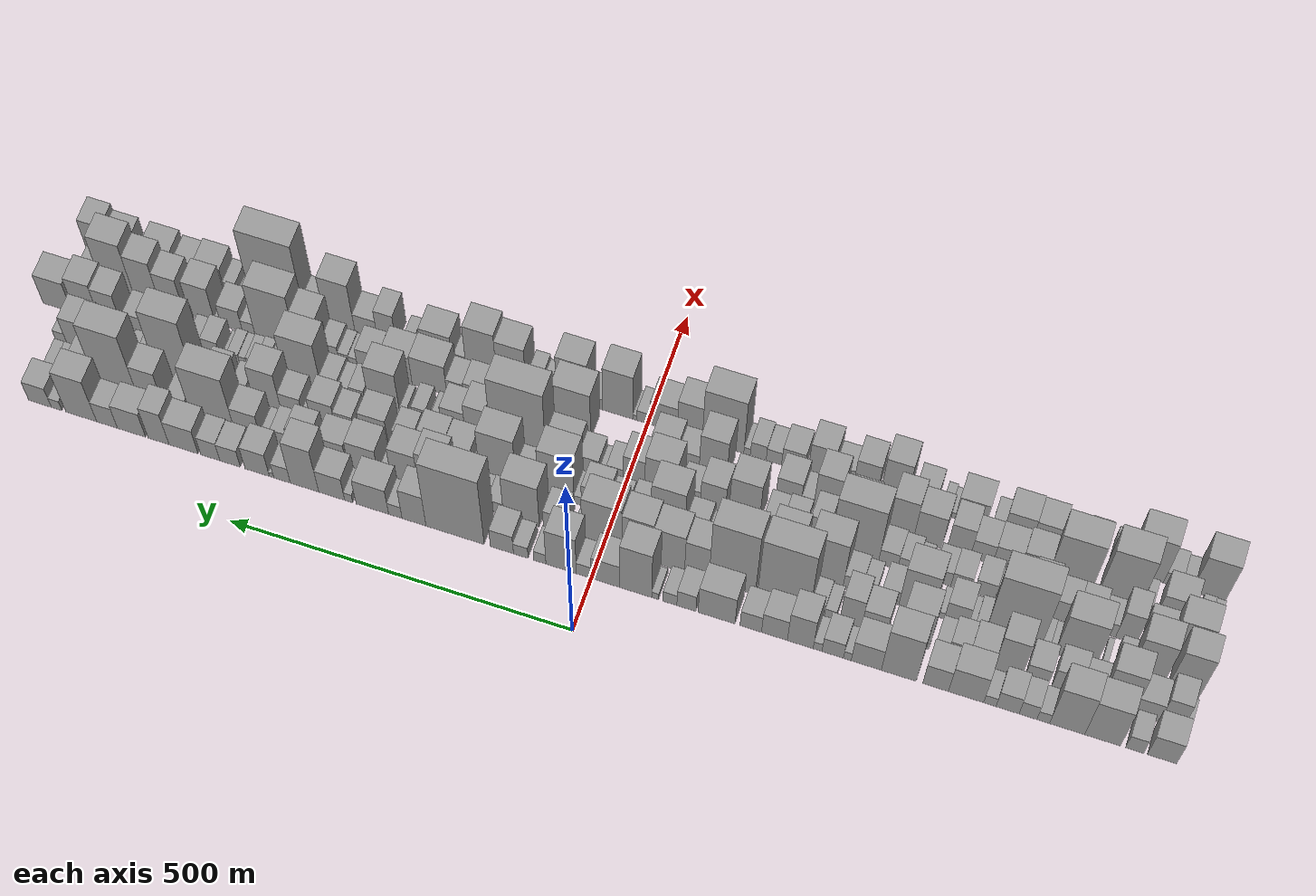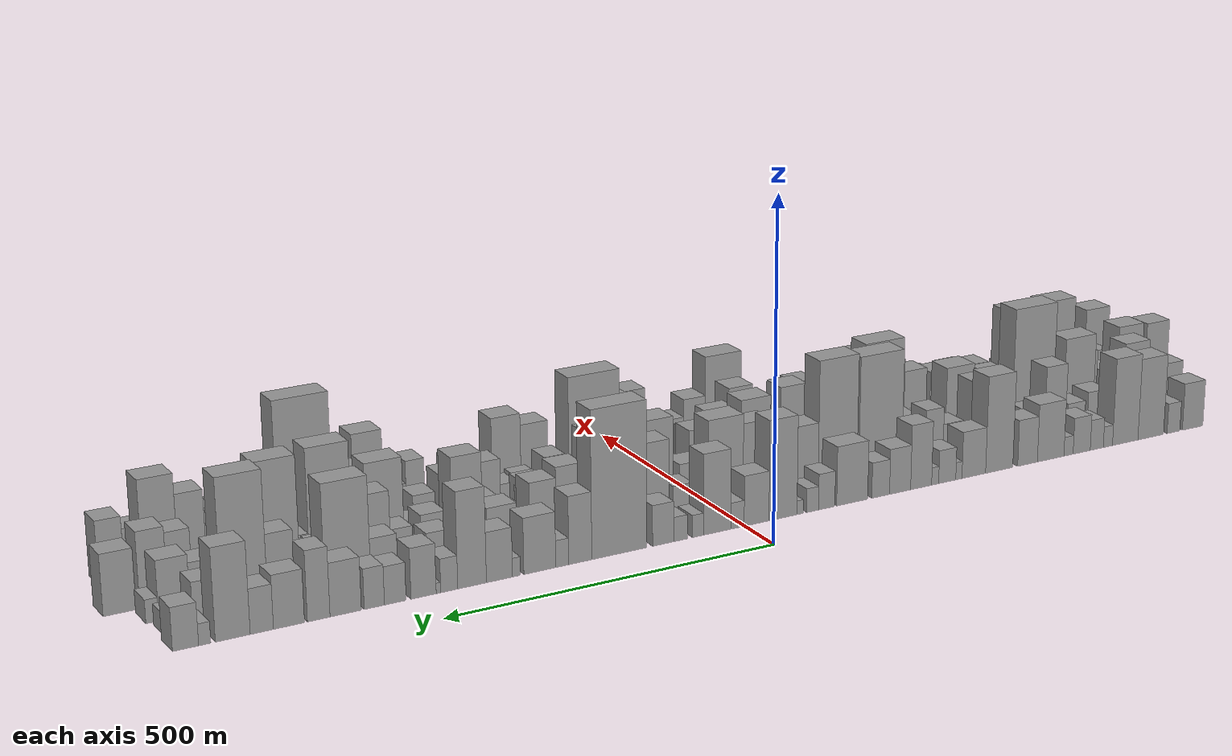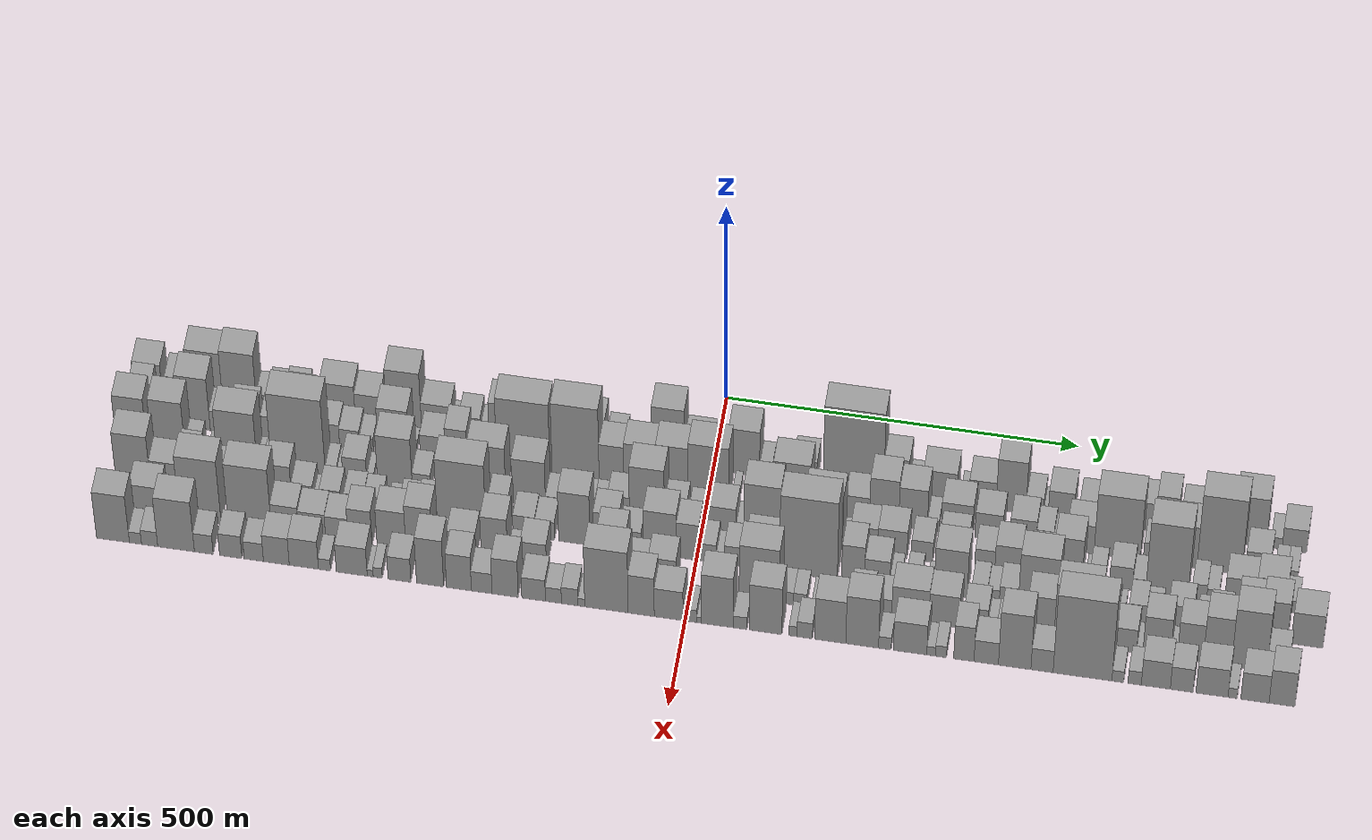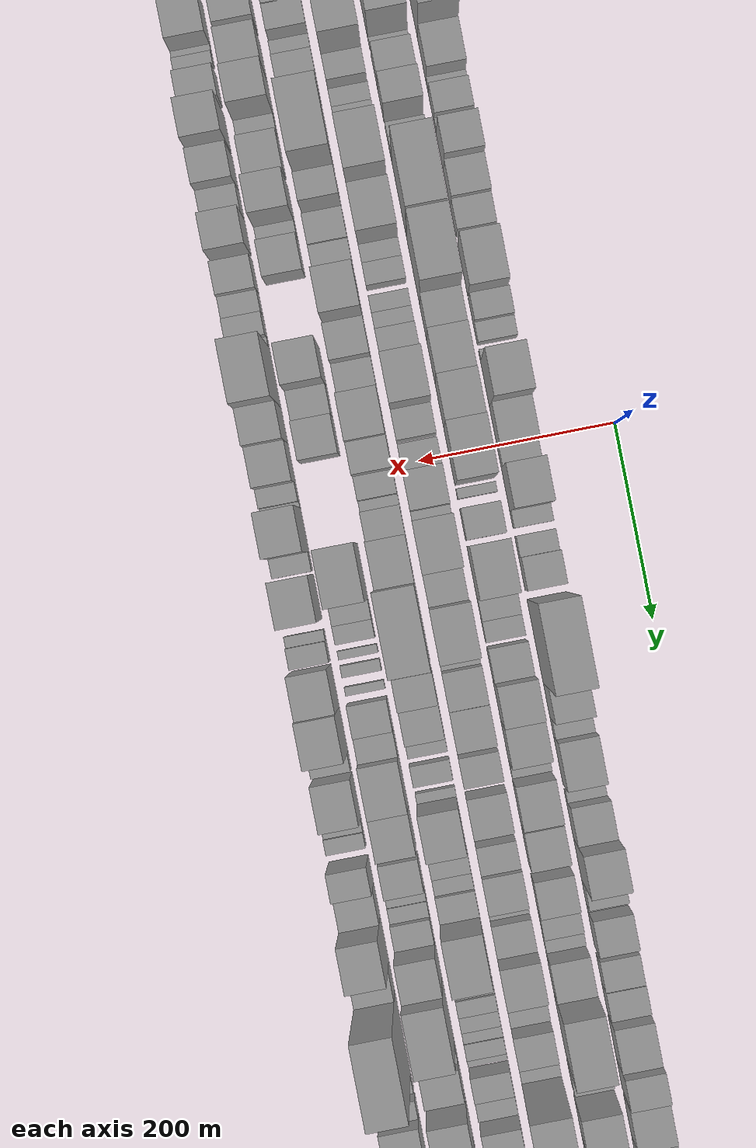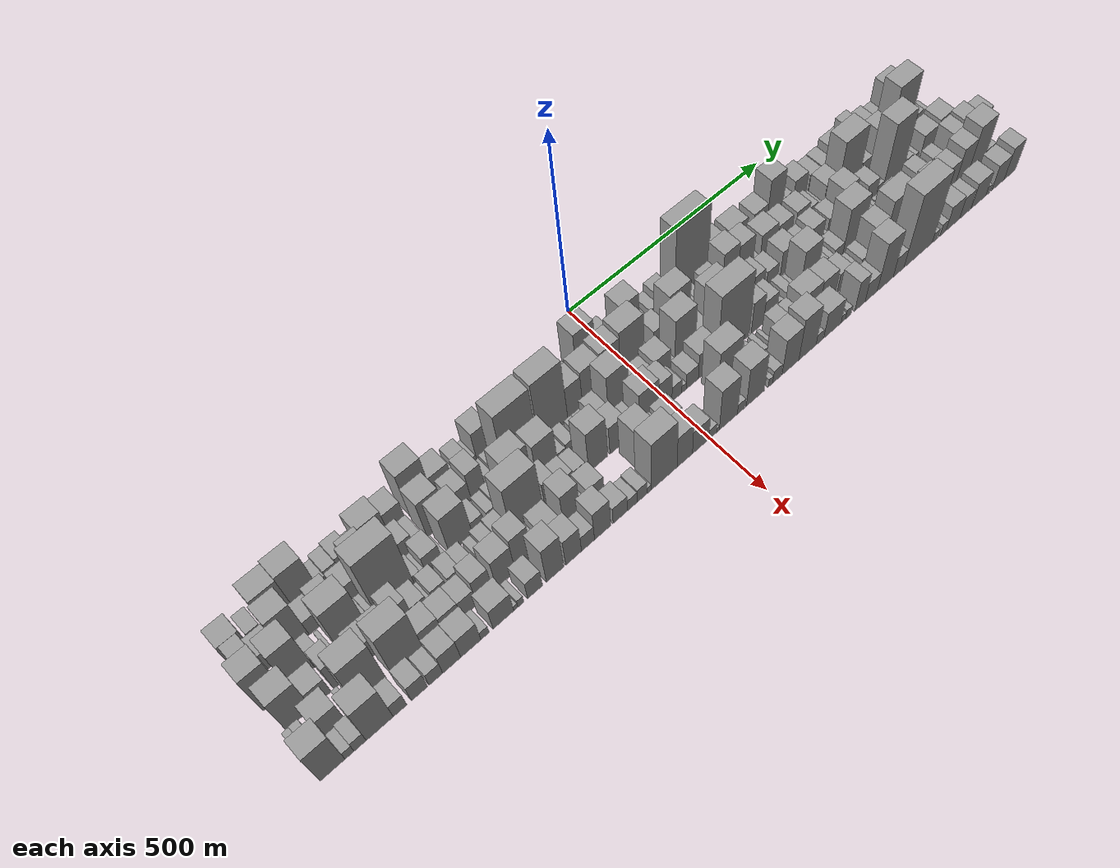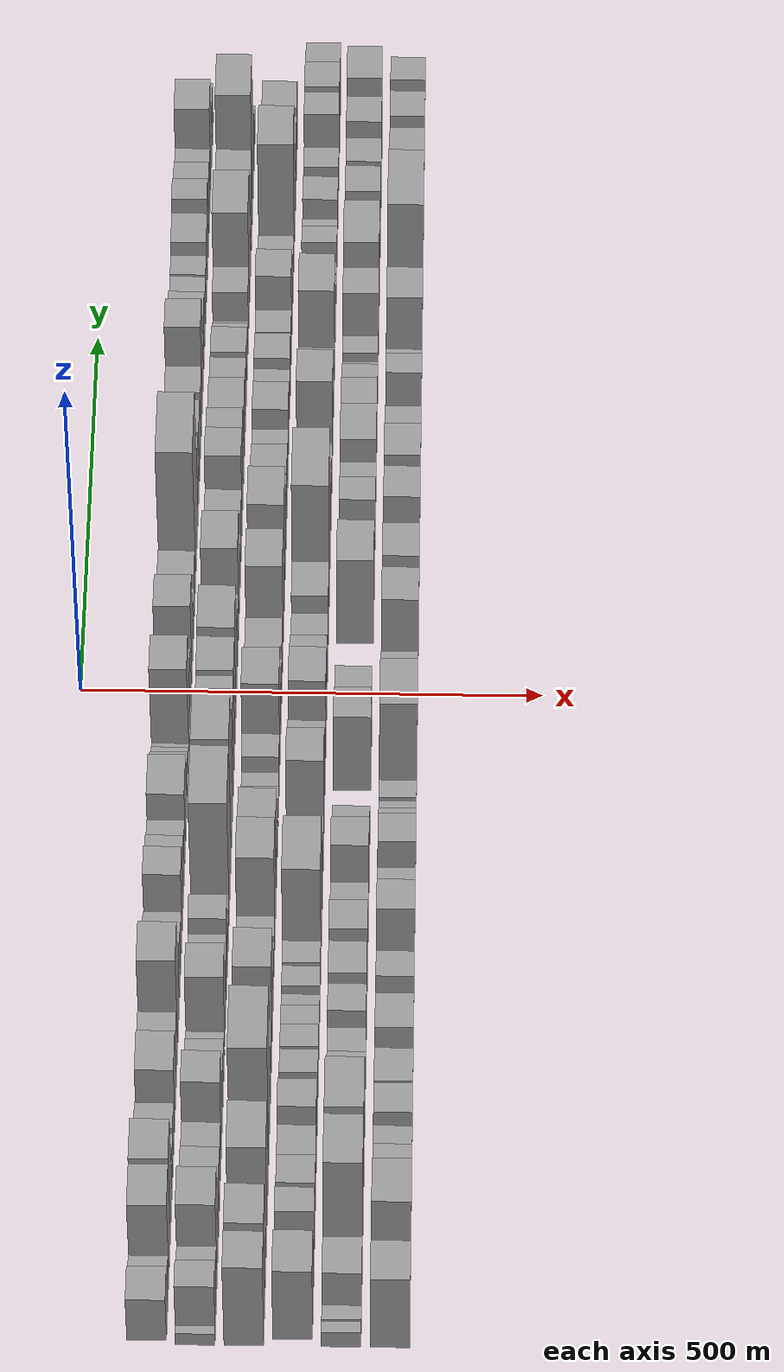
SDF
<sdf version="1.6">
 <world name="default">
  <scene>
   <sky><clouds><speed>12</speed></clouds></sky>
   <ambient>0.4 0.4 0.4 1</ambient>
   <background>0.7 0.7 0.7 1</background>
   <shadows>1</shadows>
  </scene>
  <gravity>0 0 -9.8066</gravity>
  <magnetic_field>6e-06 2.3e-05 -4.2e-05</magnetic_field>
  <physics default="0" name="default_physics" type="ode">
   <ode>
    <solver>
     <type>quick</type>
     <iters>10</iters>
     <sor>1.0</sor>
     <use_dynamic_moi_rescaling>0</use_dynamic_moi_rescaling>
    </solver>
    <constraints>
     <cfm>0</cfm>
     <erp>0.2</erp>
     <contact_max_correcting_vel>100</contact_max_correcting_vel>
     <contact_surface_layer>0.001</contact_surface_layer>
    </constraints>
   </ode>
   <max_step_size>0.004</max_step_size>
   <real_time_factor>1</real_time_factor>
   <real_time_update_rate>250</real_time_update_rate>
  </physics>
  <light name="sun" type="directional">
   <pose>0 0 10 0 0 0</pose>
   <diffuse>0.8 0.8 0.8 1</diffuse>
   <specular>0.2 0.2 0.2 1</specular>
   <attenuation>
    <range>1000</range>
    <constant>0.9</constant>
    <linear>0.01</linear>
    <quadratic>0.001</quadratic>
   </attenuation>
   <direction>-0.5 0.1 -0.9</direction>
  </light>
  <model name="building_1">
   <static>1</static>
   <pose>100.0000 -804.8391 0 0.000000 0.000000 0.000000</pose>
   <link name="link">
    <pose>0 0 37.50 0 0 0</pose>
    <collision name="collision"><geometry><box><size>40.0000 40.3217 75.0000</size></box></geometry></collision>
    <visual name="visual">
     <cast_shadows>0</cast_shadows>
     <geometry><box><size>40.0000 40.3217 75.0000</size></box></geometry>
     <material>
      <script>
       <uri>model://grey_wall/materials/scripts</uri>
       <uri>model://grey_wall/materials/textures</uri>
       <name>vrc/grey_wall</name>
      </script>
     </material>
    </visual>
   </link>
  </model>
  <model name="building_2">
   <static>1</static>
   <pose>100.0000 -767.2053 0 0.000000 0.000000 0.000000</pose>
   <link name="link">
    <pose>0 0 24.00 0 0 0</pose>
    <collision name="collision"><geometry><box><size>40.0000 24.9459 48.0000</size></box></geometry></collision>
    <visual name="visual">
     <cast_shadows>0</cast_shadows>
     <geometry><box><size>40.0000 24.9459 48.0000</size></box></geometry>
     <material>
      <script>
       <uri>model://grey_wall/materials/scripts</uri>
       <uri>model://grey_wall/materials/textures</uri>
       <name>vrc/grey_wall</name>
      </script>
     </material>
    </visual>
   </link>
  </model>
  <model name="building_3">
   <static>1</static>
   <pose>100.0000 -722.9092 0 0.000000 0.000000 0.000000</pose>
   <link name="link">
    <pose>0 0 64.50 0 0 0</pose>
    <collision name="collision"><geometry><box><size>40.0000 49.6463 129.0000</size></box></geometry></collision>
    <visual name="visual">
     <cast_shadows>0</cast_shadows>
     <geometry><box><size>40.0000 49.6463 129.0000</size></box></geometry>
     <material>
      <script>
       <uri>model://grey_wall/materials/scripts</uri>
       <uri>model://grey_wall/materials/textures</uri>
       <name>vrc/grey_wall</name>
      </script>
     </material>
    </visual>
   </link>
  </model>
  <model name="building_4">
   <static>1</static>
   <pose>100.0000 -673.7390 0 0.000000 0.000000 0.000000</pose>
   <link name="link">
    <pose>0 0 69.00 0 0 0</pose>
    <collision name="collision"><geometry><box><size>40.0000 48.6941 138.0000</size></box></geometry></collision>
    <visual name="visual">
     <cast_shadows>0</cast_shadows>
     <geometry><box><size>40.0000 48.6941 138.0000</size></box></geometry>
     <material>
      <script>
       <uri>model://grey_wall/materials/scripts</uri>
       <uri>model://grey_wall/materials/textures</uri>
       <name>vrc/grey_wall</name>
      </script>
     </material>
    </visual>
   </link>
  </model>
  <model name="building_5">
   <static>1</static>
   <pose>100.0000 -640.6118 0 0.000000 0.000000 0.000000</pose>
   <link name="link">
    <pose>0 0 16.50 0 0 0</pose>
    <collision name="collision"><geometry><box><size>40.0000 17.5602 33.0000</size></box></geometry></collision>
    <visual name="visual">
     <cast_shadows>0</cast_shadows>
     <geometry><box><size>40.0000 17.5602 33.0000</size></box></geometry>
     <material>
      <script>
       <uri>model://grey_wall/materials/scripts</uri>
       <uri>model://grey_wall/materials/textures</uri>
       <name>vrc/grey_wall</name>
      </script>
     </material>
    </visual>
   </link>
  </model>
  <model name="building_6">
   <static>1</static>
   <pose>100.0000 -619.4572 0 0.000000 0.000000 0.000000</pose>
   <link name="link">
    <pose>0 0 24.00 0 0 0</pose>
    <collision name="collision"><geometry><box><size>40.0000 24.7491 48.0000</size></box></geometry></collision>
    <visual name="visual">
     <cast_shadows>0</cast_shadows>
     <geometry><box><size>40.0000 24.7491 48.0000</size></box></geometry>
     <material>
      <script>
       <uri>model://grey_wall/materials/scripts</uri>
       <uri>model://grey_wall/materials/textures</uri>
       <name>vrc/grey_wall</name>
      </script>
     </material>
    </visual>
   </link>
  </model>
  <model name="building_7">
   <static>1</static>
   <pose>100.0000 -591.0079 0 0.000000 0.000000 0.000000</pose>
   <link name="link">
    <pose>0 0 28.50 0 0 0</pose>
    <collision name="collision"><geometry><box><size>40.0000 32.1493 57.0000</size></box></geometry></collision>
    <visual name="visual">
     <cast_shadows>0</cast_shadows>
     <geometry><box><size>40.0000 32.1493 57.0000</size></box></geometry>
     <material>
      <script>
       <uri>model://grey_wall/materials/scripts</uri>
       <uri>model://grey_wall/materials/textures</uri>
       <name>vrc/grey_wall</name>
      </script>
     </material>
    </visual>
   </link>
  </model>
  <model name="building_8">
   <static>1</static>
   <pose>100.0000 -566.2766 0 0.000000 0.000000 0.000000</pose>
   <link name="link">
    <pose>0 0 15.00 0 0 0</pose>
    <collision name="collision"><geometry><box><size>40.0000 17.3134 30.0000</size></box></geometry></collision>
    <visual name="visual">
     <cast_shadows>0</cast_shadows>
     <geometry><box><size>40.0000 17.3134 30.0000</size></box></geometry>
     <material>
      <script>
       <uri>model://grey_wall/materials/scripts</uri>
       <uri>model://grey_wall/materials/textures</uri>
       <name>vrc/grey_wall</name>
      </script>
     </material>
    </visual>
   </link>
  </model>
  <model name="building_9">
   <static>1</static>
   <pose>100.0000 -533.0043 0 0.000000 0.000000 0.000000</pose>
   <link name="link">
    <pose>0 0 45.00 0 0 0</pose>
    <collision name="collision"><geometry><box><size>40.0000 49.2311 90.0000</size></box></geometry></collision>
    <visual name="visual">
     <cast_shadows>0</cast_shadows>
     <geometry><box><size>40.0000 49.2311 90.0000</size></box></geometry>
     <material>
      <script>
       <uri>model://grey_wall/materials/scripts</uri>
       <uri>model://grey_wall/materials/textures</uri>
       <name>vrc/grey_wall</name>
      </script>
     </material>
    </visual>
   </link>
  </model>
  <model name="building_10">
   <static>1</static>
   <pose>100.0000 -490.3262 0 0.000000 0.000000 0.000000</pose>
   <link name="link">
    <pose>0 0 36.00 0 0 0</pose>
    <collision name="collision"><geometry><box><size>40.0000 36.1251 72.0000</size></box></geometry></collision>
    <visual name="visual">
     <cast_shadows>0</cast_shadows>
     <geometry><box><size>40.0000 36.1251 72.0000</size></box></geometry>
     <material>
      <script>
       <uri>model://grey_wall/materials/scripts</uri>
       <uri>model://grey_wall/materials/textures</uri>
       <name>vrc/grey_wall</name>
      </script>
     </material>
    </visual>
   </link>
  </model>
  <model name="building_11">
   <static>1</static>
   <pose>100.0000 -438.5817 0 0.000000 0.000000 0.000000</pose>
   <link name="link">
    <pose>0 0 75.00 0 0 0</pose>
    <collision name="collision"><geometry><box><size>40.0000 49.3639 150.0000</size></box></geometry></collision>
    <visual name="visual">
     <cast_shadows>0</cast_shadows>
     <geometry><box><size>40.0000 49.3639 150.0000</size></box></geometry>
     <material>
      <script>
       <uri>model://grey_wall/materials/scripts</uri>
       <uri>model://grey_wall/materials/textures</uri>
       <name>vrc/grey_wall</name>
      </script>
     </material>
    </visual>
   </link>
  </model>
  <model name="building_12">
   <static>1</static>
   <pose>100.0000 -392.6815 0 0.000000 0.000000 0.000000</pose>
   <link name="link">
    <pose>0 0 36.00 0 0 0</pose>
    <collision name="collision"><geometry><box><size>40.0000 42.4365 72.0000</size></box></geometry></collision>
    <visual name="visual">
     <cast_shadows>0</cast_shadows>
     <geometry><box><size>40.0000 42.4365 72.0000</size></box></geometry>
     <material>
      <script>
       <uri>model://grey_wall/materials/scripts</uri>
       <uri>model://grey_wall/materials/textures</uri>
       <name>vrc/grey_wall</name>
      </script>
     </material>
    </visual>
   </link>
  </model>
  <model name="building_13">
   <static>1</static>
   <pose>100.0000 -365.9398 0 0.000000 0.000000 0.000000</pose>
   <link name="link">
    <pose>0 0 13.50 0 0 0</pose>
    <collision name="collision"><geometry><box><size>40.0000 11.0469 27.0000</size></box></geometry></collision>
    <visual name="visual">
     <cast_shadows>0</cast_shadows>
     <geometry><box><size>40.0000 11.0469 27.0000</size></box></geometry>
     <material>
      <script>
       <uri>model://grey_wall/materials/scripts</uri>
       <uri>model://grey_wall/materials/textures</uri>
       <name>vrc/grey_wall</name>
      </script>
     </material>
    </visual>
   </link>
  </model>
  <model name="building_14">
   <static>1</static>
   <pose>100.0000 -345.2138 0 0.000000 0.000000 0.000000</pose>
   <link name="link">
    <pose>0 0 25.50 0 0 0</pose>
    <collision name="collision"><geometry><box><size>40.0000 30.4052 51.0000</size></box></geometry></collision>
    <visual name="visual">
     <cast_shadows>0</cast_shadows>
     <geometry><box><size>40.0000 30.4052 51.0000</size></box></geometry>
     <material>
      <script>
       <uri>model://grey_wall/materials/scripts</uri>
       <uri>model://grey_wall/materials/textures</uri>
       <name>vrc/grey_wall</name>
      </script>
     </material>
    </visual>
   </link>
  </model>
  <model name="building_15">
   <static>1</static>
   <pose>100.0000 -323.7918 0 0.000000 0.000000 0.000000</pose>
   <link name="link">
    <pose>0 0 13.50 0 0 0</pose>
    <collision name="collision"><geometry><box><size>40.0000 12.4387 27.0000</size></box></geometry></collision>
    <visual name="visual">
     <cast_shadows>0</cast_shadows>
     <geometry><box><size>40.0000 12.4387 27.0000</size></box></geometry>
     <material>
      <script>
       <uri>model://grey_wall/materials/scripts</uri>
       <uri>model://grey_wall/materials/textures</uri>
       <name>vrc/grey_wall</name>
      </script>
     </material>
    </visual>
   </link>
  </model>
  <model name="building_16">
   <static>1</static>
   <pose>100.0000 -299.1559 0 0.000000 0.000000 0.000000</pose>
   <link name="link">
    <pose>0 0 49.50 0 0 0</pose>
    <collision name="collision"><geometry><box><size>40.0000 36.8331 99.0000</size></box></geometry></collision>
    <visual name="visual">
     <cast_shadows>0</cast_shadows>
     <geometry><box><size>40.0000 36.8331 99.0000</size></box></geometry>
     <material>
      <script>
       <uri>model://grey_wall/materials/scripts</uri>
       <uri>model://grey_wall/materials/textures</uri>
       <name>vrc/grey_wall</name>
      </script>
     </material>
    </visual>
   </link>
  </model>
  <model name="building_17">
   <static>1</static>
   <pose>100.0000 -262.3806 0 0.000000 0.000000 0.000000</pose>
   <link name="link">
    <pose>0 0 34.50 0 0 0</pose>
    <collision name="collision"><geometry><box><size>40.0000 36.7175 69.0000</size></box></geometry></collision>
    <visual name="visual">
     <cast_shadows>0</cast_shadows>
     <geometry><box><size>40.0000 36.7175 69.0000</size></box></geometry>
     <material>
      <script>
       <uri>model://grey_wall/materials/scripts</uri>
       <uri>model://grey_wall/materials/textures</uri>
       <name>vrc/grey_wall</name>
      </script>
     </material>
    </visual>
   </link>
  </model>
  <model name="building_18">
   <static>1</static>
   <pose>100.0000 -228.6835 0 0.000000 0.000000 0.000000</pose>
   <link name="link">
    <pose>0 0 27.00 0 0 0</pose>
    <collision name="collision"><geometry><box><size>40.0000 30.6767 54.0000</size></box></geometry></collision>
    <visual name="visual">
     <cast_shadows>0</cast_shadows>
     <geometry><box><size>40.0000 30.6767 54.0000</size></box></geometry>
     <material>
      <script>
       <uri>model://grey_wall/materials/scripts</uri>
       <uri>model://grey_wall/materials/textures</uri>
       <name>vrc/grey_wall</name>
      </script>
     </material>
    </visual>
   </link>
  </model>
  <model name="building_19">
   <static>1</static>
   <pose>100.0000 -179.8396 0 0.000000 0.000000 0.000000</pose>
   <link name="link">
    <pose>0 0 45.00 0 0 0</pose>
    <collision name="collision"><geometry><box><size>40.0000 53.0111 90.0000</size></box></geometry></collision>
    <visual name="visual">
     <cast_shadows>0</cast_shadows>
     <geometry><box><size>40.0000 53.0111 90.0000</size></box></geometry>
     <material>
      <script>
       <uri>model://grey_wall/materials/scripts</uri>
       <uri>model://grey_wall/materials/textures</uri>
       <name>vrc/grey_wall</name>
      </script>
     </material>
    </visual>
   </link>
  </model>
  <model name="building_20">
   <static>1</static>
   <pose>100.0000 -136.5912 0 0.000000 0.000000 0.000000</pose>
   <link name="link">
    <pose>0 0 27.00 0 0 0</pose>
    <collision name="collision"><geometry><box><size>40.0000 27.4857 54.0000</size></box></geometry></collision>
    <visual name="visual">
     <cast_shadows>0</cast_shadows>
     <geometry><box><size>40.0000 27.4857 54.0000</size></box></geometry>
     <material>
      <script>
       <uri>model://grey_wall/materials/scripts</uri>
       <uri>model://grey_wall/materials/textures</uri>
       <name>vrc/grey_wall</name>
      </script>
     </material>
    </visual>
   </link>
  </model>
  <model name="building_21">
   <static>1</static>
   <pose>100.0000 -112.8371 0 0.000000 0.000000 0.000000</pose>
   <link name="link">
    <pose>0 0 18.00 0 0 0</pose>
    <collision name="collision"><geometry><box><size>40.0000 20.0225 36.0000</size></box></geometry></collision>
    <visual name="visual">
     <cast_shadows>0</cast_shadows>
     <geometry><box><size>40.0000 20.0225 36.0000</size></box></geometry>
     <material>
      <script>
       <uri>model://grey_wall/materials/scripts</uri>
       <uri>model://grey_wall/materials/textures</uri>
       <name>vrc/grey_wall</name>
      </script>
     </material>
    </visual>
   </link>
  </model>
  <model name="building_22">
   <static>1</static>
   <pose>100.0000 -91.7197 0 0.000000 0.000000 0.000000</pose>
   <link name="link">
    <pose>0 0 10.50 0 0 0</pose>
    <collision name="collision"><geometry><box><size>40.0000 10.2122 21.0000</size></box></geometry></collision>
    <visual name="visual">
     <cast_shadows>0</cast_shadows>
     <geometry><box><size>40.0000 10.2122 21.0000</size></box></geometry>
     <material>
      <script>
       <uri>model://grey_wall/materials/scripts</uri>
       <uri>model://grey_wall/materials/textures</uri>
       <name>vrc/grey_wall</name>
      </script>
     </material>
    </visual>
   </link>
  </model>
  <model name="building_23">
   <static>1</static>
   <pose>100.0000 -63.3768 0 0.000000 0.000000 0.000000</pose>
   <link name="link">
    <pose>0 0 75.00 0 0 0</pose>
    <collision name="collision"><geometry><box><size>40.0000 46.4738 150.0000</size></box></geometry></collision>
    <visual name="visual">
     <cast_shadows>0</cast_shadows>
     <geometry><box><size>40.0000 46.4738 150.0000</size></box></geometry>
     <material>
      <script>
       <uri>model://grey_wall/materials/scripts</uri>
       <uri>model://grey_wall/materials/textures</uri>
       <name>vrc/grey_wall</name>
      </script>
     </material>
    </visual>
   </link>
  </model>
  <model name="building_24">
   <static>1</static>
   <pose>100.0000 -19.8000 0 0.000000 0.000000 0.000000</pose>
   <link name="link">
    <pose>0 0 37.50 0 0 0</pose>
    <collision name="collision"><geometry><box><size>40.0000 40.6798 75.0000</size></box></geometry></collision>
    <visual name="visual">
     <cast_shadows>0</cast_shadows>
     <geometry><box><size>40.0000 40.6798 75.0000</size></box></geometry>
     <material>
      <script>
       <uri>model://grey_wall/materials/scripts</uri>
       <uri>model://grey_wall/materials/textures</uri>
       <name>vrc/grey_wall</name>
      </script>
     </material>
    </visual>
   </link>
  </model>
  <model name="building_25">
   <static>1</static>
   <pose>100.0000 11.3328 0 0.000000 0.000000 0.000000</pose>
   <link name="link">
    <pose>0 0 19.50 0 0 0</pose>
    <collision name="collision"><geometry><box><size>40.0000 21.5857 39.0000</size></box></geometry></collision>
    <visual name="visual">
     <cast_shadows>0</cast_shadows>
     <geometry><box><size>40.0000 21.5857 39.0000</size></box></geometry>
     <material>
      <script>
       <uri>model://grey_wall/materials/scripts</uri>
       <uri>model://grey_wall/materials/textures</uri>
       <name>vrc/grey_wall</name>
      </script>
     </material>
    </visual>
   </link>
  </model>
  <model name="building_26">
   <static>1</static>
   <pose>100.0000 44.2382 0 0.000000 0.000000 0.000000</pose>
   <link name="link">
    <pose>0 0 60.00 0 0 0</pose>
    <collision name="collision"><geometry><box><size>40.0000 44.2251 120.0000</size></box></geometry></collision>
    <visual name="visual">
     <cast_shadows>0</cast_shadows>
     <geometry><box><size>40.0000 44.2251 120.0000</size></box></geometry>
     <material>
      <script>
       <uri>model://grey_wall/materials/scripts</uri>
       <uri>model://grey_wall/materials/textures</uri>
       <name>vrc/grey_wall</name>
      </script>
     </material>
    </visual>
   </link>
  </model>
  <model name="building_27">
   <static>1</static>
   <pose>100.0000 75.2839 0 0.000000 0.000000 0.000000</pose>
   <link name="link">
    <pose>0 0 16.50 0 0 0</pose>
    <collision name="collision"><geometry><box><size>40.0000 17.8664 33.0000</size></box></geometry></collision>
    <visual name="visual">
     <cast_shadows>0</cast_shadows>
     <geometry><box><size>40.0000 17.8664 33.0000</size></box></geometry>
     <material>
      <script>
       <uri>model://grey_wall/materials/scripts</uri>
       <uri>model://grey_wall/materials/textures</uri>
       <name>vrc/grey_wall</name>
      </script>
     </material>
    </visual>
   </link>
  </model>
  <model name="building_28">
   <static>1</static>
   <pose>100.0000 102.9447 0 0.000000 0.000000 0.000000</pose>
   <link name="link">
    <pose>0 0 18.00 0 0 0</pose>
    <collision name="collision"><geometry><box><size>40.0000 21.4551 36.0000</size></box></geometry></collision>
    <visual name="visual">
     <cast_shadows>0</cast_shadows>
     <geometry><box><size>40.0000 21.4551 36.0000</size></box></geometry>
     <material>
      <script>
       <uri>model://grey_wall/materials/scripts</uri>
       <uri>model://grey_wall/materials/textures</uri>
       <name>vrc/grey_wall</name>
      </script>
     </material>
    </visual>
   </link>
  </model>
  <model name="building_29">
   <static>1</static>
   <pose>100.0000 130.4869 0 0.000000 0.000000 0.000000</pose>
   <link name="link">
    <pose>0 0 30.00 0 0 0</pose>
    <collision name="collision"><geometry><box><size>40.0000 33.6293 60.0000</size></box></geometry></collision>
    <visual name="visual">
     <cast_shadows>0</cast_shadows>
     <geometry><box><size>40.0000 33.6293 60.0000</size></box></geometry>
     <material>
      <script>
       <uri>model://grey_wall/materials/scripts</uri>
       <uri>model://grey_wall/materials/textures</uri>
       <name>vrc/grey_wall</name>
      </script>
     </material>
    </visual>
   </link>
  </model>
  <model name="building_30">
   <static>1</static>
   <pose>100.0000 199.0506 0 0.000000 0.000000 0.000000</pose>
   <link name="link">
    <pose>0 0 108.00 0 0 0</pose>
    <collision name="collision"><geometry><box><size>40.0000 85.4979 216.0000</size></box></geometry></collision>
    <visual name="visual">
     <cast_shadows>0</cast_shadows>
     <geometry><box><size>40.0000 85.4979 216.0000</size></box></geometry>
     <material>
      <script>
       <uri>model://grey_wall/materials/scripts</uri>
       <uri>model://grey_wall/materials/textures</uri>
       <name>vrc/grey_wall</name>
      </script>
     </material>
    </visual>
   </link>
  </model>
  <model name="building_31">
   <static>1</static>
   <pose>100.0000 259.4269 0 0.000000 0.000000 0.000000</pose>
   <link name="link">
    <pose>0 0 49.50 0 0 0</pose>
    <collision name="collision"><geometry><box><size>40.0000 35.2547 99.0000</size></box></geometry></collision>
    <visual name="visual">
     <cast_shadows>0</cast_shadows>
     <geometry><box><size>40.0000 35.2547 99.0000</size></box></geometry>
     <material>
      <script>
       <uri>model://grey_wall/materials/scripts</uri>
       <uri>model://grey_wall/materials/textures</uri>
       <name>vrc/grey_wall</name>
      </script>
     </material>
    </visual>
   </link>
  </model>
  <model name="building_32">
   <static>1</static>
   <pose>100.0000 286.9620 0 0.000000 0.000000 0.000000</pose>
   <link name="link">
    <pose>0 0 19.50 0 0 0</pose>
    <collision name="collision"><geometry><box><size>40.0000 19.8156 39.0000</size></box></geometry></collision>
    <visual name="visual">
     <cast_shadows>0</cast_shadows>
     <geometry><box><size>40.0000 19.8156 39.0000</size></box></geometry>
     <material>
      <script>
       <uri>model://grey_wall/materials/scripts</uri>
       <uri>model://grey_wall/materials/textures</uri>
       <name>vrc/grey_wall</name>
      </script>
     </material>
    </visual>
   </link>
  </model>
  <model name="building_33">
   <static>1</static>
   <pose>100.0000 320.8729 0 0.000000 0.000000 0.000000</pose>
   <link name="link">
    <pose>0 0 40.50 0 0 0</pose>
    <collision name="collision"><geometry><box><size>40.0000 48.0063 81.0000</size></box></geometry></collision>
    <visual name="visual">
     <cast_shadows>0</cast_shadows>
     <geometry><box><size>40.0000 48.0063 81.0000</size></box></geometry>
     <material>
      <script>
       <uri>model://grey_wall/materials/scripts</uri>
       <uri>model://grey_wall/materials/textures</uri>
       <name>vrc/grey_wall</name>
      </script>
     </material>
    </visual>
   </link>
  </model>
  <model name="building_34">
   <static>1</static>
   <pose>100.0000 355.8433 0 0.000000 0.000000 0.000000</pose>
   <link name="link">
    <pose>0 0 13.50 0 0 0</pose>
    <collision name="collision"><geometry><box><size>40.0000 11.9346 27.0000</size></box></geometry></collision>
    <visual name="visual">
     <cast_shadows>0</cast_shadows>
     <geometry><box><size>40.0000 11.9346 27.0000</size></box></geometry>
     <material>
      <script>
       <uri>model://grey_wall/materials/scripts</uri>
       <uri>model://grey_wall/materials/textures</uri>
       <name>vrc/grey_wall</name>
      </script>
     </material>
    </visual>
   </link>
  </model>
  <model name="building_35">
   <static>1</static>
   <pose>100.0000 381.1490 0 0.000000 0.000000 0.000000</pose>
   <link name="link">
    <pose>0 0 36.00 0 0 0</pose>
    <collision name="collision"><geometry><box><size>40.0000 38.6768 72.0000</size></box></geometry></collision>
    <visual name="visual">
     <cast_shadows>0</cast_shadows>
     <geometry><box><size>40.0000 38.6768 72.0000</size></box></geometry>
     <material>
      <script>
       <uri>model://grey_wall/materials/scripts</uri>
       <uri>model://grey_wall/materials/textures</uri>
       <name>vrc/grey_wall</name>
      </script>
     </material>
    </visual>
   </link>
  </model>
  <model name="building_36">
   <static>1</static>
   <pose>100.0000 421.5169 0 0.000000 0.000000 0.000000</pose>
   <link name="link">
    <pose>0 0 69.00 0 0 0</pose>
    <collision name="collision"><geometry><box><size>40.0000 42.0590 138.0000</size></box></geometry></collision>
    <visual name="visual">
     <cast_shadows>0</cast_shadows>
     <geometry><box><size>40.0000 42.0590 138.0000</size></box></geometry>
     <material>
      <script>
       <uri>model://grey_wall/materials/scripts</uri>
       <uri>model://grey_wall/materials/textures</uri>
       <name>vrc/grey_wall</name>
      </script>
     </material>
    </visual>
   </link>
  </model>
  <model name="building_37">
   <static>1</static>
   <pose>100.0000 454.9248 0 0.000000 0.000000 0.000000</pose>
   <link name="link">
    <pose>0 0 24.00 0 0 0</pose>
    <collision name="collision"><geometry><box><size>40.0000 24.7566 48.0000</size></box></geometry></collision>
    <visual name="visual">
     <cast_shadows>0</cast_shadows>
     <geometry><box><size>40.0000 24.7566 48.0000</size></box></geometry>
     <material>
      <script>
       <uri>model://grey_wall/materials/scripts</uri>
       <uri>model://grey_wall/materials/textures</uri>
       <name>vrc/grey_wall</name>
      </script>
     </material>
    </visual>
   </link>
  </model>
  <model name="building_38">
   <static>1</static>
   <pose>100.0000 470.5981 0 0.000000 0.000000 0.000000</pose>
   <link name="link">
    <pose>0 0 7.50 0 0 0</pose>
    <collision name="collision"><geometry><box><size>40.0000 6.5901 15.0000</size></box></geometry></collision>
    <visual name="visual">
     <cast_shadows>0</cast_shadows>
     <geometry><box><size>40.0000 6.5901 15.0000</size></box></geometry>
     <material>
      <script>
       <uri>model://grey_wall/materials/scripts</uri>
       <uri>model://grey_wall/materials/textures</uri>
       <name>vrc/grey_wall</name>
      </script>
     </material>
    </visual>
   </link>
  </model>
  <model name="building_39">
   <static>1</static>
   <pose>100.0000 492.0615 0 0.000000 0.000000 0.000000</pose>
   <link name="link">
    <pose>0 0 36.00 0 0 0</pose>
    <collision name="collision"><geometry><box><size>40.0000 36.3368 72.0000</size></box></geometry></collision>
    <visual name="visual">
     <cast_shadows>0</cast_shadows>
     <geometry><box><size>40.0000 36.3368 72.0000</size></box></geometry>
     <material>
      <script>
       <uri>model://grey_wall/materials/scripts</uri>
       <uri>model://grey_wall/materials/textures</uri>
       <name>vrc/grey_wall</name>
      </script>
     </material>
    </visual>
   </link>
  </model>
  <model name="building_40">
   <static>1</static>
   <pose>100.0000 532.6207 0 0.000000 0.000000 0.000000</pose>
   <link name="link">
    <pose>0 0 27.00 0 0 0</pose>
    <collision name="collision"><geometry><box><size>40.0000 30.7815 54.0000</size></box></geometry></collision>
    <visual name="visual">
     <cast_shadows>0</cast_shadows>
     <geometry><box><size>40.0000 30.7815 54.0000</size></box></geometry>
     <material>
      <script>
       <uri>model://grey_wall/materials/scripts</uri>
       <uri>model://grey_wall/materials/textures</uri>
       <name>vrc/grey_wall</name>
      </script>
     </material>
    </visual>
   </link>
  </model>
  <model name="building_41">
   <static>1</static>
   <pose>100.0000 562.3213 0 0.000000 0.000000 0.000000</pose>
   <link name="link">
    <pose>0 0 28.50 0 0 0</pose>
    <collision name="collision"><geometry><box><size>40.0000 28.6198 57.0000</size></box></geometry></collision>
    <visual name="visual">
     <cast_shadows>0</cast_shadows>
     <geometry><box><size>40.0000 28.6198 57.0000</size></box></geometry>
     <material>
      <script>
       <uri>model://grey_wall/materials/scripts</uri>
       <uri>model://grey_wall/materials/textures</uri>
       <name>vrc/grey_wall</name>
      </script>
     </material>
    </visual>
   </link>
  </model>
  <model name="building_42">
   <static>1</static>
   <pose>100.0000 602.5294 0 0.000000 0.000000 0.000000</pose>
   <link name="link">
    <pose>0 0 37.50 0 0 0</pose>
    <collision name="collision"><geometry><box><size>40.0000 43.7964 75.0000</size></box></geometry></collision>
    <visual name="visual">
     <cast_shadows>0</cast_shadows>
     <geometry><box><size>40.0000 43.7964 75.0000</size></box></geometry>
     <material>
      <script>
       <uri>model://grey_wall/materials/scripts</uri>
       <uri>model://grey_wall/materials/textures</uri>
       <name>vrc/grey_wall</name>
      </script>
     </material>
    </visual>
   </link>
  </model>
  <model name="building_43">
   <static>1</static>
   <pose>100.0000 640.0904 0 0.000000 0.000000 0.000000</pose>
   <link name="link">
    <pose>0 0 49.50 0 0 0</pose>
    <collision name="collision"><geometry><box><size>40.0000 31.3254 99.0000</size></box></geometry></collision>
    <visual name="visual">
     <cast_shadows>0</cast_shadows>
     <geometry><box><size>40.0000 31.3254 99.0000</size></box></geometry>
     <material>
      <script>
       <uri>model://grey_wall/materials/scripts</uri>
       <uri>model://grey_wall/materials/textures</uri>
       <name>vrc/grey_wall</name>
      </script>
     </material>
    </visual>
   </link>
  </model>
  <model name="building_44">
   <static>1</static>
   <pose>100.0000 680.9795 0 0.000000 0.000000 0.000000</pose>
   <link name="link">
    <pose>0 0 37.50 0 0 0</pose>
    <collision name="collision"><geometry><box><size>40.0000 42.4528 75.0000</size></box></geometry></collision>
    <visual name="visual">
     <cast_shadows>0</cast_shadows>
     <geometry><box><size>40.0000 42.4528 75.0000</size></box></geometry>
     <material>
      <script>
       <uri>model://grey_wall/materials/scripts</uri>
       <uri>model://grey_wall/materials/textures</uri>
       <name>vrc/grey_wall</name>
      </script>
     </material>
    </visual>
   </link>
  </model>
  <model name="building_45">
   <static>1</static>
   <pose>100.0000 717.9744 0 0.000000 0.000000 0.000000</pose>
   <link name="link">
    <pose>0 0 31.50 0 0 0</pose>
    <collision name="collision"><geometry><box><size>40.0000 31.5372 63.0000</size></box></geometry></collision>
    <visual name="visual">
     <cast_shadows>0</cast_shadows>
     <geometry><box><size>40.0000 31.5372 63.0000</size></box></geometry>
     <material>
      <script>
       <uri>model://grey_wall/materials/scripts</uri>
       <uri>model://grey_wall/materials/textures</uri>
       <name>vrc/grey_wall</name>
      </script>
     </material>
    </visual>
   </link>
  </model>
  <model name="building_46">
   <static>1</static>
   <pose>100.0000 757.1625 0 0.000000 0.000000 0.000000</pose>
   <link name="link">
    <pose>0 0 64.50 0 0 0</pose>
    <collision name="collision"><geometry><box><size>40.0000 46.8390 129.0000</size></box></geometry></collision>
    <visual name="visual">
     <cast_shadows>0</cast_shadows>
     <geometry><box><size>40.0000 46.8390 129.0000</size></box></geometry>
     <material>
      <script>
       <uri>model://grey_wall/materials/scripts</uri>
       <uri>model://grey_wall/materials/textures</uri>
       <name>vrc/grey_wall</name>
      </script>
     </material>
    </visual>
   </link>
  </model>
  <model name="building_47">
   <static>1</static>
   <pose>100.0000 794.6642 0 0.000000 0.000000 0.000000</pose>
   <link name="link">
    <pose>0 0 15.00 0 0 0</pose>
    <collision name="collision"><geometry><box><size>40.0000 16.1645 30.0000</size></box></geometry></collision>
    <visual name="visual">
     <cast_shadows>0</cast_shadows>
     <geometry><box><size>40.0000 16.1645 30.0000</size></box></geometry>
     <material>
      <script>
       <uri>model://grey_wall/materials/scripts</uri>
       <uri>model://grey_wall/materials/textures</uri>
       <name>vrc/grey_wall</name>
      </script>
     </material>
    </visual>
   </link>
  </model>
  <model name="building_48">
   <static>1</static>
   <pose>100.0000 820.0291 0 0.000000 0.000000 0.000000</pose>
   <link name="link">
    <pose>0 0 30.00 0 0 0</pose>
    <collision name="collision"><geometry><box><size>40.0000 34.5654 60.0000</size></box></geometry></collision>
    <visual name="visual">
     <cast_shadows>0</cast_shadows>
     <geometry><box><size>40.0000 34.5654 60.0000</size></box></geometry>
     <material>
      <script>
       <uri>model://grey_wall/materials/scripts</uri>
       <uri>model://grey_wall/materials/textures</uri>
       <name>vrc/grey_wall</name>
      </script>
     </material>
    </visual>
   </link>
  </model>
  <model name="building_49">
   <static>1</static>
   <pose>149.0000 -825.1503 0 0.000000 0.000000 0.000000</pose>
   <link name="link">
    <pose>0 0 10.50 0 0 0</pose>
    <collision name="collision"><geometry><box><size>40.0000 9.6994 21.0000</size></box></geometry></collision>
    <visual name="visual">
     <cast_shadows>0</cast_shadows>
     <geometry><box><size>40.0000 9.6994 21.0000</size></box></geometry>
     <material>
      <script>
       <uri>model://grey_wall/materials/scripts</uri>
       <uri>model://grey_wall/materials/textures</uri>
       <name>vrc/grey_wall</name>
      </script>
     </material>
    </visual>
   </link>
  </model>
  <model name="building_50">
   <static>1</static>
   <pose>149.0000 -804.3308 0 0.000000 0.000000 0.000000</pose>
   <link name="link">
    <pose>0 0 46.50 0 0 0</pose>
    <collision name="collision"><geometry><box><size>40.0000 31.9397 93.0000</size></box></geometry></collision>
    <visual name="visual">
     <cast_shadows>0</cast_shadows>
     <geometry><box><size>40.0000 31.9397 93.0000</size></box></geometry>
     <material>
      <script>
       <uri>model://grey_wall/materials/scripts</uri>
       <uri>model://grey_wall/materials/textures</uri>
       <name>vrc/grey_wall</name>
      </script>
     </material>
    </visual>
   </link>
  </model>
  <model name="building_51">
   <static>1</static>
   <pose>149.0000 -770.3439 0 0.000000 0.000000 0.000000</pose>
   <link name="link">
    <pose>0 0 31.50 0 0 0</pose>
    <collision name="collision"><geometry><box><size>40.0000 36.0341 63.0000</size></box></geometry></collision>
    <visual name="visual">
     <cast_shadows>0</cast_shadows>
     <geometry><box><size>40.0000 36.0341 63.0000</size></box></geometry>
     <material>
      <script>
       <uri>model://grey_wall/materials/scripts</uri>
       <uri>model://grey_wall/materials/textures</uri>
       <name>vrc/grey_wall</name>
      </script>
     </material>
    </visual>
   </link>
  </model>
  <model name="building_52">
   <static>1</static>
   <pose>149.0000 -729.2863 0 0.000000 0.000000 0.000000</pose>
   <link name="link">
    <pose>0 0 69.00 0 0 0</pose>
    <collision name="collision"><geometry><box><size>40.0000 46.0811 138.0000</size></box></geometry></collision>
    <visual name="visual">
     <cast_shadows>0</cast_shadows>
     <geometry><box><size>40.0000 46.0811 138.0000</size></box></geometry>
     <material>
      <script>
       <uri>model://grey_wall/materials/scripts</uri>
       <uri>model://grey_wall/materials/textures</uri>
       <name>vrc/grey_wall</name>
      </script>
     </material>
    </visual>
   </link>
  </model>
  <model name="building_53">
   <static>1</static>
   <pose>149.0000 -691.0314 0 0.000000 0.000000 0.000000</pose>
   <link name="link">
    <pose>0 0 27.00 0 0 0</pose>
    <collision name="collision"><geometry><box><size>40.0000 30.4288 54.0000</size></box></geometry></collision>
    <visual name="visual">
     <cast_shadows>0</cast_shadows>
     <geometry><box><size>40.0000 30.4288 54.0000</size></box></geometry>
     <material>
      <script>
       <uri>model://grey_wall/materials/scripts</uri>
       <uri>model://grey_wall/materials/textures</uri>
       <name>vrc/grey_wall</name>
      </script>
     </material>
    </visual>
   </link>
  </model>
  <model name="building_54">
   <static>1</static>
   <pose>149.0000 -656.9483 0 0.000000 0.000000 0.000000</pose>
   <link name="link">
    <pose>0 0 36.00 0 0 0</pose>
    <collision name="collision"><geometry><box><size>40.0000 37.7373 72.0000</size></box></geometry></collision>
    <visual name="visual">
     <cast_shadows>0</cast_shadows>
     <geometry><box><size>40.0000 37.7373 72.0000</size></box></geometry>
     <material>
      <script>
       <uri>model://grey_wall/materials/scripts</uri>
       <uri>model://grey_wall/materials/textures</uri>
       <name>vrc/grey_wall</name>
      </script>
     </material>
    </visual>
   </link>
  </model>
  <model name="building_55">
   <static>1</static>
   <pose>149.0000 -616.6930 0 0.000000 0.000000 0.000000</pose>
   <link name="link">
    <pose>0 0 30.00 0 0 0</pose>
    <collision name="collision"><geometry><box><size>40.0000 32.7733 60.0000</size></box></geometry></collision>
    <visual name="visual">
     <cast_shadows>0</cast_shadows>
     <geometry><box><size>40.0000 32.7733 60.0000</size></box></geometry>
     <material>
      <script>
       <uri>model://grey_wall/materials/scripts</uri>
       <uri>model://grey_wall/materials/textures</uri>
       <name>vrc/grey_wall</name>
      </script>
     </material>
    </visual>
   </link>
  </model>
  <model name="building_56">
   <static>1</static>
   <pose>149.0000 -576.7092 0 0.000000 0.000000 0.000000</pose>
   <link name="link">
    <pose>0 0 63.00 0 0 0</pose>
    <collision name="collision"><geometry><box><size>40.0000 39.1944 126.0000</size></box></geometry></collision>
    <visual name="visual">
     <cast_shadows>0</cast_shadows>
     <geometry><box><size>40.0000 39.1944 126.0000</size></box></geometry>
     <material>
      <script>
       <uri>model://grey_wall/materials/scripts</uri>
       <uri>model://grey_wall/materials/textures</uri>
       <name>vrc/grey_wall</name>
      </script>
     </material>
    </visual>
   </link>
  </model>
  <model name="building_57">
   <static>1</static>
   <pose>149.0000 -539.3363 0 0.000000 0.000000 0.000000</pose>
   <link name="link">
    <pose>0 0 31.50 0 0 0</pose>
    <collision name="collision"><geometry><box><size>40.0000 35.5513 63.0000</size></box></geometry></collision>
    <visual name="visual">
     <cast_shadows>0</cast_shadows>
     <geometry><box><size>40.0000 35.5513 63.0000</size></box></geometry>
     <material>
      <script>
       <uri>model://grey_wall/materials/scripts</uri>
       <uri>model://grey_wall/materials/textures</uri>
       <name>vrc/grey_wall</name>
      </script>
     </material>
    </visual>
   </link>
  </model>
  <model name="building_58">
   <static>1</static>
   <pose>149.0000 -507.3380 0 0.000000 0.000000 0.000000</pose>
   <link name="link">
    <pose>0 0 27.00 0 0 0</pose>
    <collision name="collision"><geometry><box><size>40.0000 28.4451 54.0000</size></box></geometry></collision>
    <visual name="visual">
     <cast_shadows>0</cast_shadows>
     <geometry><box><size>40.0000 28.4451 54.0000</size></box></geometry>
     <material>
      <script>
       <uri>model://grey_wall/materials/scripts</uri>
       <uri>model://grey_wall/materials/textures</uri>
       <name>vrc/grey_wall</name>
      </script>
     </material>
    </visual>
   </link>
  </model>
  <model name="building_59">
   <static>1</static>
   <pose>149.0000 -483.3165 0 0.000000 0.000000 0.000000</pose>
   <link name="link">
    <pose>0 0 19.50 0 0 0</pose>
    <collision name="collision"><geometry><box><size>40.0000 19.5980 39.0000</size></box></geometry></collision>
    <visual name="visual">
     <cast_shadows>0</cast_shadows>
     <geometry><box><size>40.0000 19.5980 39.0000</size></box></geometry>
     <material>
      <script>
       <uri>model://grey_wall/materials/scripts</uri>
       <uri>model://grey_wall/materials/textures</uri>
       <name>vrc/grey_wall</name>
      </script>
     </material>
    </visual>
   </link>
  </model>
  <model name="building_60">
   <static>1</static>
   <pose>149.0000 -444.5563 0 0.000000 0.000000 0.000000</pose>
   <link name="link">
    <pose>0 0 63.00 0 0 0</pose>
    <collision name="collision"><geometry><box><size>40.0000 43.9225 126.0000</size></box></geometry></collision>
    <visual name="visual">
     <cast_shadows>0</cast_shadows>
     <geometry><box><size>40.0000 43.9225 126.0000</size></box></geometry>
     <material>
      <script>
       <uri>model://grey_wall/materials/scripts</uri>
       <uri>model://grey_wall/materials/textures</uri>
       <name>vrc/grey_wall</name>
      </script>
     </material>
    </visual>
   </link>
  </model>
  <model name="building_61">
   <static>1</static>
   <pose>149.0000 -418.1345 0 0.000000 0.000000 0.000000</pose>
   <link name="link">
    <pose>0 0 10.50 0 0 0</pose>
    <collision name="collision"><geometry><box><size>40.0000 8.9210 21.0000</size></box></geometry></collision>
    <visual name="visual">
     <cast_shadows>0</cast_shadows>
     <geometry><box><size>40.0000 8.9210 21.0000</size></box></geometry>
     <material>
      <script>
       <uri>model://grey_wall/materials/scripts</uri>
       <uri>model://grey_wall/materials/textures</uri>
       <name>vrc/grey_wall</name>
      </script>
     </material>
    </visual>
   </link>
  </model>
  <model name="building_62">
   <static>1</static>
   <pose>149.0000 -388.8332 0 0.000000 0.000000 0.000000</pose>
   <link name="link">
    <pose>0 0 34.50 0 0 0</pose>
    <collision name="collision"><geometry><box><size>40.0000 35.6817 69.0000</size></box></geometry></collision>
    <visual name="visual">
     <cast_shadows>0</cast_shadows>
     <geometry><box><size>40.0000 35.6817 69.0000</size></box></geometry>
     <material>
      <script>
       <uri>model://grey_wall/materials/scripts</uri>
       <uri>model://grey_wall/materials/textures</uri>
       <name>vrc/grey_wall</name>
      </script>
     </material>
    </visual>
   </link>
  </model>
  <model name="building_63">
   <static>1</static>
   <pose>149.0000 -355.4125 0 0.000000 0.000000 0.000000</pose>
   <link name="link">
    <pose>0 0 48.00 0 0 0</pose>
    <collision name="collision"><geometry><box><size>40.0000 31.1596 96.0000</size></box></geometry></collision>
    <visual name="visual">
     <cast_shadows>0</cast_shadows>
     <geometry><box><size>40.0000 31.1596 96.0000</size></box></geometry>
     <material>
      <script>
       <uri>model://grey_wall/materials/scripts</uri>
       <uri>model://grey_wall/materials/textures</uri>
       <name>vrc/grey_wall</name>
      </script>
     </material>
    </visual>
   </link>
  </model>
  <model name="building_64">
   <static>1</static>
   <pose>149.0000 -326.5224 0 0.000000 0.000000 0.000000</pose>
   <link name="link">
    <pose>0 0 15.00 0 0 0</pose>
    <collision name="collision"><geometry><box><size>40.0000 16.6204 30.0000</size></box></geometry></collision>
    <visual name="visual">
     <cast_shadows>0</cast_shadows>
     <geometry><box><size>40.0000 16.6204 30.0000</size></box></geometry>
     <material>
      <script>
       <uri>model://grey_wall/materials/scripts</uri>
       <uri>model://grey_wall/materials/textures</uri>
       <name>vrc/grey_wall</name>
      </script>
     </material>
    </visual>
   </link>
  </model>
  <model name="building_65">
   <static>1</static>
   <pose>149.0000 -307.9409 0 0.000000 0.000000 0.000000</pose>
   <link name="link">
    <pose>0 0 19.50 0 0 0</pose>
    <collision name="collision"><geometry><box><size>40.0000 20.5426 39.0000</size></box></geometry></collision>
    <visual name="visual">
     <cast_shadows>0</cast_shadows>
     <geometry><box><size>40.0000 20.5426 39.0000</size></box></geometry>
     <material>
      <script>
       <uri>model://grey_wall/materials/scripts</uri>
       <uri>model://grey_wall/materials/textures</uri>
       <name>vrc/grey_wall</name>
      </script>
     </material>
    </visual>
   </link>
  </model>
  <model name="building_66">
   <static>1</static>
   <pose>149.0000 -260.0572 0 0.000000 0.000000 0.000000</pose>
   <link name="link">
    <pose>0 0 99.00 0 0 0</pose>
    <collision name="collision"><geometry><box><size>40.0000 75.2248 198.0000</size></box></geometry></collision>
    <visual name="visual">
     <cast_shadows>0</cast_shadows>
     <geometry><box><size>40.0000 75.2248 198.0000</size></box></geometry>
     <material>
      <script>
       <uri>model://grey_wall/materials/scripts</uri>
       <uri>model://grey_wall/materials/textures</uri>
       <name>vrc/grey_wall</name>
      </script>
     </material>
    </visual>
   </link>
  </model>
  <model name="building_67">
   <static>1</static>
   <pose>149.0000 -186.1572 0 0.000000 0.000000 0.000000</pose>
   <link name="link">
    <pose>0 0 102.00 0 0 0</pose>
    <collision name="collision"><geometry><box><size>40.0000 66.5752 204.0000</size></box></geometry></collision>
    <visual name="visual">
     <cast_shadows>0</cast_shadows>
     <geometry><box><size>40.0000 66.5752 204.0000</size></box></geometry>
     <material>
      <script>
       <uri>model://grey_wall/materials/scripts</uri>
       <uri>model://grey_wall/materials/textures</uri>
       <name>vrc/grey_wall</name>
      </script>
     </material>
    </visual>
   </link>
  </model>
  <model name="building_68">
   <static>1</static>
   <pose>149.0000 -135.2835 0 0.000000 0.000000 0.000000</pose>
   <link name="link">
    <pose>0 0 55.50 0 0 0</pose>
    <collision name="collision"><geometry><box><size>40.0000 35.1722 111.0000</size></box></geometry></collision>
    <visual name="visual">
     <cast_shadows>0</cast_shadows>
     <geometry><box><size>40.0000 35.1722 111.0000</size></box></geometry>
     <material>
      <script>
       <uri>model://grey_wall/materials/scripts</uri>
       <uri>model://grey_wall/materials/textures</uri>
       <name>vrc/grey_wall</name>
      </script>
     </material>
    </visual>
   </link>
  </model>
  <model name="building_69">
   <static>1</static>
   <pose>149.0000 -95.2438 0 0.000000 0.000000 0.000000</pose>
   <link name="link">
    <pose>0 0 61.50 0 0 0</pose>
    <collision name="collision"><geometry><box><size>40.0000 44.9072 123.0000</size></box></geometry></collision>
    <visual name="visual">
     <cast_shadows>0</cast_shadows>
     <geometry><box><size>40.0000 44.9072 123.0000</size></box></geometry>
     <material>
      <script>
       <uri>model://grey_wall/materials/scripts</uri>
       <uri>model://grey_wall/materials/textures</uri>
       <name>vrc/grey_wall</name>
      </script>
     </material>
    </visual>
   </link>
  </model>
  <model name="building_70">
   <static>1</static>
   <pose>149.0000 -49.8725 0 0.000000 0.000000 0.000000</pose>
   <link name="link">
    <pose>0 0 66.00 0 0 0</pose>
    <collision name="collision"><geometry><box><size>40.0000 45.8354 132.0000</size></box></geometry></collision>
    <visual name="visual">
     <cast_shadows>0</cast_shadows>
     <geometry><box><size>40.0000 45.8354 132.0000</size></box></geometry>
     <material>
      <script>
       <uri>model://grey_wall/materials/scripts</uri>
       <uri>model://grey_wall/materials/textures</uri>
       <name>vrc/grey_wall</name>
      </script>
     </material>
    </visual>
   </link>
  </model>
  <model name="building_71">
   <static>1</static>
   <pose>149.0000 1.8988 0 0.000000 0.000000 0.000000</pose>
   <link name="link">
    <pose>0 0 73.50 0 0 0</pose>
    <collision name="collision"><geometry><box><size>40.0000 57.7072 147.0000</size></box></geometry></collision>
    <visual name="visual">
     <cast_shadows>0</cast_shadows>
     <geometry><box><size>40.0000 57.7072 147.0000</size></box></geometry>
     <material>
      <script>
       <uri>model://grey_wall/materials/scripts</uri>
       <uri>model://grey_wall/materials/textures</uri>
       <name>vrc/grey_wall</name>
      </script>
     </material>
    </visual>
   </link>
  </model>
  <model name="building_72">
   <static>1</static>
   <pose>149.0000 39.9696 0 0.000000 0.000000 0.000000</pose>
   <link name="link">
    <pose>0 0 12.00 0 0 0</pose>
    <collision name="collision"><geometry><box><size>40.0000 10.4345 24.0000</size></box></geometry></collision>
    <visual name="visual">
     <cast_shadows>0</cast_shadows>
     <geometry><box><size>40.0000 10.4345 24.0000</size></box></geometry>
     <material>
      <script>
       <uri>model://grey_wall/materials/scripts</uri>
       <uri>model://grey_wall/materials/textures</uri>
       <name>vrc/grey_wall</name>
      </script>
     </material>
    </visual>
   </link>
  </model>
  <model name="building_73">
   <static>1</static>
   <pose>149.0000 71.1524 0 0.000000 0.000000 0.000000</pose>
   <link name="link">
    <pose>0 0 30.00 0 0 0</pose>
    <collision name="collision"><geometry><box><size>40.0000 31.9312 60.0000</size></box></geometry></collision>
    <visual name="visual">
     <cast_shadows>0</cast_shadows>
     <geometry><box><size>40.0000 31.9312 60.0000</size></box></geometry>
     <material>
      <script>
       <uri>model://grey_wall/materials/scripts</uri>
       <uri>model://grey_wall/materials/textures</uri>
       <name>vrc/grey_wall</name>
      </script>
     </material>
    </visual>
   </link>
  </model>
  <model name="building_74">
   <static>1</static>
   <pose>149.0000 119.4645 0 0.000000 0.000000 0.000000</pose>
   <link name="link">
    <pose>0 0 66.00 0 0 0</pose>
    <collision name="collision"><geometry><box><size>40.0000 52.6929 132.0000</size></box></geometry></collision>
    <visual name="visual">
     <cast_shadows>0</cast_shadows>
     <geometry><box><size>40.0000 52.6929 132.0000</size></box></geometry>
     <material>
      <script>
       <uri>model://grey_wall/materials/scripts</uri>
       <uri>model://grey_wall/materials/textures</uri>
       <name>vrc/grey_wall</name>
      </script>
     </material>
    </visual>
   </link>
  </model>
  <model name="building_75">
   <static>1</static>
   <pose>149.0000 157.3110 0 0.000000 0.000000 0.000000</pose>
   <link name="link">
    <pose>0 0 19.50 0 0 0</pose>
    <collision name="collision"><geometry><box><size>40.0000 23.0002 39.0000</size></box></geometry></collision>
    <visual name="visual">
     <cast_shadows>0</cast_shadows>
     <geometry><box><size>40.0000 23.0002 39.0000</size></box></geometry>
     <material>
      <script>
       <uri>model://grey_wall/materials/scripts</uri>
       <uri>model://grey_wall/materials/textures</uri>
       <name>vrc/grey_wall</name>
      </script>
     </material>
    </visual>
   </link>
  </model>
  <model name="building_76">
   <static>1</static>
   <pose>149.0000 179.4420 0 0.000000 0.000000 0.000000</pose>
   <link name="link">
    <pose>0 0 18.00 0 0 0</pose>
    <collision name="collision"><geometry><box><size>40.0000 21.2617 36.0000</size></box></geometry></collision>
    <visual name="visual">
     <cast_shadows>0</cast_shadows>
     <geometry><box><size>40.0000 21.2617 36.0000</size></box></geometry>
     <material>
      <script>
       <uri>model://grey_wall/materials/scripts</uri>
       <uri>model://grey_wall/materials/textures</uri>
       <name>vrc/grey_wall</name>
      </script>
     </material>
    </visual>
   </link>
  </model>
  <model name="building_77">
   <static>1</static>
   <pose>149.0000 212.1974 0 0.000000 0.000000 0.000000</pose>
   <link name="link">
    <pose>0 0 33.00 0 0 0</pose>
    <collision name="collision"><geometry><box><size>40.0000 34.2491 66.0000</size></box></geometry></collision>
    <visual name="visual">
     <cast_shadows>0</cast_shadows>
     <geometry><box><size>40.0000 34.2491 66.0000</size></box></geometry>
     <material>
      <script>
       <uri>model://grey_wall/materials/scripts</uri>
       <uri>model://grey_wall/materials/textures</uri>
       <name>vrc/grey_wall</name>
      </script>
     </material>
    </visual>
   </link>
  </model>
  <model name="building_78">
   <static>1</static>
   <pose>149.0000 249.8704 0 0.000000 0.000000 0.000000</pose>
   <link name="link">
    <pose>0 0 61.50 0 0 0</pose>
    <collision name="collision"><geometry><box><size>40.0000 41.0969 123.0000</size></box></geometry></collision>
    <visual name="visual">
     <cast_shadows>0</cast_shadows>
     <geometry><box><size>40.0000 41.0969 123.0000</size></box></geometry>
     <material>
      <script>
       <uri>model://grey_wall/materials/scripts</uri>
       <uri>model://grey_wall/materials/textures</uri>
       <name>vrc/grey_wall</name>
      </script>
     </material>
    </visual>
   </link>
  </model>
  <model name="building_79">
   <static>1</static>
   <pose>149.0000 290.5923 0 0.000000 0.000000 0.000000</pose>
   <link name="link">
    <pose>0 0 54.00 0 0 0</pose>
    <collision name="collision"><geometry><box><size>40.0000 40.3469 108.0000</size></box></geometry></collision>
    <visual name="visual">
     <cast_shadows>0</cast_shadows>
     <geometry><box><size>40.0000 40.3469 108.0000</size></box></geometry>
     <material>
      <script>
       <uri>model://grey_wall/materials/scripts</uri>
       <uri>model://grey_wall/materials/textures</uri>
       <name>vrc/grey_wall</name>
      </script>
     </material>
    </visual>
   </link>
  </model>
  <model name="building_80">
   <static>1</static>
   <pose>149.0000 318.9877 0 0.000000 0.000000 0.000000</pose>
   <link name="link">
    <pose>0 0 15.00 0 0 0</pose>
    <collision name="collision"><geometry><box><size>40.0000 16.4439 30.0000</size></box></geometry></collision>
    <visual name="visual">
     <cast_shadows>0</cast_shadows>
     <geometry><box><size>40.0000 16.4439 30.0000</size></box></geometry>
     <material>
      <script>
       <uri>model://grey_wall/materials/scripts</uri>
       <uri>model://grey_wall/materials/textures</uri>
       <name>vrc/grey_wall</name>
      </script>
     </material>
    </visual>
   </link>
  </model>
  <model name="building_81">
   <static>1</static>
   <pose>149.0000 352.4718 0 0.000000 0.000000 0.000000</pose>
   <link name="link">
    <pose>0 0 42.00 0 0 0</pose>
    <collision name="collision"><geometry><box><size>40.0000 44.5243 84.0000</size></box></geometry></collision>
    <visual name="visual">
     <cast_shadows>0</cast_shadows>
     <geometry><box><size>40.0000 44.5243 84.0000</size></box></geometry>
     <material>
      <script>
       <uri>model://grey_wall/materials/scripts</uri>
       <uri>model://grey_wall/materials/textures</uri>
       <name>vrc/grey_wall</name>
      </script>
     </material>
    </visual>
   </link>
  </model>
  <model name="building_82">
   <static>1</static>
   <pose>149.0000 397.2652 0 0.000000 0.000000 0.000000</pose>
   <link name="link">
    <pose>0 0 34.50 0 0 0</pose>
    <collision name="collision"><geometry><box><size>40.0000 39.0626 69.0000</size></box></geometry></collision>
    <visual name="visual">
     <cast_shadows>0</cast_shadows>
     <geometry><box><size>40.0000 39.0626 69.0000</size></box></geometry>
     <material>
      <script>
       <uri>model://grey_wall/materials/scripts</uri>
       <uri>model://grey_wall/materials/textures</uri>
       <name>vrc/grey_wall</name>
      </script>
     </material>
    </visual>
   </link>
  </model>
  <model name="building_83">
   <static>1</static>
   <pose>149.0000 445.3738 0 0.000000 0.000000 0.000000</pose>
   <link name="link">
    <pose>0 0 33.00 0 0 0</pose>
    <collision name="collision"><geometry><box><size>40.0000 37.1547 66.0000</size></box></geometry></collision>
    <visual name="visual">
     <cast_shadows>0</cast_shadows>
     <geometry><box><size>40.0000 37.1547 66.0000</size></box></geometry>
     <material>
      <script>
       <uri>model://grey_wall/materials/scripts</uri>
       <uri>model://grey_wall/materials/textures</uri>
       <name>vrc/grey_wall</name>
      </script>
     </material>
    </visual>
   </link>
  </model>
  <model name="building_84">
   <static>1</static>
   <pose>149.0000 475.9619 0 0.000000 0.000000 0.000000</pose>
   <link name="link">
    <pose>0 0 22.50 0 0 0</pose>
    <collision name="collision"><geometry><box><size>40.0000 24.0214 45.0000</size></box></geometry></collision>
    <visual name="visual">
     <cast_shadows>0</cast_shadows>
     <geometry><box><size>40.0000 24.0214 45.0000</size></box></geometry>
     <material>
      <script>
       <uri>model://grey_wall/materials/scripts</uri>
       <uri>model://grey_wall/materials/textures</uri>
       <name>vrc/grey_wall</name>
      </script>
     </material>
    </visual>
   </link>
  </model>
  <model name="building_85">
   <static>1</static>
   <pose>149.0000 495.6222 0 0.000000 0.000000 0.000000</pose>
   <link name="link">
    <pose>0 0 15.00 0 0 0</pose>
    <collision name="collision"><geometry><box><size>40.0000 15.2992 30.0000</size></box></geometry></collision>
    <visual name="visual">
     <cast_shadows>0</cast_shadows>
     <geometry><box><size>40.0000 15.2992 30.0000</size></box></geometry>
     <material>
      <script>
       <uri>model://grey_wall/materials/scripts</uri>
       <uri>model://grey_wall/materials/textures</uri>
       <name>vrc/grey_wall</name>
      </script>
     </material>
    </visual>
   </link>
  </model>
  <model name="building_86">
   <static>1</static>
   <pose>149.0000 525.7933 0 0.000000 0.000000 0.000000</pose>
   <link name="link">
    <pose>0 0 37.50 0 0 0</pose>
    <collision name="collision"><geometry><box><size>40.0000 39.0430 75.0000</size></box></geometry></collision>
    <visual name="visual">
     <cast_shadows>0</cast_shadows>
     <geometry><box><size>40.0000 39.0430 75.0000</size></box></geometry>
     <material>
      <script>
       <uri>model://grey_wall/materials/scripts</uri>
       <uri>model://grey_wall/materials/textures</uri>
       <name>vrc/grey_wall</name>
      </script>
     </material>
    </visual>
   </link>
  </model>
  <model name="building_87">
   <static>1</static>
   <pose>149.0000 577.8610 0 0.000000 0.000000 0.000000</pose>
   <link name="link">
    <pose>0 0 82.50 0 0 0</pose>
    <collision name="collision"><geometry><box><size>40.0000 65.0923 165.0000</size></box></geometry></collision>
    <visual name="visual">
     <cast_shadows>0</cast_shadows>
     <geometry><box><size>40.0000 65.0923 165.0000</size></box></geometry>
     <material>
      <script>
       <uri>model://grey_wall/materials/scripts</uri>
       <uri>model://grey_wall/materials/textures</uri>
       <name>vrc/grey_wall</name>
      </script>
     </material>
    </visual>
   </link>
  </model>
  <model name="building_88">
   <static>1</static>
   <pose>149.0000 628.4962 0 0.000000 0.000000 0.000000</pose>
   <link name="link">
    <pose>0 0 25.50 0 0 0</pose>
    <collision name="collision"><geometry><box><size>40.0000 28.1781 51.0000</size></box></geometry></collision>
    <visual name="visual">
     <cast_shadows>0</cast_shadows>
     <geometry><box><size>40.0000 28.1781 51.0000</size></box></geometry>
     <material>
      <script>
       <uri>model://grey_wall/materials/scripts</uri>
       <uri>model://grey_wall/materials/textures</uri>
       <name>vrc/grey_wall</name>
      </script>
     </material>
    </visual>
   </link>
  </model>
  <model name="building_89">
   <static>1</static>
   <pose>149.0000 670.5965 0 0.000000 0.000000 0.000000</pose>
   <link name="link">
    <pose>0 0 55.50 0 0 0</pose>
    <collision name="collision"><geometry><box><size>40.0000 38.0225 111.0000</size></box></geometry></collision>
    <visual name="visual">
     <cast_shadows>0</cast_shadows>
     <geometry><box><size>40.0000 38.0225 111.0000</size></box></geometry>
     <material>
      <script>
       <uri>model://grey_wall/materials/scripts</uri>
       <uri>model://grey_wall/materials/textures</uri>
       <name>vrc/grey_wall</name>
      </script>
     </material>
    </visual>
   </link>
  </model>
  <model name="building_90">
   <static>1</static>
   <pose>149.0000 721.1269 0 0.000000 0.000000 0.000000</pose>
   <link name="link">
    <pose>0 0 100.50 0 0 0</pose>
    <collision name="collision"><geometry><box><size>40.0000 63.0383 201.0000</size></box></geometry></collision>
    <visual name="visual">
     <cast_shadows>0</cast_shadows>
     <geometry><box><size>40.0000 63.0383 201.0000</size></box></geometry>
     <material>
      <script>
       <uri>model://grey_wall/materials/scripts</uri>
       <uri>model://grey_wall/materials/textures</uri>
       <name>vrc/grey_wall</name>
      </script>
     </material>
    </visual>
   </link>
  </model>
  <model name="building_91">
   <static>1</static>
   <pose>149.0000 774.1519 0 0.000000 0.000000 0.000000</pose>
   <link name="link">
    <pose>0 0 33.00 0 0 0</pose>
    <collision name="collision"><geometry><box><size>40.0000 35.0117 66.0000</size></box></geometry></collision>
    <visual name="visual">
     <cast_shadows>0</cast_shadows>
     <geometry><box><size>40.0000 35.0117 66.0000</size></box></geometry>
     <material>
      <script>
       <uri>model://grey_wall/materials/scripts</uri>
       <uri>model://grey_wall/materials/textures</uri>
       <name>vrc/grey_wall</name>
      </script>
     </material>
    </visual>
   </link>
  </model>
  <model name="building_92">
   <static>1</static>
   <pose>149.0000 806.5773 0 0.000000 0.000000 0.000000</pose>
   <link name="link">
    <pose>0 0 15.00 0 0 0</pose>
    <collision name="collision"><geometry><box><size>40.0000 17.8391 30.0000</size></box></geometry></collision>
    <visual name="visual">
     <cast_shadows>0</cast_shadows>
     <geometry><box><size>40.0000 17.8391 30.0000</size></box></geometry>
     <material>
      <script>
       <uri>model://grey_wall/materials/scripts</uri>
       <uri>model://grey_wall/materials/textures</uri>
       <name>vrc/grey_wall</name>
      </script>
     </material>
    </visual>
   </link>
  </model>
  <model name="building_93">
   <static>1</static>
   <pose>149.0000 823.0445 0 0.000000 0.000000 0.000000</pose>
   <link name="link">
    <pose>0 0 15.00 0 0 0</pose>
    <collision name="collision"><geometry><box><size>40.0000 15.0952 30.0000</size></box></geometry></collision>
    <visual name="visual">
     <cast_shadows>0</cast_shadows>
     <geometry><box><size>40.0000 15.0952 30.0000</size></box></geometry>
     <material>
      <script>
       <uri>model://grey_wall/materials/scripts</uri>
       <uri>model://grey_wall/materials/textures</uri>
       <name>vrc/grey_wall</name>
      </script>
     </material>
    </visual>
   </link>
  </model>
  <model name="building_94">
   <static>1</static>
   <pose>198.0000 -808.0997 0 0.000000 0.000000 0.000000</pose>
   <link name="link">
    <pose>0 0 72.00 0 0 0</pose>
    <collision name="collision"><geometry><box><size>40.0000 43.8005 144.0000</size></box></geometry></collision>
    <visual name="visual">
     <cast_shadows>0</cast_shadows>
     <geometry><box><size>40.0000 43.8005 144.0000</size></box></geometry>
     <material>
      <script>
       <uri>model://grey_wall/materials/scripts</uri>
       <uri>model://grey_wall/materials/textures</uri>
       <name>vrc/grey_wall</name>
      </script>
     </material>
    </visual>
   </link>
  </model>
  <model name="building_95">
   <static>1</static>
   <pose>198.0000 -755.5193 0 0.000000 0.000000 0.000000</pose>
   <link name="link">
    <pose>0 0 73.50 0 0 0</pose>
    <collision name="collision"><geometry><box><size>40.0000 47.3603 147.0000</size></box></geometry></collision>
    <visual name="visual">
     <cast_shadows>0</cast_shadows>
     <geometry><box><size>40.0000 47.3603 147.0000</size></box></geometry>
     <material>
      <script>
       <uri>model://grey_wall/materials/scripts</uri>
       <uri>model://grey_wall/materials/textures</uri>
       <name>vrc/grey_wall</name>
      </script>
     </material>
    </visual>
   </link>
  </model>
  <model name="building_96">
   <static>1</static>
   <pose>198.0000 -721.0530 0 0.000000 0.000000 0.000000</pose>
   <link name="link">
    <pose>0 0 21.00 0 0 0</pose>
    <collision name="collision"><geometry><box><size>40.0000 21.5724 42.0000</size></box></geometry></collision>
    <visual name="visual">
     <cast_shadows>0</cast_shadows>
     <geometry><box><size>40.0000 21.5724 42.0000</size></box></geometry>
     <material>
      <script>
       <uri>model://grey_wall/materials/scripts</uri>
       <uri>model://grey_wall/materials/textures</uri>
       <name>vrc/grey_wall</name>
      </script>
     </material>
    </visual>
   </link>
  </model>
  <model name="building_97">
   <static>1</static>
   <pose>198.0000 -697.2040 0 0.000000 0.000000 0.000000</pose>
   <link name="link">
    <pose>0 0 9.00 0 0 0</pose>
    <collision name="collision"><geometry><box><size>40.0000 8.1257 18.0000</size></box></geometry></collision>
    <visual name="visual">
     <cast_shadows>0</cast_shadows>
     <geometry><box><size>40.0000 8.1257 18.0000</size></box></geometry>
     <material>
      <script>
       <uri>model://grey_wall/materials/scripts</uri>
       <uri>model://grey_wall/materials/textures</uri>
       <name>vrc/grey_wall</name>
      </script>
     </material>
    </visual>
   </link>
  </model>
  <model name="building_98">
   <static>1</static>
   <pose>198.0000 -658.5520 0 0.000000 0.000000 0.000000</pose>
   <link name="link">
    <pose>0 0 72.00 0 0 0</pose>
    <collision name="collision"><geometry><box><size>40.0000 57.1782 144.0000</size></box></geometry></collision>
    <visual name="visual">
     <cast_shadows>0</cast_shadows>
     <geometry><box><size>40.0000 57.1782 144.0000</size></box></geometry>
     <material>
      <script>
       <uri>model://grey_wall/materials/scripts</uri>
       <uri>model://grey_wall/materials/textures</uri>
       <name>vrc/grey_wall</name>
      </script>
     </material>
    </visual>
   </link>
  </model>
  <model name="building_99">
   <static>1</static>
   <pose>198.0000 -625.5107 0 0.000000 0.000000 0.000000</pose>
   <link name="link">
    <pose>0 0 10.50 0 0 0</pose>
    <collision name="collision"><geometry><box><size>40.0000 8.9044 21.0000</size></box></geometry></collision>
    <visual name="visual">
     <cast_shadows>0</cast_shadows>
     <geometry><box><size>40.0000 8.9044 21.0000</size></box></geometry>
     <material>
      <script>
       <uri>model://grey_wall/materials/scripts</uri>
       <uri>model://grey_wall/materials/textures</uri>
       <name>vrc/grey_wall</name>
      </script>
     </material>
    </visual>
   </link>
  </model>
  <model name="building_100">
   <static>1</static>
   <pose>198.0000 -615.2436 0 0.000000 0.000000 0.000000</pose>
   <link name="link">
    <pose>0 0 12.00 0 0 0</pose>
    <collision name="collision"><geometry><box><size>40.0000 11.6297 24.0000</size></box></geometry></collision>
    <visual name="visual">
     <cast_shadows>0</cast_shadows>
     <geometry><box><size>40.0000 11.6297 24.0000</size></box></geometry>
     <material>
      <script>
       <uri>model://grey_wall/materials/scripts</uri>
       <uri>model://grey_wall/materials/textures</uri>
       <name>vrc/grey_wall</name>
      </script>
     </material>
    </visual>
   </link>
  </model>
  <model name="building_101">
   <static>1</static>
   <pose>198.0000 -571.0643 0 0.000000 0.000000 0.000000</pose>
   <link name="link">
    <pose>0 0 103.50 0 0 0</pose>
    <collision name="collision"><geometry><box><size>40.0000 76.7288 207.0000</size></box></geometry></collision>
    <visual name="visual">
     <cast_shadows>0</cast_shadows>
     <geometry><box><size>40.0000 76.7288 207.0000</size></box></geometry>
     <material>
      <script>
       <uri>model://grey_wall/materials/scripts</uri>
       <uri>model://grey_wall/materials/textures</uri>
       <name>vrc/grey_wall</name>
      </script>
     </material>
    </visual>
   </link>
  </model>
  <model name="building_102">
   <static>1</static>
   <pose>198.0000 -524.7663 0 0.000000 0.000000 0.000000</pose>
   <link name="link">
    <pose>0 0 15.00 0 0 0</pose>
    <collision name="collision"><geometry><box><size>40.0000 15.8673 30.0000</size></box></geometry></collision>
    <visual name="visual">
     <cast_shadows>0</cast_shadows>
     <geometry><box><size>40.0000 15.8673 30.0000</size></box></geometry>
     <material>
      <script>
       <uri>model://grey_wall/materials/scripts</uri>
       <uri>model://grey_wall/materials/textures</uri>
       <name>vrc/grey_wall</name>
      </script>
     </material>
    </visual>
   </link>
  </model>
  <model name="building_103">
   <static>1</static>
   <pose>198.0000 -512.4094 0 0.000000 0.000000 0.000000</pose>
   <link name="link">
    <pose>0 0 10.50 0 0 0</pose>
    <collision name="collision"><geometry><box><size>40.0000 8.8465 21.0000</size></box></geometry></collision>
    <visual name="visual">
     <cast_shadows>0</cast_shadows>
     <geometry><box><size>40.0000 8.8465 21.0000</size></box></geometry>
     <material>
      <script>
       <uri>model://grey_wall/materials/scripts</uri>
       <uri>model://grey_wall/materials/textures</uri>
       <name>vrc/grey_wall</name>
      </script>
     </material>
    </visual>
   </link>
  </model>
  <model name="building_104">
   <static>1</static>
   <pose>198.0000 -491.0262 0 0.000000 0.000000 0.000000</pose>
   <link name="link">
    <pose>0 0 31.50 0 0 0</pose>
    <collision name="collision"><geometry><box><size>40.0000 33.9198 63.0000</size></box></geometry></collision>
    <visual name="visual">
     <cast_shadows>0</cast_shadows>
     <geometry><box><size>40.0000 33.9198 63.0000</size></box></geometry>
     <material>
      <script>
       <uri>model://grey_wall/materials/scripts</uri>
       <uri>model://grey_wall/materials/textures</uri>
       <name>vrc/grey_wall</name>
      </script>
     </material>
    </visual>
   </link>
  </model>
  <model name="building_105">
   <static>1</static>
   <pose>198.0000 -469.3409 0 0.000000 0.000000 0.000000</pose>
   <link name="link">
    <pose>0 0 10.50 0 0 0</pose>
    <collision name="collision"><geometry><box><size>40.0000 9.4509 21.0000</size></box></geometry></collision>
    <visual name="visual">
     <cast_shadows>0</cast_shadows>
     <geometry><box><size>40.0000 9.4509 21.0000</size></box></geometry>
     <material>
      <script>
       <uri>model://grey_wall/materials/scripts</uri>
       <uri>model://grey_wall/materials/textures</uri>
       <name>vrc/grey_wall</name>
      </script>
     </material>
    </visual>
   </link>
  </model>
  <model name="building_106">
   <static>1</static>
   <pose>198.0000 -433.9905 0 0.000000 0.000000 0.000000</pose>
   <link name="link">
    <pose>0 0 67.50 0 0 0</pose>
    <collision name="collision"><geometry><box><size>40.0000 49.2500 135.0000</size></box></geometry></collision>
    <visual name="visual">
     <cast_shadows>0</cast_shadows>
     <geometry><box><size>40.0000 49.2500 135.0000</size></box></geometry>
     <material>
      <script>
       <uri>model://grey_wall/materials/scripts</uri>
       <uri>model://grey_wall/materials/textures</uri>
       <name>vrc/grey_wall</name>
      </script>
     </material>
    </visual>
   </link>
  </model>
  <model name="building_107">
   <static>1</static>
   <pose>198.0000 -396.4228 0 0.000000 0.000000 0.000000</pose>
   <link name="link">
    <pose>0 0 22.50 0 0 0</pose>
    <collision name="collision"><geometry><box><size>40.0000 25.8854 45.0000</size></box></geometry></collision>
    <visual name="visual">
     <cast_shadows>0</cast_shadows>
     <geometry><box><size>40.0000 25.8854 45.0000</size></box></geometry>
     <material>
      <script>
       <uri>model://grey_wall/materials/scripts</uri>
       <uri>model://grey_wall/materials/textures</uri>
       <name>vrc/grey_wall</name>
      </script>
     </material>
    </visual>
   </link>
  </model>
  <model name="building_108">
   <static>1</static>
   <pose>198.0000 -366.4644 0 0.000000 0.000000 0.000000</pose>
   <link name="link">
    <pose>0 0 18.00 0 0 0</pose>
    <collision name="collision"><geometry><box><size>40.0000 20.0315 36.0000</size></box></geometry></collision>
    <visual name="visual">
     <cast_shadows>0</cast_shadows>
     <geometry><box><size>40.0000 20.0315 36.0000</size></box></geometry>
     <material>
      <script>
       <uri>model://grey_wall/materials/scripts</uri>
       <uri>model://grey_wall/materials/textures</uri>
       <name>vrc/grey_wall</name>
      </script>
     </material>
    </visual>
   </link>
  </model>
  <model name="building_109">
   <static>1</static>
   <pose>198.0000 -343.0981 0 0.000000 0.000000 0.000000</pose>
   <link name="link">
    <pose>0 0 22.50 0 0 0</pose>
    <collision name="collision"><geometry><box><size>40.0000 26.7010 45.0000</size></box></geometry></collision>
    <visual name="visual">
     <cast_shadows>0</cast_shadows>
     <geometry><box><size>40.0000 26.7010 45.0000</size></box></geometry>
     <material>
      <script>
       <uri>model://grey_wall/materials/scripts</uri>
       <uri>model://grey_wall/materials/textures</uri>
       <name>vrc/grey_wall</name>
      </script>
     </material>
    </visual>
   </link>
  </model>
  <model name="building_110">
   <static>1</static>
   <pose>198.0000 -303.1394 0 0.000000 0.000000 0.000000</pose>
   <link name="link">
    <pose>0 0 73.50 0 0 0</pose>
    <collision name="collision"><geometry><box><size>40.0000 53.2164 147.0000</size></box></geometry></collision>
    <visual name="visual">
     <cast_shadows>0</cast_shadows>
     <geometry><box><size>40.0000 53.2164 147.0000</size></box></geometry>
     <material>
      <script>
       <uri>model://grey_wall/materials/scripts</uri>
       <uri>model://grey_wall/materials/textures</uri>
       <name>vrc/grey_wall</name>
      </script>
     </material>
    </visual>
   </link>
  </model>
  <model name="building_111">
   <static>1</static>
   <pose>198.0000 -244.0218 0 0.000000 0.000000 0.000000</pose>
   <link name="link">
    <pose>0 0 61.50 0 0 0</pose>
    <collision name="collision"><geometry><box><size>40.0000 47.0189 123.0000</size></box></geometry></collision>
    <visual name="visual">
     <cast_shadows>0</cast_shadows>
     <geometry><box><size>40.0000 47.0189 123.0000</size></box></geometry>
     <material>
      <script>
       <uri>model://grey_wall/materials/scripts</uri>
       <uri>model://grey_wall/materials/textures</uri>
       <name>vrc/grey_wall</name>
      </script>
     </material>
    </visual>
   </link>
  </model>
  <model name="building_112">
   <static>1</static>
   <pose>198.0000 -210.6333 0 0.000000 0.000000 0.000000</pose>
   <link name="link">
    <pose>0 0 16.50 0 0 0</pose>
    <collision name="collision"><geometry><box><size>40.0000 19.7582 33.0000</size></box></geometry></collision>
    <visual name="visual">
     <cast_shadows>0</cast_shadows>
     <geometry><box><size>40.0000 19.7582 33.0000</size></box></geometry>
     <material>
      <script>
       <uri>model://grey_wall/materials/scripts</uri>
       <uri>model://grey_wall/materials/textures</uri>
       <name>vrc/grey_wall</name>
      </script>
     </material>
    </visual>
   </link>
  </model>
  <model name="building_113">
   <static>1</static>
   <pose>198.0000 -189.3293 0 0.000000 0.000000 0.000000</pose>
   <link name="link">
    <pose>0 0 21.00 0 0 0</pose>
    <collision name="collision"><geometry><box><size>40.0000 22.8497 42.0000</size></box></geometry></collision>
    <visual name="visual">
     <cast_shadows>0</cast_shadows>
     <geometry><box><size>40.0000 22.8497 42.0000</size></box></geometry>
     <material>
      <script>
       <uri>model://grey_wall/materials/scripts</uri>
       <uri>model://grey_wall/materials/textures</uri>
       <name>vrc/grey_wall</name>
      </script>
     </material>
    </visual>
   </link>
  </model>
  <model name="building_114">
   <static>1</static>
   <pose>198.0000 -160.2730 0 0.000000 0.000000 0.000000</pose>
   <link name="link">
    <pose>0 0 16.50 0 0 0</pose>
    <collision name="collision"><geometry><box><size>40.0000 17.2630 33.0000</size></box></geometry></collision>
    <visual name="visual">
     <cast_shadows>0</cast_shadows>
     <geometry><box><size>40.0000 17.2630 33.0000</size></box></geometry>
     <material>
      <script>
       <uri>model://grey_wall/materials/scripts</uri>
       <uri>model://grey_wall/materials/textures</uri>
       <name>vrc/grey_wall</name>
      </script>
     </material>
    </visual>
   </link>
  </model>
  <model name="building_115">
   <static>1</static>
   <pose>198.0000 -142.2971 0 0.000000 0.000000 0.000000</pose>
   <link name="link">
    <pose>0 0 16.50 0 0 0</pose>
    <collision name="collision"><geometry><box><size>40.0000 18.6886 33.0000</size></box></geometry></collision>
    <visual name="visual">
     <cast_shadows>0</cast_shadows>
     <geometry><box><size>40.0000 18.6886 33.0000</size></box></geometry>
     <material>
      <script>
       <uri>model://grey_wall/materials/scripts</uri>
       <uri>model://grey_wall/materials/textures</uri>
       <name>vrc/grey_wall</name>
      </script>
     </material>
    </visual>
   </link>
  </model>
  <model name="building_116">
   <static>1</static>
   <pose>198.0000 -117.3898 0 0.000000 0.000000 0.000000</pose>
   <link name="link">
    <pose>0 0 30.00 0 0 0</pose>
    <collision name="collision"><geometry><box><size>40.0000 31.1261 60.0000</size></box></geometry></collision>
    <visual name="visual">
     <cast_shadows>0</cast_shadows>
     <geometry><box><size>40.0000 31.1261 60.0000</size></box></geometry>
     <material>
      <script>
       <uri>model://grey_wall/materials/scripts</uri>
       <uri>model://grey_wall/materials/textures</uri>
       <name>vrc/grey_wall</name>
      </script>
     </material>
    </visual>
   </link>
  </model>
  <model name="building_117">
   <static>1</static>
   <pose>198.0000 -77.1536 0 0.000000 0.000000 0.000000</pose>
   <link name="link">
    <pose>0 0 73.50 0 0 0</pose>
    <collision name="collision"><geometry><box><size>40.0000 49.3462 147.0000</size></box></geometry></collision>
    <visual name="visual">
     <cast_shadows>0</cast_shadows>
     <geometry><box><size>40.0000 49.3462 147.0000</size></box></geometry>
     <material>
      <script>
       <uri>model://grey_wall/materials/scripts</uri>
       <uri>model://grey_wall/materials/textures</uri>
       <name>vrc/grey_wall</name>
      </script>
     </material>
    </visual>
   </link>
  </model>
  <model name="building_118">
   <static>1</static>
   <pose>198.0000 -37.0647 0 0.000000 0.000000 0.000000</pose>
   <link name="link">
    <pose>0 0 30.00 0 0 0</pose>
    <collision name="collision"><geometry><box><size>40.0000 30.8316 60.0000</size></box></geometry></collision>
    <visual name="visual">
     <cast_shadows>0</cast_shadows>
     <geometry><box><size>40.0000 30.8316 60.0000</size></box></geometry>
     <material>
      <script>
       <uri>model://grey_wall/materials/scripts</uri>
       <uri>model://grey_wall/materials/textures</uri>
       <name>vrc/grey_wall</name>
      </script>
     </material>
    </visual>
   </link>
  </model>
  <model name="building_119">
   <static>1</static>
   <pose>198.0000 -5.0210 0 0.000000 0.000000 0.000000</pose>
   <link name="link">
    <pose>0 0 24.00 0 0 0</pose>
    <collision name="collision"><geometry><box><size>40.0000 27.2559 48.0000</size></box></geometry></collision>
    <visual name="visual">
     <cast_shadows>0</cast_shadows>
     <geometry><box><size>40.0000 27.2559 48.0000</size></box></geometry>
     <material>
      <script>
       <uri>model://grey_wall/materials/scripts</uri>
       <uri>model://grey_wall/materials/textures</uri>
       <name>vrc/grey_wall</name>
      </script>
     </material>
    </visual>
   </link>
  </model>
  <model name="building_120">
   <static>1</static>
   <pose>198.0000 28.5804 0 0.000000 0.000000 0.000000</pose>
   <link name="link">
    <pose>0 0 34.50 0 0 0</pose>
    <collision name="collision"><geometry><box><size>40.0000 39.9469 69.0000</size></box></geometry></collision>
    <visual name="visual">
     <cast_shadows>0</cast_shadows>
     <geometry><box><size>40.0000 39.9469 69.0000</size></box></geometry>
     <material>
      <script>
       <uri>model://grey_wall/materials/scripts</uri>
       <uri>model://grey_wall/materials/textures</uri>
       <name>vrc/grey_wall</name>
      </script>
     </material>
    </visual>
   </link>
  </model>
  <model name="building_121">
   <static>1</static>
   <pose>198.0000 54.0162 0 0.000000 0.000000 0.000000</pose>
   <link name="link">
    <pose>0 0 13.50 0 0 0</pose>
    <collision name="collision"><geometry><box><size>40.0000 10.9247 27.0000</size></box></geometry></collision>
    <visual name="visual">
     <cast_shadows>0</cast_shadows>
     <geometry><box><size>40.0000 10.9247 27.0000</size></box></geometry>
     <material>
      <script>
       <uri>model://grey_wall/materials/scripts</uri>
       <uri>model://grey_wall/materials/textures</uri>
       <name>vrc/grey_wall</name>
      </script>
     </material>
    </visual>
   </link>
  </model>
  <model name="building_122">
   <static>1</static>
   <pose>198.0000 85.5409 0 0.000000 0.000000 0.000000</pose>
   <link name="link">
    <pose>0 0 72.00 0 0 0</pose>
    <collision name="collision"><geometry><box><size>40.0000 52.1247 144.0000</size></box></geometry></collision>
    <visual name="visual">
     <cast_shadows>0</cast_shadows>
     <geometry><box><size>40.0000 52.1247 144.0000</size></box></geometry>
     <material>
      <script>
       <uri>model://grey_wall/materials/scripts</uri>
       <uri>model://grey_wall/materials/textures</uri>
       <name>vrc/grey_wall</name>
      </script>
     </material>
    </visual>
   </link>
  </model>
  <model name="building_123">
   <static>1</static>
   <pose>198.0000 128.0849 0 0.000000 0.000000 0.000000</pose>
   <link name="link">
    <pose>0 0 28.50 0 0 0</pose>
    <collision name="collision"><geometry><box><size>40.0000 32.9634 57.0000</size></box></geometry></collision>
    <visual name="visual">
     <cast_shadows>0</cast_shadows>
     <geometry><box><size>40.0000 32.9634 57.0000</size></box></geometry>
     <material>
      <script>
       <uri>model://grey_wall/materials/scripts</uri>
       <uri>model://grey_wall/materials/textures</uri>
       <name>vrc/grey_wall</name>
      </script>
     </material>
    </visual>
   </link>
  </model>
  <model name="building_124">
   <static>1</static>
   <pose>198.0000 171.6224 0 0.000000 0.000000 0.000000</pose>
   <link name="link">
    <pose>0 0 72.00 0 0 0</pose>
    <collision name="collision"><geometry><box><size>40.0000 54.1117 144.0000</size></box></geometry></collision>
    <visual name="visual">
     <cast_shadows>0</cast_shadows>
     <geometry><box><size>40.0000 54.1117 144.0000</size></box></geometry>
     <material>
      <script>
       <uri>model://grey_wall/materials/scripts</uri>
       <uri>model://grey_wall/materials/textures</uri>
       <name>vrc/grey_wall</name>
      </script>
     </material>
    </visual>
   </link>
  </model>
  <model name="building_125">
   <static>1</static>
   <pose>198.0000 204.1205 0 0.000000 0.000000 0.000000</pose>
   <link name="link">
    <pose>0 0 12.00 0 0 0</pose>
    <collision name="collision"><geometry><box><size>40.0000 10.8845 24.0000</size></box></geometry></collision>
    <visual name="visual">
     <cast_shadows>0</cast_shadows>
     <geometry><box><size>40.0000 10.8845 24.0000</size></box></geometry>
     <material>
      <script>
       <uri>model://grey_wall/materials/scripts</uri>
       <uri>model://grey_wall/materials/textures</uri>
       <name>vrc/grey_wall</name>
      </script>
     </material>
    </visual>
   </link>
  </model>
  <model name="building_126">
   <static>1</static>
   <pose>198.0000 228.8530 0 0.000000 0.000000 0.000000</pose>
   <link name="link">
    <pose>0 0 34.50 0 0 0</pose>
    <collision name="collision"><geometry><box><size>40.0000 38.5804 69.0000</size></box></geometry></collision>
    <visual name="visual">
     <cast_shadows>0</cast_shadows>
     <geometry><box><size>40.0000 38.5804 69.0000</size></box></geometry>
     <material>
      <script>
       <uri>model://grey_wall/materials/scripts</uri>
       <uri>model://grey_wall/materials/textures</uri>
       <name>vrc/grey_wall</name>
      </script>
     </material>
    </visual>
   </link>
  </model>
  <model name="building_127">
   <static>1</static>
   <pose>198.0000 268.8048 0 0.000000 0.000000 0.000000</pose>
   <link name="link">
    <pose>0 0 36.00 0 0 0</pose>
    <collision name="collision"><geometry><box><size>40.0000 41.3231 72.0000</size></box></geometry></collision>
    <visual name="visual">
     <cast_shadows>0</cast_shadows>
     <geometry><box><size>40.0000 41.3231 72.0000</size></box></geometry>
     <material>
      <script>
       <uri>model://grey_wall/materials/scripts</uri>
       <uri>model://grey_wall/materials/textures</uri>
       <name>vrc/grey_wall</name>
      </script>
     </material>
    </visual>
   </link>
  </model>
  <model name="building_128">
   <static>1</static>
   <pose>198.0000 310.6774 0 0.000000 0.000000 0.000000</pose>
   <link name="link">
    <pose>0 0 27.00 0 0 0</pose>
    <collision name="collision"><geometry><box><size>40.0000 30.4222 54.0000</size></box></geometry></collision>
    <visual name="visual">
     <cast_shadows>0</cast_shadows>
     <geometry><box><size>40.0000 30.4222 54.0000</size></box></geometry>
     <material>
      <script>
       <uri>model://grey_wall/materials/scripts</uri>
       <uri>model://grey_wall/materials/textures</uri>
       <name>vrc/grey_wall</name>
      </script>
     </material>
    </visual>
   </link>
  </model>
  <model name="building_129">
   <static>1</static>
   <pose>198.0000 354.2839 0 0.000000 0.000000 0.000000</pose>
   <link name="link">
    <pose>0 0 39.00 0 0 0</pose>
    <collision name="collision"><geometry><box><size>40.0000 40.7909 78.0000</size></box></geometry></collision>
    <visual name="visual">
     <cast_shadows>0</cast_shadows>
     <geometry><box><size>40.0000 40.7909 78.0000</size></box></geometry>
     <material>
      <script>
       <uri>model://grey_wall/materials/scripts</uri>
       <uri>model://grey_wall/materials/textures</uri>
       <name>vrc/grey_wall</name>
      </script>
     </material>
    </visual>
   </link>
  </model>
  <model name="building_130">
   <static>1</static>
   <pose>198.0000 398.8235 0 0.000000 0.000000 0.000000</pose>
   <link name="link">
    <pose>0 0 27.00 0 0 0</pose>
    <collision name="collision"><geometry><box><size>40.0000 28.2882 54.0000</size></box></geometry></collision>
    <visual name="visual">
     <cast_shadows>0</cast_shadows>
     <geometry><box><size>40.0000 28.2882 54.0000</size></box></geometry>
     <material>
      <script>
       <uri>model://grey_wall/materials/scripts</uri>
       <uri>model://grey_wall/materials/textures</uri>
       <name>vrc/grey_wall</name>
      </script>
     </material>
    </visual>
   </link>
  </model>
  <model name="building_131">
   <static>1</static>
   <pose>198.0000 431.4522 0 0.000000 0.000000 0.000000</pose>
   <link name="link">
    <pose>0 0 36.00 0 0 0</pose>
    <collision name="collision"><geometry><box><size>40.0000 36.9694 72.0000</size></box></geometry></collision>
    <visual name="visual">
     <cast_shadows>0</cast_shadows>
     <geometry><box><size>40.0000 36.9694 72.0000</size></box></geometry>
     <material>
      <script>
       <uri>model://grey_wall/materials/scripts</uri>
       <uri>model://grey_wall/materials/textures</uri>
       <name>vrc/grey_wall</name>
      </script>
     </material>
    </visual>
   </link>
  </model>
  <model name="building_132">
   <static>1</static>
   <pose>198.0000 455.9290 0 0.000000 0.000000 0.000000</pose>
   <link name="link">
    <pose>0 0 12.00 0 0 0</pose>
    <collision name="collision"><geometry><box><size>40.0000 11.9843 24.0000</size></box></geometry></collision>
    <visual name="visual">
     <cast_shadows>0</cast_shadows>
     <geometry><box><size>40.0000 11.9843 24.0000</size></box></geometry>
     <material>
      <script>
       <uri>model://grey_wall/materials/scripts</uri>
       <uri>model://grey_wall/materials/textures</uri>
       <name>vrc/grey_wall</name>
      </script>
     </material>
    </visual>
   </link>
  </model>
  <model name="building_133">
   <static>1</static>
   <pose>198.0000 478.1765 0 0.000000 0.000000 0.000000</pose>
   <link name="link">
    <pose>0 0 30.00 0 0 0</pose>
    <collision name="collision"><geometry><box><size>40.0000 32.5106 60.0000</size></box></geometry></collision>
    <visual name="visual">
     <cast_shadows>0</cast_shadows>
     <geometry><box><size>40.0000 32.5106 60.0000</size></box></geometry>
     <material>
      <script>
       <uri>model://grey_wall/materials/scripts</uri>
       <uri>model://grey_wall/materials/textures</uri>
       <name>vrc/grey_wall</name>
      </script>
     </material>
    </visual>
   </link>
  </model>
  <model name="building_134">
   <static>1</static>
   <pose>198.0000 514.8398 0 0.000000 0.000000 0.000000</pose>
   <link name="link">
    <pose>0 0 58.50 0 0 0</pose>
    <collision name="collision"><geometry><box><size>40.0000 40.8160 117.0000</size></box></geometry></collision>
    <visual name="visual">
     <cast_shadows>0</cast_shadows>
     <geometry><box><size>40.0000 40.8160 117.0000</size></box></geometry>
     <material>
      <script>
       <uri>model://grey_wall/materials/scripts</uri>
       <uri>model://grey_wall/materials/textures</uri>
       <name>vrc/grey_wall</name>
      </script>
     </material>
    </visual>
   </link>
  </model>
  <model name="building_135">
   <static>1</static>
   <pose>198.0000 542.2876 0 0.000000 0.000000 0.000000</pose>
   <link name="link">
    <pose>0 0 7.50 0 0 0</pose>
    <collision name="collision"><geometry><box><size>40.0000 6.0796 15.0000</size></box></geometry></collision>
    <visual name="visual">
     <cast_shadows>0</cast_shadows>
     <geometry><box><size>40.0000 6.0796 15.0000</size></box></geometry>
     <material>
      <script>
       <uri>model://grey_wall/materials/scripts</uri>
       <uri>model://grey_wall/materials/textures</uri>
       <name>vrc/grey_wall</name>
      </script>
     </material>
    </visual>
   </link>
  </model>
  <model name="building_136">
   <static>1</static>
   <pose>198.0000 556.3649 0 0.000000 0.000000 0.000000</pose>
   <link name="link">
    <pose>0 0 19.50 0 0 0</pose>
    <collision name="collision"><geometry><box><size>40.0000 22.0751 39.0000</size></box></geometry></collision>
    <visual name="visual">
     <cast_shadows>0</cast_shadows>
     <geometry><box><size>40.0000 22.0751 39.0000</size></box></geometry>
     <material>
      <script>
       <uri>model://grey_wall/materials/scripts</uri>
       <uri>model://grey_wall/materials/textures</uri>
       <name>vrc/grey_wall</name>
      </script>
     </material>
    </visual>
   </link>
  </model>
  <model name="building_137">
   <static>1</static>
   <pose>198.0000 589.6788 0 0.000000 0.000000 0.000000</pose>
   <link name="link">
    <pose>0 0 30.00 0 0 0</pose>
    <collision name="collision"><geometry><box><size>40.0000 32.5527 60.0000</size></box></geometry></collision>
    <visual name="visual">
     <cast_shadows>0</cast_shadows>
     <geometry><box><size>40.0000 32.5527 60.0000</size></box></geometry>
     <material>
      <script>
       <uri>model://grey_wall/materials/scripts</uri>
       <uri>model://grey_wall/materials/textures</uri>
       <name>vrc/grey_wall</name>
      </script>
     </material>
    </visual>
   </link>
  </model>
  <model name="building_138">
   <static>1</static>
   <pose>198.0000 615.1902 0 0.000000 0.000000 0.000000</pose>
   <link name="link">
    <pose>0 0 16.50 0 0 0</pose>
    <collision name="collision"><geometry><box><size>40.0000 18.4701 33.0000</size></box></geometry></collision>
    <visual name="visual">
     <cast_shadows>0</cast_shadows>
     <geometry><box><size>40.0000 18.4701 33.0000</size></box></geometry>
     <material>
      <script>
       <uri>model://grey_wall/materials/scripts</uri>
       <uri>model://grey_wall/materials/textures</uri>
       <name>vrc/grey_wall</name>
      </script>
     </material>
    </visual>
   </link>
  </model>
  <model name="building_139">
   <static>1</static>
   <pose>198.0000 653.9900 0 0.000000 0.000000 0.000000</pose>
   <link name="link">
    <pose>0 0 96.00 0 0 0</pose>
    <collision name="collision"><geometry><box><size>40.0000 59.1294 192.0000</size></box></geometry></collision>
    <visual name="visual">
     <cast_shadows>0</cast_shadows>
     <geometry><box><size>40.0000 59.1294 192.0000</size></box></geometry>
     <material>
      <script>
       <uri>model://grey_wall/materials/scripts</uri>
       <uri>model://grey_wall/materials/textures</uri>
       <name>vrc/grey_wall</name>
      </script>
     </material>
    </visual>
   </link>
  </model>
  <model name="building_140">
   <static>1</static>
   <pose>198.0000 699.1258 0 0.000000 0.000000 0.000000</pose>
   <link name="link">
    <pose>0 0 21.00 0 0 0</pose>
    <collision name="collision"><geometry><box><size>40.0000 21.1423 42.0000</size></box></geometry></collision>
    <visual name="visual">
     <cast_shadows>0</cast_shadows>
     <geometry><box><size>40.0000 21.1423 42.0000</size></box></geometry>
     <material>
      <script>
       <uri>model://grey_wall/materials/scripts</uri>
       <uri>model://grey_wall/materials/textures</uri>
       <name>vrc/grey_wall</name>
      </script>
     </material>
    </visual>
   </link>
  </model>
  <model name="building_141">
   <static>1</static>
   <pose>198.0000 718.1942 0 0.000000 0.000000 0.000000</pose>
   <link name="link">
    <pose>0 0 16.50 0 0 0</pose>
    <collision name="collision"><geometry><box><size>40.0000 16.9943 33.0000</size></box></geometry></collision>
    <visual name="visual">
     <cast_shadows>0</cast_shadows>
     <geometry><box><size>40.0000 16.9943 33.0000</size></box></geometry>
     <material>
      <script>
       <uri>model://grey_wall/materials/scripts</uri>
       <uri>model://grey_wall/materials/textures</uri>
       <name>vrc/grey_wall</name>
      </script>
     </material>
    </visual>
   </link>
  </model>
  <model name="building_142">
   <static>1</static>
   <pose>198.0000 756.2207 0 0.000000 0.000000 0.000000</pose>
   <link name="link">
    <pose>0 0 36.00 0 0 0</pose>
    <collision name="collision"><geometry><box><size>40.0000 43.0588 72.0000</size></box></geometry></collision>
    <visual name="visual">
     <cast_shadows>0</cast_shadows>
     <geometry><box><size>40.0000 43.0588 72.0000</size></box></geometry>
     <material>
      <script>
       <uri>model://grey_wall/materials/scripts</uri>
       <uri>model://grey_wall/materials/textures</uri>
       <name>vrc/grey_wall</name>
      </script>
     </material>
    </visual>
   </link>
  </model>
  <model name="building_143">
   <static>1</static>
   <pose>198.0000 799.1212 0 0.000000 0.000000 0.000000</pose>
   <link name="link">
    <pose>0 0 42.00 0 0 0</pose>
    <collision name="collision"><geometry><box><size>40.0000 42.7421 84.0000</size></box></geometry></collision>
    <visual name="visual">
     <cast_shadows>0</cast_shadows>
     <geometry><box><size>40.0000 42.7421 84.0000</size></box></geometry>
     <material>
      <script>
       <uri>model://grey_wall/materials/scripts</uri>
       <uri>model://grey_wall/materials/textures</uri>
       <name>vrc/grey_wall</name>
      </script>
     </material>
    </visual>
   </link>
  </model>
  <model name="building_144">
   <static>1</static>
   <pose>198.0000 829.1901 0 0.000000 0.000000 0.000000</pose>
   <link name="link">
    <pose>0 0 16.50 0 0 0</pose>
    <collision name="collision"><geometry><box><size>40.0000 17.3957 33.0000</size></box></geometry></collision>
    <visual name="visual">
     <cast_shadows>0</cast_shadows>
     <geometry><box><size>40.0000 17.3957 33.0000</size></box></geometry>
     <material>
      <script>
       <uri>model://grey_wall/materials/scripts</uri>
       <uri>model://grey_wall/materials/textures</uri>
       <name>vrc/grey_wall</name>
      </script>
     </material>
    </visual>
   </link>
  </model>
  <model name="building_145">
   <static>1</static>
   <pose>247.0000 -797.3439 0 0.000000 0.000000 0.000000</pose>
   <link name="link">
    <pose>0 0 63.00 0 0 0</pose>
    <collision name="collision"><geometry><box><size>40.0000 49.3121 126.0000</size></box></geometry></collision>
    <visual name="visual">
     <cast_shadows>0</cast_shadows>
     <geometry><box><size>40.0000 49.3121 126.0000</size></box></geometry>
     <material>
      <script>
       <uri>model://grey_wall/materials/scripts</uri>
       <uri>model://grey_wall/materials/textures</uri>
       <name>vrc/grey_wall</name>
      </script>
     </material>
    </visual>
   </link>
  </model>
  <model name="building_146">
   <static>1</static>
   <pose>247.0000 -754.3686 0 0.000000 0.000000 0.000000</pose>
   <link name="link">
    <pose>0 0 31.50 0 0 0</pose>
    <collision name="collision"><geometry><box><size>40.0000 36.6385 63.0000</size></box></geometry></collision>
    <visual name="visual">
     <cast_shadows>0</cast_shadows>
     <geometry><box><size>40.0000 36.6385 63.0000</size></box></geometry>
     <material>
      <script>
       <uri>model://grey_wall/materials/scripts</uri>
       <uri>model://grey_wall/materials/textures</uri>
       <name>vrc/grey_wall</name>
      </script>
     </material>
    </visual>
   </link>
  </model>
  <model name="building_147">
   <static>1</static>
   <pose>247.0000 -716.3079 0 0.000000 0.000000 0.000000</pose>
   <link name="link">
    <pose>0 0 48.00 0 0 0</pose>
    <collision name="collision"><geometry><box><size>40.0000 29.4830 96.0000</size></box></geometry></collision>
    <visual name="visual">
     <cast_shadows>0</cast_shadows>
     <geometry><box><size>40.0000 29.4830 96.0000</size></box></geometry>
     <material>
      <script>
       <uri>model://grey_wall/materials/scripts</uri>
       <uri>model://grey_wall/materials/textures</uri>
       <name>vrc/grey_wall</name>
      </script>
     </material>
    </visual>
   </link>
  </model>
  <model name="building_148">
   <static>1</static>
   <pose>247.0000 -689.1758 0 0.000000 0.000000 0.000000</pose>
   <link name="link">
    <pose>0 0 22.50 0 0 0</pose>
    <collision name="collision"><geometry><box><size>40.0000 24.7811 45.0000</size></box></geometry></collision>
    <visual name="visual">
     <cast_shadows>0</cast_shadows>
     <geometry><box><size>40.0000 24.7811 45.0000</size></box></geometry>
     <material>
      <script>
       <uri>model://grey_wall/materials/scripts</uri>
       <uri>model://grey_wall/materials/textures</uri>
       <name>vrc/grey_wall</name>
      </script>
     </material>
    </visual>
   </link>
  </model>
  <model name="building_149">
   <static>1</static>
   <pose>247.0000 -659.6586 0 0.000000 0.000000 0.000000</pose>
   <link name="link">
    <pose>0 0 33.00 0 0 0</pose>
    <collision name="collision"><geometry><box><size>40.0000 34.2533 66.0000</size></box></geometry></collision>
    <visual name="visual">
     <cast_shadows>0</cast_shadows>
     <geometry><box><size>40.0000 34.2533 66.0000</size></box></geometry>
     <material>
      <script>
       <uri>model://grey_wall/materials/scripts</uri>
       <uri>model://grey_wall/materials/textures</uri>
       <name>vrc/grey_wall</name>
      </script>
     </material>
    </visual>
   </link>
  </model>
  <model name="building_150">
   <static>1</static>
   <pose>247.0000 -624.3403 0 0.000000 0.000000 0.000000</pose>
   <link name="link">
    <pose>0 0 33.00 0 0 0</pose>
    <collision name="collision"><geometry><box><size>40.0000 36.3832 66.0000</size></box></geometry></collision>
    <visual name="visual">
     <cast_shadows>0</cast_shadows>
     <geometry><box><size>40.0000 36.3832 66.0000</size></box></geometry>
     <material>
      <script>
       <uri>model://grey_wall/materials/scripts</uri>
       <uri>model://grey_wall/materials/textures</uri>
       <name>vrc/grey_wall</name>
      </script>
     </material>
    </visual>
   </link>
  </model>
  <model name="building_151">
   <static>1</static>
   <pose>247.0000 -588.7741 0 0.000000 0.000000 0.000000</pose>
   <link name="link">
    <pose>0 0 49.50 0 0 0</pose>
    <collision name="collision"><geometry><box><size>40.0000 34.7493 99.0000</size></box></geometry></collision>
    <visual name="visual">
     <cast_shadows>0</cast_shadows>
     <geometry><box><size>40.0000 34.7493 99.0000</size></box></geometry>
     <material>
      <script>
       <uri>model://grey_wall/materials/scripts</uri>
       <uri>model://grey_wall/materials/textures</uri>
       <name>vrc/grey_wall</name>
      </script>
     </material>
    </visual>
   </link>
  </model>
  <model name="building_152">
   <static>1</static>
   <pose>247.0000 -556.2674 0 0.000000 0.000000 0.000000</pose>
   <link name="link">
    <pose>0 0 27.00 0 0 0</pose>
    <collision name="collision"><geometry><box><size>40.0000 30.2640 54.0000</size></box></geometry></collision>
    <visual name="visual">
     <cast_shadows>0</cast_shadows>
     <geometry><box><size>40.0000 30.2640 54.0000</size></box></geometry>
     <material>
      <script>
       <uri>model://grey_wall/materials/scripts</uri>
       <uri>model://grey_wall/materials/textures</uri>
       <name>vrc/grey_wall</name>
      </script>
     </material>
    </visual>
   </link>
  </model>
  <model name="building_153">
   <static>1</static>
   <pose>247.0000 -536.3024 0 0.000000 0.000000 0.000000</pose>
   <link name="link">
    <pose>0 0 12.00 0 0 0</pose>
    <collision name="collision"><geometry><box><size>40.0000 9.6661 24.0000</size></box></geometry></collision>
    <visual name="visual">
     <cast_shadows>0</cast_shadows>
     <geometry><box><size>40.0000 9.6661 24.0000</size></box></geometry>
     <material>
      <script>
       <uri>model://grey_wall/materials/scripts</uri>
       <uri>model://grey_wall/materials/textures</uri>
       <name>vrc/grey_wall</name>
      </script>
     </material>
    </visual>
   </link>
  </model>
  <model name="building_154">
   <static>1</static>
   <pose>247.0000 -516.7449 0 0.000000 0.000000 0.000000</pose>
   <link name="link">
    <pose>0 0 25.50 0 0 0</pose>
    <collision name="collision"><geometry><box><size>40.0000 29.4489 51.0000</size></box></geometry></collision>
    <visual name="visual">
     <cast_shadows>0</cast_shadows>
     <geometry><box><size>40.0000 29.4489 51.0000</size></box></geometry>
     <material>
      <script>
       <uri>model://grey_wall/materials/scripts</uri>
       <uri>model://grey_wall/materials/textures</uri>
       <name>vrc/grey_wall</name>
      </script>
     </material>
    </visual>
   </link>
  </model>
  <model name="building_155">
   <static>1</static>
   <pose>247.0000 -483.0226 0 0.000000 0.000000 0.000000</pose>
   <link name="link">
    <pose>0 0 24.00 0 0 0</pose>
    <collision name="collision"><geometry><box><size>40.0000 27.9957 48.0000</size></box></geometry></collision>
    <visual name="visual">
     <cast_shadows>0</cast_shadows>
     <geometry><box><size>40.0000 27.9957 48.0000</size></box></geometry>
     <material>
      <script>
       <uri>model://grey_wall/materials/scripts</uri>
       <uri>model://grey_wall/materials/textures</uri>
       <name>vrc/grey_wall</name>
      </script>
     </material>
    </visual>
   </link>
  </model>
  <model name="building_156">
   <static>1</static>
   <pose>247.0000 -455.8948 0 0.000000 0.000000 0.000000</pose>
   <link name="link">
    <pose>0 0 22.50 0 0 0</pose>
    <collision name="collision"><geometry><box><size>40.0000 26.2597 45.0000</size></box></geometry></collision>
    <visual name="visual">
     <cast_shadows>0</cast_shadows>
     <geometry><box><size>40.0000 26.2597 45.0000</size></box></geometry>
     <material>
      <script>
       <uri>model://grey_wall/materials/scripts</uri>
       <uri>model://grey_wall/materials/textures</uri>
       <name>vrc/grey_wall</name>
      </script>
     </material>
    </visual>
   </link>
  </model>
  <model name="building_157">
   <static>1</static>
   <pose>247.0000 -427.1532 0 0.000000 0.000000 0.000000</pose>
   <link name="link">
    <pose>0 0 15.00 0 0 0</pose>
    <collision name="collision"><geometry><box><size>40.0000 17.2235 30.0000</size></box></geometry></collision>
    <visual name="visual">
     <cast_shadows>0</cast_shadows>
     <geometry><box><size>40.0000 17.2235 30.0000</size></box></geometry>
     <material>
      <script>
       <uri>model://grey_wall/materials/scripts</uri>
       <uri>model://grey_wall/materials/textures</uri>
       <name>vrc/grey_wall</name>
      </script>
     </material>
    </visual>
   </link>
  </model>
  <model name="building_158">
   <static>1</static>
   <pose>247.0000 -405.7730 0 0.000000 0.000000 0.000000</pose>
   <link name="link">
    <pose>0 0 22.50 0 0 0</pose>
    <collision name="collision"><geometry><box><size>40.0000 25.5367 45.0000</size></box></geometry></collision>
    <visual name="visual">
     <cast_shadows>0</cast_shadows>
     <geometry><box><size>40.0000 25.5367 45.0000</size></box></geometry>
     <material>
      <script>
       <uri>model://grey_wall/materials/scripts</uri>
       <uri>model://grey_wall/materials/textures</uri>
       <name>vrc/grey_wall</name>
      </script>
     </material>
    </visual>
   </link>
  </model>
  <model name="building_159">
   <static>1</static>
   <pose>247.0000 -379.1604 0 0.000000 0.000000 0.000000</pose>
   <link name="link">
    <pose>0 0 25.50 0 0 0</pose>
    <collision name="collision"><geometry><box><size>40.0000 27.6885 51.0000</size></box></geometry></collision>
    <visual name="visual">
     <cast_shadows>0</cast_shadows>
     <geometry><box><size>40.0000 27.6885 51.0000</size></box></geometry>
     <material>
      <script>
       <uri>model://grey_wall/materials/scripts</uri>
       <uri>model://grey_wall/materials/textures</uri>
       <name>vrc/grey_wall</name>
      </script>
     </material>
    </visual>
   </link>
  </model>
  <model name="building_160">
   <static>1</static>
   <pose>247.0000 -330.8500 0 0.000000 0.000000 0.000000</pose>
   <link name="link">
    <pose>0 0 88.50 0 0 0</pose>
    <collision name="collision"><geometry><box><size>40.0000 68.9324 177.0000</size></box></geometry></collision>
    <visual name="visual">
     <cast_shadows>0</cast_shadows>
     <geometry><box><size>40.0000 68.9324 177.0000</size></box></geometry>
     <material>
      <script>
       <uri>model://grey_wall/materials/scripts</uri>
       <uri>model://grey_wall/materials/textures</uri>
       <name>vrc/grey_wall</name>
      </script>
     </material>
    </visual>
   </link>
  </model>
  <model name="building_161">
   <static>1</static>
   <pose>247.0000 -278.2361 0 0.000000 0.000000 0.000000</pose>
   <link name="link">
    <pose>0 0 46.50 0 0 0</pose>
    <collision name="collision"><geometry><box><size>40.0000 28.2955 93.0000</size></box></geometry></collision>
    <visual name="visual">
     <cast_shadows>0</cast_shadows>
     <geometry><box><size>40.0000 28.2955 93.0000</size></box></geometry>
     <material>
      <script>
       <uri>model://grey_wall/materials/scripts</uri>
       <uri>model://grey_wall/materials/textures</uri>
       <name>vrc/grey_wall</name>
      </script>
     </material>
    </visual>
   </link>
  </model>
  <model name="building_162">
   <static>1</static>
   <pose>247.0000 -242.5583 0 0.000000 0.000000 0.000000</pose>
   <link name="link">
    <pose>0 0 27.00 0 0 0</pose>
    <collision name="collision"><geometry><box><size>40.0000 31.0600 54.0000</size></box></geometry></collision>
    <visual name="visual">
     <cast_shadows>0</cast_shadows>
     <geometry><box><size>40.0000 31.0600 54.0000</size></box></geometry>
     <material>
      <script>
       <uri>model://grey_wall/materials/scripts</uri>
       <uri>model://grey_wall/materials/textures</uri>
       <name>vrc/grey_wall</name>
      </script>
     </material>
    </visual>
   </link>
  </model>
  <model name="building_163">
   <static>1</static>
   <pose>247.0000 -213.3095 0 0.000000 0.000000 0.000000</pose>
   <link name="link">
    <pose>0 0 24.00 0 0 0</pose>
    <collision name="collision"><geometry><box><size>40.0000 27.4376 48.0000</size></box></geometry></collision>
    <visual name="visual">
     <cast_shadows>0</cast_shadows>
     <geometry><box><size>40.0000 27.4376 48.0000</size></box></geometry>
     <material>
      <script>
       <uri>model://grey_wall/materials/scripts</uri>
       <uri>model://grey_wall/materials/textures</uri>
       <name>vrc/grey_wall</name>
      </script>
     </material>
    </visual>
   </link>
  </model>
  <model name="building_164">
   <static>1</static>
   <pose>247.0000 -171.5485 0 0.000000 0.000000 0.000000</pose>
   <link name="link">
    <pose>0 0 67.50 0 0 0</pose>
    <collision name="collision"><geometry><box><size>40.0000 44.0845 135.0000</size></box></geometry></collision>
    <visual name="visual">
     <cast_shadows>0</cast_shadows>
     <geometry><box><size>40.0000 44.0845 135.0000</size></box></geometry>
     <material>
      <script>
       <uri>model://grey_wall/materials/scripts</uri>
       <uri>model://grey_wall/materials/textures</uri>
       <name>vrc/grey_wall</name>
      </script>
     </material>
    </visual>
   </link>
  </model>
  <model name="building_165">
   <static>1</static>
   <pose>247.0000 -126.2416 0 0.000000 0.000000 0.000000</pose>
   <link name="link">
    <pose>0 0 46.50 0 0 0</pose>
    <collision name="collision"><geometry><box><size>40.0000 36.5292 93.0000</size></box></geometry></collision>
    <visual name="visual">
     <cast_shadows>0</cast_shadows>
     <geometry><box><size>40.0000 36.5292 93.0000</size></box></geometry>
     <material>
      <script>
       <uri>model://grey_wall/materials/scripts</uri>
       <uri>model://grey_wall/materials/textures</uri>
       <name>vrc/grey_wall</name>
      </script>
     </material>
    </visual>
   </link>
  </model>
  <model name="building_166">
   <static>1</static>
   <pose>247.0000 -92.6367 0 0.000000 0.000000 0.000000</pose>
   <link name="link">
    <pose>0 0 27.00 0 0 0</pose>
    <collision name="collision"><geometry><box><size>40.0000 30.6807 54.0000</size></box></geometry></collision>
    <visual name="visual">
     <cast_shadows>0</cast_shadows>
     <geometry><box><size>40.0000 30.6807 54.0000</size></box></geometry>
     <material>
      <script>
       <uri>model://grey_wall/materials/scripts</uri>
       <uri>model://grey_wall/materials/textures</uri>
       <name>vrc/grey_wall</name>
      </script>
     </material>
    </visual>
   </link>
  </model>
  <model name="building_167">
   <static>1</static>
   <pose>247.0000 -50.9040 0 0.000000 0.000000 0.000000</pose>
   <link name="link">
    <pose>0 0 58.50 0 0 0</pose>
    <collision name="collision"><geometry><box><size>40.0000 46.7846 117.0000</size></box></geometry></collision>
    <visual name="visual">
     <cast_shadows>0</cast_shadows>
     <geometry><box><size>40.0000 46.7846 117.0000</size></box></geometry>
     <material>
      <script>
       <uri>model://grey_wall/materials/scripts</uri>
       <uri>model://grey_wall/materials/textures</uri>
       <name>vrc/grey_wall</name>
      </script>
     </material>
    </visual>
   </link>
  </model>
  <model name="building_168">
   <static>1</static>
   <pose>247.0000 -11.6134 0 0.000000 0.000000 0.000000</pose>
   <link name="link">
    <pose>0 0 48.00 0 0 0</pose>
    <collision name="collision"><geometry><box><size>40.0000 31.7965 96.0000</size></box></geometry></collision>
    <visual name="visual">
     <cast_shadows>0</cast_shadows>
     <geometry><box><size>40.0000 31.7965 96.0000</size></box></geometry>
     <material>
      <script>
       <uri>model://grey_wall/materials/scripts</uri>
       <uri>model://grey_wall/materials/textures</uri>
       <name>vrc/grey_wall</name>
      </script>
     </material>
    </visual>
   </link>
  </model>
  <model name="building_169">
   <static>1</static>
   <pose>247.0000 16.3835 0 0.000000 0.000000 0.000000</pose>
   <link name="link">
    <pose>0 0 24.00 0 0 0</pose>
    <collision name="collision"><geometry><box><size>40.0000 24.1973 48.0000</size></box></geometry></collision>
    <visual name="visual">
     <cast_shadows>0</cast_shadows>
     <geometry><box><size>40.0000 24.1973 48.0000</size></box></geometry>
     <material>
      <script>
       <uri>model://grey_wall/materials/scripts</uri>
       <uri>model://grey_wall/materials/textures</uri>
       <name>vrc/grey_wall</name>
      </script>
     </material>
    </visual>
   </link>
  </model>
  <model name="building_170">
   <static>1</static>
   <pose>247.0000 34.1251 0 0.000000 0.000000 0.000000</pose>
   <link name="link">
    <pose>0 0 12.00 0 0 0</pose>
    <collision name="collision"><geometry><box><size>40.0000 11.2859 24.0000</size></box></geometry></collision>
    <visual name="visual">
     <cast_shadows>0</cast_shadows>
     <geometry><box><size>40.0000 11.2859 24.0000</size></box></geometry>
     <material>
      <script>
       <uri>model://grey_wall/materials/scripts</uri>
       <uri>model://grey_wall/materials/textures</uri>
       <name>vrc/grey_wall</name>
      </script>
     </material>
    </visual>
   </link>
  </model>
  <model name="building_171">
   <static>1</static>
   <pose>247.0000 54.7830 0 0.000000 0.000000 0.000000</pose>
   <link name="link">
    <pose>0 0 25.50 0 0 0</pose>
    <collision name="collision"><geometry><box><size>40.0000 30.0299 51.0000</size></box></geometry></collision>
    <visual name="visual">
     <cast_shadows>0</cast_shadows>
     <geometry><box><size>40.0000 30.0299 51.0000</size></box></geometry>
     <material>
      <script>
       <uri>model://grey_wall/materials/scripts</uri>
       <uri>model://grey_wall/materials/textures</uri>
       <name>vrc/grey_wall</name>
      </script>
     </material>
    </visual>
   </link>
  </model>
  <model name="building_172">
   <static>1</static>
   <pose>247.0000 93.7772 0 0.000000 0.000000 0.000000</pose>
   <link name="link">
    <pose>0 0 40.50 0 0 0</pose>
    <collision name="collision"><geometry><box><size>40.0000 47.9586 81.0000</size></box></geometry></collision>
    <visual name="visual">
     <cast_shadows>0</cast_shadows>
     <geometry><box><size>40.0000 47.9586 81.0000</size></box></geometry>
     <material>
      <script>
       <uri>model://grey_wall/materials/scripts</uri>
       <uri>model://grey_wall/materials/textures</uri>
       <name>vrc/grey_wall</name>
      </script>
     </material>
    </visual>
   </link>
  </model>
  <model name="building_173">
   <static>1</static>
   <pose>247.0000 158.3695 0 0.000000 0.000000 0.000000</pose>
   <link name="link">
    <pose>0 0 105.00 0 0 0</pose>
    <collision name="collision"><geometry><box><size>40.0000 81.2261 210.0000</size></box></geometry></collision>
    <visual name="visual">
     <cast_shadows>0</cast_shadows>
     <geometry><box><size>40.0000 81.2261 210.0000</size></box></geometry>
     <material>
      <script>
       <uri>model://grey_wall/materials/scripts</uri>
       <uri>model://grey_wall/materials/textures</uri>
       <name>vrc/grey_wall</name>
      </script>
     </material>
    </visual>
   </link>
  </model>
  <model name="building_174">
   <static>1</static>
   <pose>247.0000 221.1196 0 0.000000 0.000000 0.000000</pose>
   <link name="link">
    <pose>0 0 49.50 0 0 0</pose>
    <collision name="collision"><geometry><box><size>40.0000 32.2741 99.0000</size></box></geometry></collision>
    <visual name="visual">
     <cast_shadows>0</cast_shadows>
     <geometry><box><size>40.0000 32.2741 99.0000</size></box></geometry>
     <material>
      <script>
       <uri>model://grey_wall/materials/scripts</uri>
       <uri>model://grey_wall/materials/textures</uri>
       <name>vrc/grey_wall</name>
      </script>
     </material>
    </visual>
   </link>
  </model>
  <model name="building_175">
   <static>1</static>
   <pose>247.0000 255.0591 0 0.000000 0.000000 0.000000</pose>
   <link name="link">
    <pose>0 0 34.50 0 0 0</pose>
    <collision name="collision"><geometry><box><size>40.0000 35.6047 69.0000</size></box></geometry></collision>
    <visual name="visual">
     <cast_shadows>0</cast_shadows>
     <geometry><box><size>40.0000 35.6047 69.0000</size></box></geometry>
     <material>
      <script>
       <uri>model://grey_wall/materials/scripts</uri>
       <uri>model://grey_wall/materials/textures</uri>
       <name>vrc/grey_wall</name>
      </script>
     </material>
    </visual>
   </link>
  </model>
  <model name="building_176">
   <static>1</static>
   <pose>247.0000 280.5952 0 0.000000 0.000000 0.000000</pose>
   <link name="link">
    <pose>0 0 15.00 0 0 0</pose>
    <collision name="collision"><geometry><box><size>40.0000 15.4675 30.0000</size></box></geometry></collision>
    <visual name="visual">
     <cast_shadows>0</cast_shadows>
     <geometry><box><size>40.0000 15.4675 30.0000</size></box></geometry>
     <material>
      <script>
       <uri>model://grey_wall/materials/scripts</uri>
       <uri>model://grey_wall/materials/textures</uri>
       <name>vrc/grey_wall</name>
      </script>
     </material>
    </visual>
   </link>
  </model>
  <model name="building_177">
   <static>1</static>
   <pose>247.0000 305.8933 0 0.000000 0.000000 0.000000</pose>
   <link name="link">
    <pose>0 0 19.50 0 0 0</pose>
    <collision name="collision"><geometry><box><size>40.0000 21.1286 39.0000</size></box></geometry></collision>
    <visual name="visual">
     <cast_shadows>0</cast_shadows>
     <geometry><box><size>40.0000 21.1286 39.0000</size></box></geometry>
     <material>
      <script>
       <uri>model://grey_wall/materials/scripts</uri>
       <uri>model://grey_wall/materials/textures</uri>
       <name>vrc/grey_wall</name>
      </script>
     </material>
    </visual>
   </link>
  </model>
  <model name="building_178">
   <static>1</static>
   <pose>247.0000 329.6236 0 0.000000 0.000000 0.000000</pose>
   <link name="link">
    <pose>0 0 10.50 0 0 0</pose>
    <collision name="collision"><geometry><box><size>40.0000 10.3320 21.0000</size></box></geometry></collision>
    <visual name="visual">
     <cast_shadows>0</cast_shadows>
     <geometry><box><size>40.0000 10.3320 21.0000</size></box></geometry>
     <material>
      <script>
       <uri>model://grey_wall/materials/scripts</uri>
       <uri>model://grey_wall/materials/textures</uri>
       <name>vrc/grey_wall</name>
      </script>
     </material>
    </visual>
   </link>
  </model>
  <model name="building_179">
   <static>1</static>
   <pose>247.0000 357.9925 0 0.000000 0.000000 0.000000</pose>
   <link name="link">
    <pose>0 0 63.00 0 0 0</pose>
    <collision name="collision"><geometry><box><size>40.0000 46.4057 126.0000</size></box></geometry></collision>
    <visual name="visual">
     <cast_shadows>0</cast_shadows>
     <geometry><box><size>40.0000 46.4057 126.0000</size></box></geometry>
     <material>
      <script>
       <uri>model://grey_wall/materials/scripts</uri>
       <uri>model://grey_wall/materials/textures</uri>
       <name>vrc/grey_wall</name>
      </script>
     </material>
    </visual>
   </link>
  </model>
  <model name="building_180">
   <static>1</static>
   <pose>247.0000 398.4443 0 0.000000 0.000000 0.000000</pose>
   <link name="link">
    <pose>0 0 19.50 0 0 0</pose>
    <collision name="collision"><geometry><box><size>40.0000 22.4980 39.0000</size></box></geometry></collision>
    <visual name="visual">
     <cast_shadows>0</cast_shadows>
     <geometry><box><size>40.0000 22.4980 39.0000</size></box></geometry>
     <material>
      <script>
       <uri>model://grey_wall/materials/scripts</uri>
       <uri>model://grey_wall/materials/textures</uri>
       <name>vrc/grey_wall</name>
      </script>
     </material>
    </visual>
   </link>
  </model>
  <model name="building_181">
   <static>1</static>
   <pose>247.0000 418.0349 0 0.000000 0.000000 0.000000</pose>
   <link name="link">
    <pose>0 0 16.50 0 0 0</pose>
    <collision name="collision"><geometry><box><size>40.0000 16.6831 33.0000</size></box></geometry></collision>
    <visual name="visual">
     <cast_shadows>0</cast_shadows>
     <geometry><box><size>40.0000 16.6831 33.0000</size></box></geometry>
     <material>
      <script>
       <uri>model://grey_wall/materials/scripts</uri>
       <uri>model://grey_wall/materials/textures</uri>
       <name>vrc/grey_wall</name>
      </script>
     </material>
    </visual>
   </link>
  </model>
  <model name="building_182">
   <static>1</static>
   <pose>247.0000 439.6375 0 0.000000 0.000000 0.000000</pose>
   <link name="link">
    <pose>0 0 22.50 0 0 0</pose>
    <collision name="collision"><geometry><box><size>40.0000 26.5220 45.0000</size></box></geometry></collision>
    <visual name="visual">
     <cast_shadows>0</cast_shadows>
     <geometry><box><size>40.0000 26.5220 45.0000</size></box></geometry>
     <material>
      <script>
       <uri>model://grey_wall/materials/scripts</uri>
       <uri>model://grey_wall/materials/textures</uri>
       <name>vrc/grey_wall</name>
      </script>
     </material>
    </visual>
   </link>
  </model>
  <model name="building_183">
   <static>1</static>
   <pose>247.0000 480.6777 0 0.000000 0.000000 0.000000</pose>
   <link name="link">
    <pose>0 0 70.50 0 0 0</pose>
    <collision name="collision"><geometry><box><size>40.0000 55.5584 141.0000</size></box></geometry></collision>
    <visual name="visual">
     <cast_shadows>0</cast_shadows>
     <geometry><box><size>40.0000 55.5584 141.0000</size></box></geometry>
     <material>
      <script>
       <uri>model://grey_wall/materials/scripts</uri>
       <uri>model://grey_wall/materials/textures</uri>
       <name>vrc/grey_wall</name>
      </script>
     </material>
    </visual>
   </link>
  </model>
  <model name="building_184">
   <static>1</static>
   <pose>247.0000 512.0511 0 0.000000 0.000000 0.000000</pose>
   <link name="link">
    <pose>0 0 7.50 0 0 0</pose>
    <collision name="collision"><geometry><box><size>40.0000 7.1884 15.0000</size></box></geometry></collision>
    <visual name="visual">
     <cast_shadows>0</cast_shadows>
     <geometry><box><size>40.0000 7.1884 15.0000</size></box></geometry>
     <material>
      <script>
       <uri>model://grey_wall/materials/scripts</uri>
       <uri>model://grey_wall/materials/textures</uri>
       <name>vrc/grey_wall</name>
      </script>
     </material>
    </visual>
   </link>
  </model>
  <model name="building_185">
   <static>1</static>
   <pose>247.0000 526.1699 0 0.000000 0.000000 0.000000</pose>
   <link name="link">
    <pose>0 0 13.50 0 0 0</pose>
    <collision name="collision"><geometry><box><size>40.0000 13.0493 27.0000</size></box></geometry></collision>
    <visual name="visual">
     <cast_shadows>0</cast_shadows>
     <geometry><box><size>40.0000 13.0493 27.0000</size></box></geometry>
     <material>
      <script>
       <uri>model://grey_wall/materials/scripts</uri>
       <uri>model://grey_wall/materials/textures</uri>
       <name>vrc/grey_wall</name>
      </script>
     </material>
    </visual>
   </link>
  </model>
  <model name="building_186">
   <static>1</static>
   <pose>247.0000 541.0096 0 0.000000 0.000000 0.000000</pose>
   <link name="link">
    <pose>0 0 16.50 0 0 0</pose>
    <collision name="collision"><geometry><box><size>40.0000 16.6300 33.0000</size></box></geometry></collision>
    <visual name="visual">
     <cast_shadows>0</cast_shadows>
     <geometry><box><size>40.0000 16.6300 33.0000</size></box></geometry>
     <material>
      <script>
       <uri>model://grey_wall/materials/scripts</uri>
       <uri>model://grey_wall/materials/textures</uri>
       <name>vrc/grey_wall</name>
      </script>
     </material>
    </visual>
   </link>
  </model>
  <model name="building_187">
   <static>1</static>
   <pose>247.0000 557.2491 0 0.000000 0.000000 0.000000</pose>
   <link name="link">
    <pose>0 0 15.00 0 0 0</pose>
    <collision name="collision"><geometry><box><size>40.0000 15.8490 30.0000</size></box></geometry></collision>
    <visual name="visual">
     <cast_shadows>0</cast_shadows>
     <geometry><box><size>40.0000 15.8490 30.0000</size></box></geometry>
     <material>
      <script>
       <uri>model://grey_wall/materials/scripts</uri>
       <uri>model://grey_wall/materials/textures</uri>
       <name>vrc/grey_wall</name>
      </script>
     </material>
    </visual>
   </link>
  </model>
  <model name="building_188">
   <static>1</static>
   <pose>247.0000 570.7877 0 0.000000 0.000000 0.000000</pose>
   <link name="link">
    <pose>0 0 13.50 0 0 0</pose>
    <collision name="collision"><geometry><box><size>40.0000 11.2282 27.0000</size></box></geometry></collision>
    <visual name="visual">
     <cast_shadows>0</cast_shadows>
     <geometry><box><size>40.0000 11.2282 27.0000</size></box></geometry>
     <material>
      <script>
       <uri>model://grey_wall/materials/scripts</uri>
       <uri>model://grey_wall/materials/textures</uri>
       <name>vrc/grey_wall</name>
      </script>
     </material>
    </visual>
   </link>
  </model>
  <model name="building_189">
   <static>1</static>
   <pose>247.0000 584.6840 0 0.000000 0.000000 0.000000</pose>
   <link name="link">
    <pose>0 0 15.00 0 0 0</pose>
    <collision name="collision"><geometry><box><size>40.0000 16.5644 30.0000</size></box></geometry></collision>
    <visual name="visual">
     <cast_shadows>0</cast_shadows>
     <geometry><box><size>40.0000 16.5644 30.0000</size></box></geometry>
     <material>
      <script>
       <uri>model://grey_wall/materials/scripts</uri>
       <uri>model://grey_wall/materials/textures</uri>
       <name>vrc/grey_wall</name>
      </script>
     </material>
    </visual>
   </link>
  </model>
  <model name="building_190">
   <static>1</static>
   <pose>247.0000 597.2031 0 0.000000 0.000000 0.000000</pose>
   <link name="link">
    <pose>0 0 9.00 0 0 0</pose>
    <collision name="collision"><geometry><box><size>40.0000 8.4737 18.0000</size></box></geometry></collision>
    <visual name="visual">
     <cast_shadows>0</cast_shadows>
     <geometry><box><size>40.0000 8.4737 18.0000</size></box></geometry>
     <material>
      <script>
       <uri>model://grey_wall/materials/scripts</uri>
       <uri>model://grey_wall/materials/textures</uri>
       <name>vrc/grey_wall</name>
      </script>
     </material>
    </visual>
   </link>
  </model>
  <model name="building_191">
   <static>1</static>
   <pose>247.0000 619.1176 0 0.000000 0.000000 0.000000</pose>
   <link name="link">
    <pose>0 0 24.00 0 0 0</pose>
    <collision name="collision"><geometry><box><size>40.0000 25.3553 48.0000</size></box></geometry></collision>
    <visual name="visual">
     <cast_shadows>0</cast_shadows>
     <geometry><box><size>40.0000 25.3553 48.0000</size></box></geometry>
     <material>
      <script>
       <uri>model://grey_wall/materials/scripts</uri>
       <uri>model://grey_wall/materials/textures</uri>
       <name>vrc/grey_wall</name>
      </script>
     </material>
    </visual>
   </link>
  </model>
  <model name="building_192">
   <static>1</static>
   <pose>247.0000 642.2842 0 0.000000 0.000000 0.000000</pose>
   <link name="link">
    <pose>0 0 18.00 0 0 0</pose>
    <collision name="collision"><geometry><box><size>40.0000 20.9779 36.0000</size></box></geometry></collision>
    <visual name="visual">
     <cast_shadows>0</cast_shadows>
     <geometry><box><size>40.0000 20.9779 36.0000</size></box></geometry>
     <material>
      <script>
       <uri>model://grey_wall/materials/scripts</uri>
       <uri>model://grey_wall/materials/textures</uri>
       <name>vrc/grey_wall</name>
      </script>
     </material>
    </visual>
   </link>
  </model>
  <model name="building_193">
   <static>1</static>
   <pose>247.0000 678.5500 0 0.000000 0.000000 0.000000</pose>
   <link name="link">
    <pose>0 0 30.00 0 0 0</pose>
    <collision name="collision"><geometry><box><size>40.0000 35.5537 60.0000</size></box></geometry></collision>
    <visual name="visual">
     <cast_shadows>0</cast_shadows>
     <geometry><box><size>40.0000 35.5537 60.0000</size></box></geometry>
     <material>
      <script>
       <uri>model://grey_wall/materials/scripts</uri>
       <uri>model://grey_wall/materials/textures</uri>
       <name>vrc/grey_wall</name>
      </script>
     </material>
    </visual>
   </link>
  </model>
  <model name="building_194">
   <static>1</static>
   <pose>247.0000 709.8683 0 0.000000 0.000000 0.000000</pose>
   <link name="link">
    <pose>0 0 16.50 0 0 0</pose>
    <collision name="collision"><geometry><box><size>40.0000 17.0828 33.0000</size></box></geometry></collision>
    <visual name="visual">
     <cast_shadows>0</cast_shadows>
     <geometry><box><size>40.0000 17.0828 33.0000</size></box></geometry>
     <material>
      <script>
       <uri>model://grey_wall/materials/scripts</uri>
       <uri>model://grey_wall/materials/textures</uri>
       <name>vrc/grey_wall</name>
      </script>
     </material>
    </visual>
   </link>
  </model>
  <model name="building_195">
   <static>1</static>
   <pose>247.0000 733.6955 0 0.000000 0.000000 0.000000</pose>
   <link name="link">
    <pose>0 0 25.50 0 0 0</pose>
    <collision name="collision"><geometry><box><size>40.0000 30.5718 51.0000</size></box></geometry></collision>
    <visual name="visual">
     <cast_shadows>0</cast_shadows>
     <geometry><box><size>40.0000 30.5718 51.0000</size></box></geometry>
     <material>
      <script>
       <uri>model://grey_wall/materials/scripts</uri>
       <uri>model://grey_wall/materials/textures</uri>
       <name>vrc/grey_wall</name>
      </script>
     </material>
    </visual>
   </link>
  </model>
  <model name="building_196">
   <static>1</static>
   <pose>247.0000 752.5104 0 0.000000 0.000000 0.000000</pose>
   <link name="link">
    <pose>0 0 7.50 0 0 0</pose>
    <collision name="collision"><geometry><box><size>40.0000 7.0580 15.0000</size></box></geometry></collision>
    <visual name="visual">
     <cast_shadows>0</cast_shadows>
     <geometry><box><size>40.0000 7.0580 15.0000</size></box></geometry>
     <material>
      <script>
       <uri>model://grey_wall/materials/scripts</uri>
       <uri>model://grey_wall/materials/textures</uri>
       <name>vrc/grey_wall</name>
      </script>
     </material>
    </visual>
   </link>
  </model>
  <model name="building_197">
   <static>1</static>
   <pose>247.0000 773.2701 0 0.000000 0.000000 0.000000</pose>
   <link name="link">
    <pose>0 0 49.50 0 0 0</pose>
    <collision name="collision"><geometry><box><size>40.0000 34.4614 99.0000</size></box></geometry></collision>
    <visual name="visual">
     <cast_shadows>0</cast_shadows>
     <geometry><box><size>40.0000 34.4614 99.0000</size></box></geometry>
     <material>
      <script>
       <uri>model://grey_wall/materials/scripts</uri>
       <uri>model://grey_wall/materials/textures</uri>
       <name>vrc/grey_wall</name>
      </script>
     </material>
    </visual>
   </link>
  </model>
  <model name="building_198">
   <static>1</static>
   <pose>247.0000 809.7124 0 0.000000 0.000000 0.000000</pose>
   <link name="link">
    <pose>0 0 54.00 0 0 0</pose>
    <collision name="collision"><geometry><box><size>40.0000 38.4231 108.0000</size></box></geometry></collision>
    <visual name="visual">
     <cast_shadows>0</cast_shadows>
     <geometry><box><size>40.0000 38.4231 108.0000</size></box></geometry>
     <material>
      <script>
       <uri>model://grey_wall/materials/scripts</uri>
       <uri>model://grey_wall/materials/textures</uri>
       <name>vrc/grey_wall</name>
      </script>
     </material>
    </visual>
   </link>
  </model>
  <model name="building_199">
   <static>1</static>
   <pose>247.0000 856.1668 0 0.000000 0.000000 0.000000</pose>
   <link name="link">
    <pose>0 0 43.50 0 0 0</pose>
    <collision name="collision"><geometry><box><size>40.0000 44.4856 87.0000</size></box></geometry></collision>
    <visual name="visual">
     <cast_shadows>0</cast_shadows>
     <geometry><box><size>40.0000 44.4856 87.0000</size></box></geometry>
     <material>
      <script>
       <uri>model://grey_wall/materials/scripts</uri>
       <uri>model://grey_wall/materials/textures</uri>
       <name>vrc/grey_wall</name>
      </script>
     </material>
    </visual>
   </link>
  </model>
  <model name="building_200">
   <static>1</static>
   <pose>296.0000 -823.2537 0 0.000000 0.000000 0.000000</pose>
   <link name="link">
    <pose>0 0 13.50 0 0 0</pose>
    <collision name="collision"><geometry><box><size>40.0000 13.4927 27.0000</size></box></geometry></collision>
    <visual name="visual">
     <cast_shadows>0</cast_shadows>
     <geometry><box><size>40.0000 13.4927 27.0000</size></box></geometry>
     <material>
      <script>
       <uri>model://grey_wall/materials/scripts</uri>
       <uri>model://grey_wall/materials/textures</uri>
       <name>vrc/grey_wall</name>
      </script>
     </material>
    </visual>
   </link>
  </model>
  <model name="building_201">
   <static>1</static>
   <pose>296.0000 -807.9969 0 0.000000 0.000000 0.000000</pose>
   <link name="link">
    <pose>0 0 15.00 0 0 0</pose>
    <collision name="collision"><geometry><box><size>40.0000 17.0209 30.0000</size></box></geometry></collision>
    <visual name="visual">
     <cast_shadows>0</cast_shadows>
     <geometry><box><size>40.0000 17.0209 30.0000</size></box></geometry>
     <material>
      <script>
       <uri>model://grey_wall/materials/scripts</uri>
       <uri>model://grey_wall/materials/textures</uri>
       <name>vrc/grey_wall</name>
      </script>
     </material>
    </visual>
   </link>
  </model>
  <model name="building_202">
   <static>1</static>
   <pose>296.0000 -768.5908 0 0.000000 0.000000 0.000000</pose>
   <link name="link">
    <pose>0 0 37.50 0 0 0</pose>
    <collision name="collision"><geometry><box><size>40.0000 43.7914 75.0000</size></box></geometry></collision>
    <visual name="visual">
     <cast_shadows>0</cast_shadows>
     <geometry><box><size>40.0000 43.7914 75.0000</size></box></geometry>
     <material>
      <script>
       <uri>model://grey_wall/materials/scripts</uri>
       <uri>model://grey_wall/materials/textures</uri>
       <name>vrc/grey_wall</name>
      </script>
     </material>
    </visual>
   </link>
  </model>
  <model name="building_203">
   <static>1</static>
   <pose>296.0000 -731.6999 0 0.000000 0.000000 0.000000</pose>
   <link name="link">
    <pose>0 0 13.50 0 0 0</pose>
    <collision name="collision"><geometry><box><size>40.0000 11.9903 27.0000</size></box></geometry></collision>
    <visual name="visual">
     <cast_shadows>0</cast_shadows>
     <geometry><box><size>40.0000 11.9903 27.0000</size></box></geometry>
     <material>
      <script>
       <uri>model://grey_wall/materials/scripts</uri>
       <uri>model://grey_wall/materials/textures</uri>
       <name>vrc/grey_wall</name>
      </script>
     </material>
    </visual>
   </link>
  </model>
  <model name="building_204">
   <static>1</static>
   <pose>296.0000 -692.1626 0 0.000000 0.000000 0.000000</pose>
   <link name="link">
    <pose>0 0 85.50 0 0 0</pose>
    <collision name="collision"><geometry><box><size>40.0000 59.0845 171.0000</size></box></geometry></collision>
    <visual name="visual">
     <cast_shadows>0</cast_shadows>
     <geometry><box><size>40.0000 59.0845 171.0000</size></box></geometry>
     <material>
      <script>
       <uri>model://grey_wall/materials/scripts</uri>
       <uri>model://grey_wall/materials/textures</uri>
       <name>vrc/grey_wall</name>
      </script>
     </material>
    </visual>
   </link>
  </model>
  <model name="building_205">
   <static>1</static>
   <pose>296.0000 -621.8598 0 0.000000 0.000000 0.000000</pose>
   <link name="link">
    <pose>0 0 84.00 0 0 0</pose>
    <collision name="collision"><geometry><box><size>40.0000 61.5211 168.0000</size></box></geometry></collision>
    <visual name="visual">
     <cast_shadows>0</cast_shadows>
     <geometry><box><size>40.0000 61.5211 168.0000</size></box></geometry>
     <material>
      <script>
       <uri>model://grey_wall/materials/scripts</uri>
       <uri>model://grey_wall/materials/textures</uri>
       <name>vrc/grey_wall</name>
      </script>
     </material>
    </visual>
   </link>
  </model>
  <model name="building_206">
   <static>1</static>
   <pose>296.0000 -571.8528 0 0.000000 0.000000 0.000000</pose>
   <link name="link">
    <pose>0 0 37.50 0 0 0</pose>
    <collision name="collision"><geometry><box><size>40.0000 38.4929 75.0000</size></box></geometry></collision>
    <visual name="visual">
     <cast_shadows>0</cast_shadows>
     <geometry><box><size>40.0000 38.4929 75.0000</size></box></geometry>
     <material>
      <script>
       <uri>model://grey_wall/materials/scripts</uri>
       <uri>model://grey_wall/materials/textures</uri>
       <name>vrc/grey_wall</name>
      </script>
     </material>
    </visual>
   </link>
  </model>
  <model name="building_207">
   <static>1</static>
   <pose>296.0000 -533.5775 0 0.000000 0.000000 0.000000</pose>
   <link name="link">
    <pose>0 0 33.00 0 0 0</pose>
    <collision name="collision"><geometry><box><size>40.0000 38.0575 66.0000</size></box></geometry></collision>
    <visual name="visual">
     <cast_shadows>0</cast_shadows>
     <geometry><box><size>40.0000 38.0575 66.0000</size></box></geometry>
     <material>
      <script>
       <uri>model://grey_wall/materials/scripts</uri>
       <uri>model://grey_wall/materials/textures</uri>
       <name>vrc/grey_wall</name>
      </script>
     </material>
    </visual>
   </link>
  </model>
  <model name="building_208">
   <static>1</static>
   <pose>296.0000 -498.5842 0 0.000000 0.000000 0.000000</pose>
   <link name="link">
    <pose>0 0 31.50 0 0 0</pose>
    <collision name="collision"><geometry><box><size>40.0000 31.9292 63.0000</size></box></geometry></collision>
    <visual name="visual">
     <cast_shadows>0</cast_shadows>
     <geometry><box><size>40.0000 31.9292 63.0000</size></box></geometry>
     <material>
      <script>
       <uri>model://grey_wall/materials/scripts</uri>
       <uri>model://grey_wall/materials/textures</uri>
       <name>vrc/grey_wall</name>
      </script>
     </material>
    </visual>
   </link>
  </model>
  <model name="building_209">
   <static>1</static>
   <pose>296.0000 -465.6482 0 0.000000 0.000000 0.000000</pose>
   <link name="link">
    <pose>0 0 46.50 0 0 0</pose>
    <collision name="collision"><geometry><box><size>40.0000 33.9427 93.0000</size></box></geometry></collision>
    <visual name="visual">
     <cast_shadows>0</cast_shadows>
     <geometry><box><size>40.0000 33.9427 93.0000</size></box></geometry>
     <material>
      <script>
       <uri>model://grey_wall/materials/scripts</uri>
       <uri>model://grey_wall/materials/textures</uri>
       <name>vrc/grey_wall</name>
      </script>
     </material>
    </visual>
   </link>
  </model>
  <model name="building_210">
   <static>1</static>
   <pose>296.0000 -421.3085 0 0.000000 0.000000 0.000000</pose>
   <link name="link">
    <pose>0 0 51.00 0 0 0</pose>
    <collision name="collision"><geometry><box><size>40.0000 40.7367 102.0000</size></box></geometry></collision>
    <visual name="visual">
     <cast_shadows>0</cast_shadows>
     <geometry><box><size>40.0000 40.7367 102.0000</size></box></geometry>
     <material>
      <script>
       <uri>model://grey_wall/materials/scripts</uri>
       <uri>model://grey_wall/materials/textures</uri>
       <name>vrc/grey_wall</name>
      </script>
     </material>
    </visual>
   </link>
  </model>
  <model name="building_211">
   <static>1</static>
   <pose>296.0000 -382.2843 0 0.000000 0.000000 0.000000</pose>
   <link name="link">
    <pose>0 0 61.50 0 0 0</pose>
    <collision name="collision"><geometry><box><size>40.0000 37.3118 123.0000</size></box></geometry></collision>
    <visual name="visual">
     <cast_shadows>0</cast_shadows>
     <geometry><box><size>40.0000 37.3118 123.0000</size></box></geometry>
     <material>
      <script>
       <uri>model://grey_wall/materials/scripts</uri>
       <uri>model://grey_wall/materials/textures</uri>
       <name>vrc/grey_wall</name>
      </script>
     </material>
    </visual>
   </link>
  </model>
  <model name="building_212">
   <static>1</static>
   <pose>296.0000 -353.0375 0 0.000000 0.000000 0.000000</pose>
   <link name="link">
    <pose>0 0 18.00 0 0 0</pose>
    <collision name="collision"><geometry><box><size>40.0000 21.1818 36.0000</size></box></geometry></collision>
    <visual name="visual">
     <cast_shadows>0</cast_shadows>
     <geometry><box><size>40.0000 21.1818 36.0000</size></box></geometry>
     <material>
      <script>
       <uri>model://grey_wall/materials/scripts</uri>
       <uri>model://grey_wall/materials/textures</uri>
       <name>vrc/grey_wall</name>
      </script>
     </material>
    </visual>
   </link>
  </model>
  <model name="building_213">
   <static>1</static>
   <pose>296.0000 -322.3124 0 0.000000 0.000000 0.000000</pose>
   <link name="link">
    <pose>0 0 34.50 0 0 0</pose>
    <collision name="collision"><geometry><box><size>40.0000 40.2683 69.0000</size></box></geometry></collision>
    <visual name="visual">
     <cast_shadows>0</cast_shadows>
     <geometry><box><size>40.0000 40.2683 69.0000</size></box></geometry>
     <material>
      <script>
       <uri>model://grey_wall/materials/scripts</uri>
       <uri>model://grey_wall/materials/textures</uri>
       <name>vrc/grey_wall</name>
      </script>
     </material>
    </visual>
   </link>
  </model>
  <model name="building_214">
   <static>1</static>
   <pose>296.0000 -275.5462 0 0.000000 0.000000 0.000000</pose>
   <link name="link">
    <pose>0 0 61.50 0 0 0</pose>
    <collision name="collision"><geometry><box><size>40.0000 37.2642 123.0000</size></box></geometry></collision>
    <visual name="visual">
     <cast_shadows>0</cast_shadows>
     <geometry><box><size>40.0000 37.2642 123.0000</size></box></geometry>
     <material>
      <script>
       <uri>model://grey_wall/materials/scripts</uri>
       <uri>model://grey_wall/materials/textures</uri>
       <name>vrc/grey_wall</name>
      </script>
     </material>
    </visual>
   </link>
  </model>
  <model name="building_215">
   <static>1</static>
   <pose>296.0000 -247.9790 0 0.000000 0.000000 0.000000</pose>
   <link name="link">
    <pose>0 0 16.50 0 0 0</pose>
    <collision name="collision"><geometry><box><size>40.0000 17.8702 33.0000</size></box></geometry></collision>
    <visual name="visual">
     <cast_shadows>0</cast_shadows>
     <geometry><box><size>40.0000 17.8702 33.0000</size></box></geometry>
     <material>
      <script>
       <uri>model://grey_wall/materials/scripts</uri>
       <uri>model://grey_wall/materials/textures</uri>
       <name>vrc/grey_wall</name>
      </script>
     </material>
    </visual>
   </link>
  </model>
  <model name="building_216">
   <static>1</static>
   <pose>296.0000 -220.7548 0 0.000000 0.000000 0.000000</pose>
   <link name="link">
    <pose>0 0 34.50 0 0 0</pose>
    <collision name="collision"><geometry><box><size>40.0000 36.5781 69.0000</size></box></geometry></collision>
    <visual name="visual">
     <cast_shadows>0</cast_shadows>
     <geometry><box><size>40.0000 36.5781 69.0000</size></box></geometry>
     <material>
      <script>
       <uri>model://grey_wall/materials/scripts</uri>
       <uri>model://grey_wall/materials/textures</uri>
       <name>vrc/grey_wall</name>
      </script>
     </material>
    </visual>
   </link>
  </model>
  <model name="building_217">
   <static>1</static>
   <pose>296.0000 -110.6491 0 0.000000 0.000000 0.000000</pose>
   <link name="link">
    <pose>0 0 64.50 0 0 0</pose>
    <collision name="collision"><geometry><box><size>40.0000 40.5444 129.0000</size></box></geometry></collision>
    <visual name="visual">
     <cast_shadows>0</cast_shadows>
     <geometry><box><size>40.0000 40.5444 129.0000</size></box></geometry>
     <material>
      <script>
       <uri>model://grey_wall/materials/scripts</uri>
       <uri>model://grey_wall/materials/textures</uri>
       <name>vrc/grey_wall</name>
      </script>
     </material>
    </visual>
   </link>
  </model>
  <model name="building_218">
   <static>1</static>
   <pose>296.0000 -74.7933 0 0.000000 0.000000 0.000000</pose>
   <link name="link">
    <pose>0 0 28.50 0 0 0</pose>
    <collision name="collision"><geometry><box><size>40.0000 31.1673 57.0000</size></box></geometry></collision>
    <visual name="visual">
     <cast_shadows>0</cast_shadows>
     <geometry><box><size>40.0000 31.1673 57.0000</size></box></geometry>
     <material>
      <script>
       <uri>model://grey_wall/materials/scripts</uri>
       <uri>model://grey_wall/materials/textures</uri>
       <name>vrc/grey_wall</name>
      </script>
     </material>
    </visual>
   </link>
  </model>
  <model name="building_219">
   <static>1</static>
   <pose>296.0000 -39.6750 0 0.000000 0.000000 0.000000</pose>
   <link name="link">
    <pose>0 0 37.50 0 0 0</pose>
    <collision name="collision"><geometry><box><size>40.0000 39.0691 75.0000</size></box></geometry></collision>
    <visual name="visual">
     <cast_shadows>0</cast_shadows>
     <geometry><box><size>40.0000 39.0691 75.0000</size></box></geometry>
     <material>
      <script>
       <uri>model://grey_wall/materials/scripts</uri>
       <uri>model://grey_wall/materials/textures</uri>
       <name>vrc/grey_wall</name>
      </script>
     </material>
    </visual>
   </link>
  </model>
  <model name="building_220">
   <static>1</static>
   <pose>296.0000 97.0826 0 0.000000 0.000000 0.000000</pose>
   <link name="link">
    <pose>0 0 72.00 0 0 0</pose>
    <collision name="collision"><geometry><box><size>40.0000 56.8154 144.0000</size></box></geometry></collision>
    <visual name="visual">
     <cast_shadows>0</cast_shadows>
     <geometry><box><size>40.0000 56.8154 144.0000</size></box></geometry>
     <material>
      <script>
       <uri>model://grey_wall/materials/scripts</uri>
       <uri>model://grey_wall/materials/textures</uri>
       <name>vrc/grey_wall</name>
      </script>
     </material>
    </visual>
   </link>
  </model>
  <model name="building_221">
   <static>1</static>
   <pose>296.0000 135.3702 0 0.000000 0.000000 0.000000</pose>
   <link name="link">
    <pose>0 0 16.50 0 0 0</pose>
    <collision name="collision"><geometry><box><size>40.0000 19.7597 33.0000</size></box></geometry></collision>
    <visual name="visual">
     <cast_shadows>0</cast_shadows>
     <geometry><box><size>40.0000 19.7597 33.0000</size></box></geometry>
     <material>
      <script>
       <uri>model://grey_wall/materials/scripts</uri>
       <uri>model://grey_wall/materials/textures</uri>
       <name>vrc/grey_wall</name>
      </script>
     </material>
    </visual>
   </link>
  </model>
  <model name="building_222">
   <static>1</static>
   <pose>296.0000 154.5468 0 0.000000 0.000000 0.000000</pose>
   <link name="link">
    <pose>0 0 16.50 0 0 0</pose>
    <collision name="collision"><geometry><box><size>40.0000 18.5936 33.0000</size></box></geometry></collision>
    <visual name="visual">
     <cast_shadows>0</cast_shadows>
     <geometry><box><size>40.0000 18.5936 33.0000</size></box></geometry>
     <material>
      <script>
       <uri>model://grey_wall/materials/scripts</uri>
       <uri>model://grey_wall/materials/textures</uri>
       <name>vrc/grey_wall</name>
      </script>
     </material>
    </visual>
   </link>
  </model>
  <model name="building_223">
   <static>1</static>
   <pose>296.0000 175.1823 0 0.000000 0.000000 0.000000</pose>
   <link name="link">
    <pose>0 0 9.00 0 0 0</pose>
    <collision name="collision"><geometry><box><size>40.0000 8.6774 18.0000</size></box></geometry></collision>
    <visual name="visual">
     <cast_shadows>0</cast_shadows>
     <geometry><box><size>40.0000 8.6774 18.0000</size></box></geometry>
     <material>
      <script>
       <uri>model://grey_wall/materials/scripts</uri>
       <uri>model://grey_wall/materials/textures</uri>
       <name>vrc/grey_wall</name>
      </script>
     </material>
    </visual>
   </link>
  </model>
  <model name="building_224">
   <static>1</static>
   <pose>296.0000 191.4687 0 0.000000 0.000000 0.000000</pose>
   <link name="link">
    <pose>0 0 12.00 0 0 0</pose>
    <collision name="collision"><geometry><box><size>40.0000 11.8956 24.0000</size></box></geometry></collision>
    <visual name="visual">
     <cast_shadows>0</cast_shadows>
     <geometry><box><size>40.0000 11.8956 24.0000</size></box></geometry>
     <material>
      <script>
       <uri>model://grey_wall/materials/scripts</uri>
       <uri>model://grey_wall/materials/textures</uri>
       <name>vrc/grey_wall</name>
      </script>
     </material>
    </visual>
   </link>
  </model>
  <model name="building_225">
   <static>1</static>
   <pose>296.0000 211.7931 0 0.000000 0.000000 0.000000</pose>
   <link name="link">
    <pose>0 0 9.00 0 0 0</pose>
    <collision name="collision"><geometry><box><size>40.0000 8.7532 18.0000</size></box></geometry></collision>
    <visual name="visual">
     <cast_shadows>0</cast_shadows>
     <geometry><box><size>40.0000 8.7532 18.0000</size></box></geometry>
     <material>
      <script>
       <uri>model://grey_wall/materials/scripts</uri>
       <uri>model://grey_wall/materials/textures</uri>
       <name>vrc/grey_wall</name>
      </script>
     </material>
    </visual>
   </link>
  </model>
  <model name="building_226">
   <static>1</static>
   <pose>296.0000 240.5442 0 0.000000 0.000000 0.000000</pose>
   <link name="link">
    <pose>0 0 28.50 0 0 0</pose>
    <collision name="collision"><geometry><box><size>40.0000 32.7490 57.0000</size></box></geometry></collision>
    <visual name="visual">
     <cast_shadows>0</cast_shadows>
     <geometry><box><size>40.0000 32.7490 57.0000</size></box></geometry>
     <material>
      <script>
       <uri>model://grey_wall/materials/scripts</uri>
       <uri>model://grey_wall/materials/textures</uri>
       <name>vrc/grey_wall</name>
      </script>
     </material>
    </visual>
   </link>
  </model>
  <model name="building_227">
   <static>1</static>
   <pose>296.0000 269.7926 0 0.000000 0.000000 0.000000</pose>
   <link name="link">
    <pose>0 0 25.50 0 0 0</pose>
    <collision name="collision"><geometry><box><size>40.0000 25.7480 51.0000</size></box></geometry></collision>
    <visual name="visual">
     <cast_shadows>0</cast_shadows>
     <geometry><box><size>40.0000 25.7480 51.0000</size></box></geometry>
     <material>
      <script>
       <uri>model://grey_wall/materials/scripts</uri>
       <uri>model://grey_wall/materials/textures</uri>
       <name>vrc/grey_wall</name>
      </script>
     </material>
    </visual>
   </link>
  </model>
  <model name="building_228">
   <static>1</static>
   <pose>296.0000 308.7418 0 0.000000 0.000000 0.000000</pose>
   <link name="link">
    <pose>0 0 45.00 0 0 0</pose>
    <collision name="collision"><geometry><box><size>40.0000 52.1503 90.0000</size></box></geometry></collision>
    <visual name="visual">
     <cast_shadows>0</cast_shadows>
     <geometry><box><size>40.0000 52.1503 90.0000</size></box></geometry>
     <material>
      <script>
       <uri>model://grey_wall/materials/scripts</uri>
       <uri>model://grey_wall/materials/textures</uri>
       <name>vrc/grey_wall</name>
      </script>
     </material>
    </visual>
   </link>
  </model>
  <model name="building_229">
   <static>1</static>
   <pose>296.0000 355.9424 0 0.000000 0.000000 0.000000</pose>
   <link name="link">
    <pose>0 0 42.00 0 0 0</pose>
    <collision name="collision"><geometry><box><size>40.0000 42.2508 84.0000</size></box></geometry></collision>
    <visual name="visual">
     <cast_shadows>0</cast_shadows>
     <geometry><box><size>40.0000 42.2508 84.0000</size></box></geometry>
     <material>
      <script>
       <uri>model://grey_wall/materials/scripts</uri>
       <uri>model://grey_wall/materials/textures</uri>
       <name>vrc/grey_wall</name>
      </script>
     </material>
    </visual>
   </link>
  </model>
  <model name="building_230">
   <static>1</static>
   <pose>296.0000 400.0493 0 0.000000 0.000000 0.000000</pose>
   <link name="link">
    <pose>0 0 30.00 0 0 0</pose>
    <collision name="collision"><geometry><box><size>40.0000 33.9630 60.0000</size></box></geometry></collision>
    <visual name="visual">
     <cast_shadows>0</cast_shadows>
     <geometry><box><size>40.0000 33.9630 60.0000</size></box></geometry>
     <material>
      <script>
       <uri>model://grey_wall/materials/scripts</uri>
       <uri>model://grey_wall/materials/textures</uri>
       <name>vrc/grey_wall</name>
      </script>
     </material>
    </visual>
   </link>
  </model>
  <model name="building_231">
   <static>1</static>
   <pose>296.0000 423.4547 0 0.000000 0.000000 0.000000</pose>
   <link name="link">
    <pose>0 0 13.50 0 0 0</pose>
    <collision name="collision"><geometry><box><size>40.0000 12.8478 27.0000</size></box></geometry></collision>
    <visual name="visual">
     <cast_shadows>0</cast_shadows>
     <geometry><box><size>40.0000 12.8478 27.0000</size></box></geometry>
     <material>
      <script>
       <uri>model://grey_wall/materials/scripts</uri>
       <uri>model://grey_wall/materials/textures</uri>
       <name>vrc/grey_wall</name>
      </script>
     </material>
    </visual>
   </link>
  </model>
  <model name="building_232">
   <static>1</static>
   <pose>296.0000 437.7123 0 0.000000 0.000000 0.000000</pose>
   <link name="link">
    <pose>0 0 15.00 0 0 0</pose>
    <collision name="collision"><geometry><box><size>40.0000 15.6674 30.0000</size></box></geometry></collision>
    <visual name="visual">
     <cast_shadows>0</cast_shadows>
     <geometry><box><size>40.0000 15.6674 30.0000</size></box></geometry>
     <material>
      <script>
       <uri>model://grey_wall/materials/scripts</uri>
       <uri>model://grey_wall/materials/textures</uri>
       <name>vrc/grey_wall</name>
      </script>
     </material>
    </visual>
   </link>
  </model>
  <model name="building_233">
   <static>1</static>
   <pose>296.0000 458.1672 0 0.000000 0.000000 0.000000</pose>
   <link name="link">
    <pose>0 0 22.50 0 0 0</pose>
    <collision name="collision"><geometry><box><size>40.0000 25.2423 45.0000</size></box></geometry></collision>
    <visual name="visual">
     <cast_shadows>0</cast_shadows>
     <geometry><box><size>40.0000 25.2423 45.0000</size></box></geometry>
     <material>
      <script>
       <uri>model://grey_wall/materials/scripts</uri>
       <uri>model://grey_wall/materials/textures</uri>
       <name>vrc/grey_wall</name>
      </script>
     </material>
    </visual>
   </link>
  </model>
  <model name="building_234">
   <static>1</static>
   <pose>296.0000 490.0997 0 0.000000 0.000000 0.000000</pose>
   <link name="link">
    <pose>0 0 58.50 0 0 0</pose>
    <collision name="collision"><geometry><box><size>40.0000 38.6227 117.0000</size></box></geometry></collision>
    <visual name="visual">
     <cast_shadows>0</cast_shadows>
     <geometry><box><size>40.0000 38.6227 117.0000</size></box></geometry>
     <material>
      <script>
       <uri>model://grey_wall/materials/scripts</uri>
       <uri>model://grey_wall/materials/textures</uri>
       <name>vrc/grey_wall</name>
      </script>
     </material>
    </visual>
   </link>
  </model>
  <model name="building_235">
   <static>1</static>
   <pose>296.0000 540.9981 0 0.000000 0.000000 0.000000</pose>
   <link name="link">
    <pose>0 0 79.50 0 0 0</pose>
    <collision name="collision"><geometry><box><size>40.0000 63.1740 159.0000</size></box></geometry></collision>
    <visual name="visual">
     <cast_shadows>0</cast_shadows>
     <geometry><box><size>40.0000 63.1740 159.0000</size></box></geometry>
     <material>
      <script>
       <uri>model://grey_wall/materials/scripts</uri>
       <uri>model://grey_wall/materials/textures</uri>
       <name>vrc/grey_wall</name>
      </script>
     </material>
    </visual>
   </link>
  </model>
  <model name="building_236">
   <static>1</static>
   <pose>296.0000 582.2861 0 0.000000 0.000000 0.000000</pose>
   <link name="link">
    <pose>0 0 18.00 0 0 0</pose>
    <collision name="collision"><geometry><box><size>40.0000 19.4019 36.0000</size></box></geometry></collision>
    <visual name="visual">
     <cast_shadows>0</cast_shadows>
     <geometry><box><size>40.0000 19.4019 36.0000</size></box></geometry>
     <material>
      <script>
       <uri>model://grey_wall/materials/scripts</uri>
       <uri>model://grey_wall/materials/textures</uri>
       <name>vrc/grey_wall</name>
      </script>
     </material>
    </visual>
   </link>
  </model>
  <model name="building_237">
   <static>1</static>
   <pose>296.0000 608.5231 0 0.000000 0.000000 0.000000</pose>
   <link name="link">
    <pose>0 0 31.50 0 0 0</pose>
    <collision name="collision"><geometry><box><size>40.0000 33.0720 63.0000</size></box></geometry></collision>
    <visual name="visual">
     <cast_shadows>0</cast_shadows>
     <geometry><box><size>40.0000 33.0720 63.0000</size></box></geometry>
     <material>
      <script>
       <uri>model://grey_wall/materials/scripts</uri>
       <uri>model://grey_wall/materials/textures</uri>
       <name>vrc/grey_wall</name>
      </script>
     </material>
    </visual>
   </link>
  </model>
  <model name="building_238">
   <static>1</static>
   <pose>296.0000 629.4399 0 0.000000 0.000000 0.000000</pose>
   <link name="link">
    <pose>0 0 9.00 0 0 0</pose>
    <collision name="collision"><geometry><box><size>40.0000 8.7617 18.0000</size></box></geometry></collision>
    <visual name="visual">
     <cast_shadows>0</cast_shadows>
     <geometry><box><size>40.0000 8.7617 18.0000</size></box></geometry>
     <material>
      <script>
       <uri>model://grey_wall/materials/scripts</uri>
       <uri>model://grey_wall/materials/textures</uri>
       <name>vrc/grey_wall</name>
      </script>
     </material>
    </visual>
   </link>
  </model>
  <model name="building_239">
   <static>1</static>
   <pose>296.0000 653.1803 0 0.000000 0.000000 0.000000</pose>
   <link name="link">
    <pose>0 0 52.50 0 0 0</pose>
    <collision name="collision"><geometry><box><size>40.0000 38.7190 105.0000</size></box></geometry></collision>
    <visual name="visual">
     <cast_shadows>0</cast_shadows>
     <geometry><box><size>40.0000 38.7190 105.0000</size></box></geometry>
     <material>
      <script>
       <uri>model://grey_wall/materials/scripts</uri>
       <uri>model://grey_wall/materials/textures</uri>
       <name>vrc/grey_wall</name>
      </script>
     </material>
    </visual>
   </link>
  </model>
  <model name="building_240">
   <static>1</static>
   <pose>296.0000 677.1005 0 0.000000 0.000000 0.000000</pose>
   <link name="link">
    <pose>0 0 10.50 0 0 0</pose>
    <collision name="collision"><geometry><box><size>40.0000 9.1214 21.0000</size></box></geometry></collision>
    <visual name="visual">
     <cast_shadows>0</cast_shadows>
     <geometry><box><size>40.0000 9.1214 21.0000</size></box></geometry>
     <material>
      <script>
       <uri>model://grey_wall/materials/scripts</uri>
       <uri>model://grey_wall/materials/textures</uri>
       <name>vrc/grey_wall</name>
      </script>
     </material>
    </visual>
   </link>
  </model>
  <model name="building_241">
   <static>1</static>
   <pose>296.0000 699.7545 0 0.000000 0.000000 0.000000</pose>
   <link name="link">
    <pose>0 0 51.00 0 0 0</pose>
    <collision name="collision"><geometry><box><size>40.0000 36.1865 102.0000</size></box></geometry></collision>
    <visual name="visual">
     <cast_shadows>0</cast_shadows>
     <geometry><box><size>40.0000 36.1865 102.0000</size></box></geometry>
     <material>
      <script>
       <uri>model://grey_wall/materials/scripts</uri>
       <uri>model://grey_wall/materials/textures</uri>
       <name>vrc/grey_wall</name>
      </script>
     </material>
    </visual>
   </link>
  </model>
  <model name="building_242">
   <static>1</static>
   <pose>296.0000 737.5448 0 0.000000 0.000000 0.000000</pose>
   <link name="link">
    <pose>0 0 64.50 0 0 0</pose>
    <collision name="collision"><geometry><box><size>40.0000 39.3942 129.0000</size></box></geometry></collision>
    <visual name="visual">
     <cast_shadows>0</cast_shadows>
     <geometry><box><size>40.0000 39.3942 129.0000</size></box></geometry>
     <material>
      <script>
       <uri>model://grey_wall/materials/scripts</uri>
       <uri>model://grey_wall/materials/textures</uri>
       <name>vrc/grey_wall</name>
      </script>
     </material>
    </visual>
   </link>
  </model>
  <model name="building_243">
   <static>1</static>
   <pose>296.0000 781.8536 0 0.000000 0.000000 0.000000</pose>
   <link name="link">
    <pose>0 0 79.50 0 0 0</pose>
    <collision name="collision"><geometry><box><size>40.0000 49.2233 159.0000</size></box></geometry></collision>
    <visual name="visual">
     <cast_shadows>0</cast_shadows>
     <geometry><box><size>40.0000 49.2233 159.0000</size></box></geometry>
     <material>
      <script>
       <uri>model://grey_wall/materials/scripts</uri>
       <uri>model://grey_wall/materials/textures</uri>
       <name>vrc/grey_wall</name>
      </script>
     </material>
    </visual>
   </link>
  </model>
  <model name="building_244">
   <static>1</static>
   <pose>296.0000 821.4788 0 0.000000 0.000000 0.000000</pose>
   <link name="link">
    <pose>0 0 27.00 0 0 0</pose>
    <collision name="collision"><geometry><box><size>40.0000 30.0270 54.0000</size></box></geometry></collision>
    <visual name="visual">
     <cast_shadows>0</cast_shadows>
     <geometry><box><size>40.0000 30.0270 54.0000</size></box></geometry>
     <material>
      <script>
       <uri>model://grey_wall/materials/scripts</uri>
       <uri>model://grey_wall/materials/textures</uri>
       <name>vrc/grey_wall</name>
      </script>
     </material>
    </visual>
   </link>
  </model>
  <model name="building_245">
   <static>1</static>
   <pose>345.0000 -806.7340 0 0.000000 0.000000 0.000000</pose>
   <link name="link">
    <pose>0 0 63.00 0 0 0</pose>
    <collision name="collision"><geometry><box><size>40.0000 46.5320 126.0000</size></box></geometry></collision>
    <visual name="visual">
     <cast_shadows>0</cast_shadows>
     <geometry><box><size>40.0000 46.5320 126.0000</size></box></geometry>
     <material>
      <script>
       <uri>model://grey_wall/materials/scripts</uri>
       <uri>model://grey_wall/materials/textures</uri>
       <name>vrc/grey_wall</name>
      </script>
     </material>
    </visual>
   </link>
  </model>
  <model name="building_246">
   <static>1</static>
   <pose>345.0000 -774.9046 0 0.000000 0.000000 0.000000</pose>
   <link name="link">
    <pose>0 0 15.00 0 0 0</pose>
    <collision name="collision"><geometry><box><size>40.0000 17.1268 30.0000</size></box></geometry></collision>
    <visual name="visual">
     <cast_shadows>0</cast_shadows>
     <geometry><box><size>40.0000 17.1268 30.0000</size></box></geometry>
     <material>
      <script>
       <uri>model://grey_wall/materials/scripts</uri>
       <uri>model://grey_wall/materials/textures</uri>
       <name>vrc/grey_wall</name>
      </script>
     </material>
    </visual>
   </link>
  </model>
  <model name="building_247">
   <static>1</static>
   <pose>345.0000 -754.8859 0 0.000000 0.000000 0.000000</pose>
   <link name="link">
    <pose>0 0 19.50 0 0 0</pose>
    <collision name="collision"><geometry><box><size>40.0000 22.9105 39.0000</size></box></geometry></collision>
    <visual name="visual">
     <cast_shadows>0</cast_shadows>
     <geometry><box><size>40.0000 22.9105 39.0000</size></box></geometry>
     <material>
      <script>
       <uri>model://grey_wall/materials/scripts</uri>
       <uri>model://grey_wall/materials/textures</uri>
       <name>vrc/grey_wall</name>
      </script>
     </material>
    </visual>
   </link>
  </model>
  <model name="building_248">
   <static>1</static>
   <pose>345.0000 -717.3713 0 0.000000 0.000000 0.000000</pose>
   <link name="link">
    <pose>0 0 67.50 0 0 0</pose>
    <collision name="collision"><geometry><box><size>40.0000 52.1188 135.0000</size></box></geometry></collision>
    <visual name="visual">
     <cast_shadows>0</cast_shadows>
     <geometry><box><size>40.0000 52.1188 135.0000</size></box></geometry>
     <material>
      <script>
       <uri>model://grey_wall/materials/scripts</uri>
       <uri>model://grey_wall/materials/textures</uri>
       <name>vrc/grey_wall</name>
      </script>
     </material>
    </visual>
   </link>
  </model>
  <model name="building_249">
   <static>1</static>
   <pose>345.0000 -677.9812 0 0.000000 0.000000 0.000000</pose>
   <link name="link">
    <pose>0 0 25.50 0 0 0</pose>
    <collision name="collision"><geometry><box><size>40.0000 26.6615 51.0000</size></box></geometry></collision>
    <visual name="visual">
     <cast_shadows>0</cast_shadows>
     <geometry><box><size>40.0000 26.6615 51.0000</size></box></geometry>
     <material>
      <script>
       <uri>model://grey_wall/materials/scripts</uri>
       <uri>model://grey_wall/materials/textures</uri>
       <name>vrc/grey_wall</name>
      </script>
     </material>
    </visual>
   </link>
  </model>
  <model name="building_250">
   <static>1</static>
   <pose>345.0000 -639.7351 0 0.000000 0.000000 0.000000</pose>
   <link name="link">
    <pose>0 0 30.00 0 0 0</pose>
    <collision name="collision"><geometry><box><size>40.0000 31.8307 60.0000</size></box></geometry></collision>
    <visual name="visual">
     <cast_shadows>0</cast_shadows>
     <geometry><box><size>40.0000 31.8307 60.0000</size></box></geometry>
     <material>
      <script>
       <uri>model://grey_wall/materials/scripts</uri>
       <uri>model://grey_wall/materials/textures</uri>
       <name>vrc/grey_wall</name>
      </script>
     </material>
    </visual>
   </link>
  </model>
  <model name="building_251">
   <static>1</static>
   <pose>345.0000 -607.1718 0 0.000000 0.000000 0.000000</pose>
   <link name="link">
    <pose>0 0 24.00 0 0 0</pose>
    <collision name="collision"><geometry><box><size>40.0000 27.2958 48.0000</size></box></geometry></collision>
    <visual name="visual">
     <cast_shadows>0</cast_shadows>
     <geometry><box><size>40.0000 27.2958 48.0000</size></box></geometry>
     <material>
      <script>
       <uri>model://grey_wall/materials/scripts</uri>
       <uri>model://grey_wall/materials/textures</uri>
       <name>vrc/grey_wall</name>
      </script>
     </material>
    </visual>
   </link>
  </model>
  <model name="building_252">
   <static>1</static>
   <pose>345.0000 -575.2572 0 0.000000 0.000000 0.000000</pose>
   <link name="link">
    <pose>0 0 36.00 0 0 0</pose>
    <collision name="collision"><geometry><box><size>40.0000 36.5335 72.0000</size></box></geometry></collision>
    <visual name="visual">
     <cast_shadows>0</cast_shadows>
     <geometry><box><size>40.0000 36.5335 72.0000</size></box></geometry>
     <material>
      <script>
       <uri>model://grey_wall/materials/scripts</uri>
       <uri>model://grey_wall/materials/textures</uri>
       <name>vrc/grey_wall</name>
      </script>
     </material>
    </visual>
   </link>
  </model>
  <model name="building_253">
   <static>1</static>
   <pose>345.0000 -536.3727 0 0.000000 0.000000 0.000000</pose>
   <link name="link">
    <pose>0 0 37.50 0 0 0</pose>
    <collision name="collision"><geometry><box><size>40.0000 41.2356 75.0000</size></box></geometry></collision>
    <visual name="visual">
     <cast_shadows>0</cast_shadows>
     <geometry><box><size>40.0000 41.2356 75.0000</size></box></geometry>
     <material>
      <script>
       <uri>model://grey_wall/materials/scripts</uri>
       <uri>model://grey_wall/materials/textures</uri>
       <name>vrc/grey_wall</name>
      </script>
     </material>
    </visual>
   </link>
  </model>
  <model name="building_254">
   <static>1</static>
   <pose>345.0000 -507.1470 0 0.000000 0.000000 0.000000</pose>
   <link name="link">
    <pose>0 0 15.00 0 0 0</pose>
    <collision name="collision"><geometry><box><size>40.0000 17.2157 30.0000</size></box></geometry></collision>
    <visual name="visual">
     <cast_shadows>0</cast_shadows>
     <geometry><box><size>40.0000 17.2157 30.0000</size></box></geometry>
     <material>
      <script>
       <uri>model://grey_wall/materials/scripts</uri>
       <uri>model://grey_wall/materials/textures</uri>
       <name>vrc/grey_wall</name>
      </script>
     </material>
    </visual>
   </link>
  </model>
  <model name="building_255">
   <static>1</static>
   <pose>345.0000 -468.7054 0 0.000000 0.000000 0.000000</pose>
   <link name="link">
    <pose>0 0 37.50 0 0 0</pose>
    <collision name="collision"><geometry><box><size>40.0000 43.6675 75.0000</size></box></geometry></collision>
    <visual name="visual">
     <cast_shadows>0</cast_shadows>
     <geometry><box><size>40.0000 43.6675 75.0000</size></box></geometry>
     <material>
      <script>
       <uri>model://grey_wall/materials/scripts</uri>
       <uri>model://grey_wall/materials/textures</uri>
       <name>vrc/grey_wall</name>
      </script>
     </material>
    </visual>
   </link>
  </model>
  <model name="building_256">
   <static>1</static>
   <pose>345.0000 -442.5919 0 0.000000 0.000000 0.000000</pose>
   <link name="link">
    <pose>0 0 9.00 0 0 0</pose>
    <collision name="collision"><geometry><box><size>40.0000 8.5594 18.0000</size></box></geometry></collision>
    <visual name="visual">
     <cast_shadows>0</cast_shadows>
     <geometry><box><size>40.0000 8.5594 18.0000</size></box></geometry>
     <material>
      <script>
       <uri>model://grey_wall/materials/scripts</uri>
       <uri>model://grey_wall/materials/textures</uri>
       <name>vrc/grey_wall</name>
      </script>
     </material>
    </visual>
   </link>
  </model>
  <model name="building_257">
   <static>1</static>
   <pose>345.0000 -431.8913 0 0.000000 0.000000 0.000000</pose>
   <link name="link">
    <pose>0 0 13.50 0 0 0</pose>
    <collision name="collision"><geometry><box><size>40.0000 12.8418 27.0000</size></box></geometry></collision>
    <visual name="visual">
     <cast_shadows>0</cast_shadows>
     <geometry><box><size>40.0000 12.8418 27.0000</size></box></geometry>
     <material>
      <script>
       <uri>model://grey_wall/materials/scripts</uri>
       <uri>model://grey_wall/materials/textures</uri>
       <name>vrc/grey_wall</name>
      </script>
     </material>
    </visual>
   </link>
  </model>
  <model name="building_258">
   <static>1</static>
   <pose>345.0000 -401.3272 0 0.000000 0.000000 0.000000</pose>
   <link name="link">
    <pose>0 0 31.50 0 0 0</pose>
    <collision name="collision"><geometry><box><size>40.0000 32.2864 63.0000</size></box></geometry></collision>
    <visual name="visual">
     <cast_shadows>0</cast_shadows>
     <geometry><box><size>40.0000 32.2864 63.0000</size></box></geometry>
     <material>
      <script>
       <uri>model://grey_wall/materials/scripts</uri>
       <uri>model://grey_wall/materials/textures</uri>
       <name>vrc/grey_wall</name>
      </script>
     </material>
    </visual>
   </link>
  </model>
  <model name="building_259">
   <static>1</static>
   <pose>345.0000 -358.0312 0 0.000000 0.000000 0.000000</pose>
   <link name="link">
    <pose>0 0 63.00 0 0 0</pose>
    <collision name="collision"><geometry><box><size>40.0000 38.3057 126.0000</size></box></geometry></collision>
    <visual name="visual">
     <cast_shadows>0</cast_shadows>
     <geometry><box><size>40.0000 38.3057 126.0000</size></box></geometry>
     <material>
      <script>
       <uri>model://grey_wall/materials/scripts</uri>
       <uri>model://grey_wall/materials/textures</uri>
       <name>vrc/grey_wall</name>
      </script>
     </material>
    </visual>
   </link>
  </model>
  <model name="building_260">
   <static>1</static>
   <pose>345.0000 -317.3519 0 0.000000 0.000000 0.000000</pose>
   <link name="link">
    <pose>0 0 46.50 0 0 0</pose>
    <collision name="collision"><geometry><box><size>40.0000 35.0529 93.0000</size></box></geometry></collision>
    <visual name="visual">
     <cast_shadows>0</cast_shadows>
     <geometry><box><size>40.0000 35.0529 93.0000</size></box></geometry>
     <material>
      <script>
       <uri>model://grey_wall/materials/scripts</uri>
       <uri>model://grey_wall/materials/textures</uri>
       <name>vrc/grey_wall</name>
      </script>
     </material>
    </visual>
   </link>
  </model>
  <model name="building_261">
   <static>1</static>
   <pose>345.0000 -285.2623 0 0.000000 0.000000 0.000000</pose>
   <link name="link">
    <pose>0 0 27.00 0 0 0</pose>
    <collision name="collision"><geometry><box><size>40.0000 29.1263 54.0000</size></box></geometry></collision>
    <visual name="visual">
     <cast_shadows>0</cast_shadows>
     <geometry><box><size>40.0000 29.1263 54.0000</size></box></geometry>
     <material>
      <script>
       <uri>model://grey_wall/materials/scripts</uri>
       <uri>model://grey_wall/materials/textures</uri>
       <name>vrc/grey_wall</name>
      </script>
     </material>
    </visual>
   </link>
  </model>
  <model name="building_262">
   <static>1</static>
   <pose>345.0000 -252.2790 0 0.000000 0.000000 0.000000</pose>
   <link name="link">
    <pose>0 0 49.50 0 0 0</pose>
    <collision name="collision"><geometry><box><size>40.0000 36.8403 99.0000</size></box></geometry></collision>
    <visual name="visual">
     <cast_shadows>0</cast_shadows>
     <geometry><box><size>40.0000 36.8403 99.0000</size></box></geometry>
     <material>
      <script>
       <uri>model://grey_wall/materials/scripts</uri>
       <uri>model://grey_wall/materials/textures</uri>
       <name>vrc/grey_wall</name>
      </script>
     </material>
    </visual>
   </link>
  </model>
  <model name="building_263">
   <static>1</static>
   <pose>345.0000 -212.1894 0 0.000000 0.000000 0.000000</pose>
   <link name="link">
    <pose>0 0 28.50 0 0 0</pose>
    <collision name="collision"><geometry><box><size>40.0000 33.3389 57.0000</size></box></geometry></collision>
    <visual name="visual">
     <cast_shadows>0</cast_shadows>
     <geometry><box><size>40.0000 33.3389 57.0000</size></box></geometry>
     <material>
      <script>
       <uri>model://grey_wall/materials/scripts</uri>
       <uri>model://grey_wall/materials/textures</uri>
       <name>vrc/grey_wall</name>
      </script>
     </material>
    </visual>
   </link>
  </model>
  <model name="building_264">
   <static>1</static>
   <pose>345.0000 -184.3024 0 0.000000 0.000000 0.000000</pose>
   <link name="link">
    <pose>0 0 19.50 0 0 0</pose>
    <collision name="collision"><geometry><box><size>40.0000 22.4352 39.0000</size></box></geometry></collision>
    <visual name="visual">
     <cast_shadows>0</cast_shadows>
     <geometry><box><size>40.0000 22.4352 39.0000</size></box></geometry>
     <material>
      <script>
       <uri>model://grey_wall/materials/scripts</uri>
       <uri>model://grey_wall/materials/textures</uri>
       <name>vrc/grey_wall</name>
      </script>
     </material>
    </visual>
   </link>
  </model>
  <model name="building_265">
   <static>1</static>
   <pose>345.0000 -161.4504 0 0.000000 0.000000 0.000000</pose>
   <link name="link">
    <pose>0 0 22.50 0 0 0</pose>
    <collision name="collision"><geometry><box><size>40.0000 23.2688 45.0000</size></box></geometry></collision>
    <visual name="visual">
     <cast_shadows>0</cast_shadows>
     <geometry><box><size>40.0000 23.2688 45.0000</size></box></geometry>
     <material>
      <script>
       <uri>model://grey_wall/materials/scripts</uri>
       <uri>model://grey_wall/materials/textures</uri>
       <name>vrc/grey_wall</name>
      </script>
     </material>
    </visual>
   </link>
  </model>
  <model name="building_266">
   <static>1</static>
   <pose>345.0000 -145.0627 0 0.000000 0.000000 0.000000</pose>
   <link name="link">
    <pose>0 0 10.50 0 0 0</pose>
    <collision name="collision"><geometry><box><size>40.0000 9.5067 21.0000</size></box></geometry></collision>
    <visual name="visual">
     <cast_shadows>0</cast_shadows>
     <geometry><box><size>40.0000 9.5067 21.0000</size></box></geometry>
     <material>
      <script>
       <uri>model://grey_wall/materials/scripts</uri>
       <uri>model://grey_wall/materials/textures</uri>
       <name>vrc/grey_wall</name>
      </script>
     </material>
    </visual>
   </link>
  </model>
  <model name="building_267">
   <static>1</static>
   <pose>345.0000 -109.8285 0 0.000000 0.000000 0.000000</pose>
   <link name="link">
    <pose>0 0 82.50 0 0 0</pose>
    <collision name="collision"><geometry><box><size>40.0000 60.9617 165.0000</size></box></geometry></collision>
    <visual name="visual">
     <cast_shadows>0</cast_shadows>
     <geometry><box><size>40.0000 60.9617 165.0000</size></box></geometry>
     <material>
      <script>
       <uri>model://grey_wall/materials/scripts</uri>
       <uri>model://grey_wall/materials/textures</uri>
       <name>vrc/grey_wall</name>
      </script>
     </material>
    </visual>
   </link>
  </model>
  <model name="building_268">
   <static>1</static>
   <pose>345.0000 -60.9549 0 0.000000 0.000000 0.000000</pose>
   <link name="link">
    <pose>0 0 52.50 0 0 0</pose>
    <collision name="collision"><geometry><box><size>40.0000 36.7854 105.0000</size></box></geometry></collision>
    <visual name="visual">
     <cast_shadows>0</cast_shadows>
     <geometry><box><size>40.0000 36.7854 105.0000</size></box></geometry>
     <material>
      <script>
       <uri>model://grey_wall/materials/scripts</uri>
       <uri>model://grey_wall/materials/textures</uri>
       <name>vrc/grey_wall</name>
      </script>
     </material>
    </visual>
   </link>
  </model>
  <model name="building_269">
   <static>1</static>
   <pose>345.0000 -22.4172 0 0.000000 0.000000 0.000000</pose>
   <link name="link">
    <pose>0 0 39.00 0 0 0</pose>
    <collision name="collision"><geometry><box><size>40.0000 40.2900 78.0000</size></box></geometry></collision>
    <visual name="visual">
     <cast_shadows>0</cast_shadows>
     <geometry><box><size>40.0000 40.2900 78.0000</size></box></geometry>
     <material>
      <script>
       <uri>model://grey_wall/materials/scripts</uri>
       <uri>model://grey_wall/materials/textures</uri>
       <name>vrc/grey_wall</name>
      </script>
     </material>
    </visual>
   </link>
  </model>
  <model name="building_270">
   <static>1</static>
   <pose>345.0000 7.3616 0 0.000000 0.000000 0.000000</pose>
   <link name="link">
    <pose>0 0 16.50 0 0 0</pose>
    <collision name="collision"><geometry><box><size>40.0000 19.2677 33.0000</size></box></geometry></collision>
    <visual name="visual">
     <cast_shadows>0</cast_shadows>
     <geometry><box><size>40.0000 19.2677 33.0000</size></box></geometry>
     <material>
      <script>
       <uri>model://grey_wall/materials/scripts</uri>
       <uri>model://grey_wall/materials/textures</uri>
       <name>vrc/grey_wall</name>
      </script>
     </material>
    </visual>
   </link>
  </model>
  <model name="building_271">
   <static>1</static>
   <pose>345.0000 20.0646 0 0.000000 0.000000 0.000000</pose>
   <link name="link">
    <pose>0 0 7.50 0 0 0</pose>
    <collision name="collision"><geometry><box><size>40.0000 6.1383 15.0000</size></box></geometry></collision>
    <visual name="visual">
     <cast_shadows>0</cast_shadows>
     <geometry><box><size>40.0000 6.1383 15.0000</size></box></geometry>
     <material>
      <script>
       <uri>model://grey_wall/materials/scripts</uri>
       <uri>model://grey_wall/materials/textures</uri>
       <name>vrc/grey_wall</name>
      </script>
     </material>
    </visual>
   </link>
  </model>
  <model name="building_272">
   <static>1</static>
   <pose>345.0000 45.6377 0 0.000000 0.000000 0.000000</pose>
   <link name="link">
    <pose>0 0 67.50 0 0 0</pose>
    <collision name="collision"><geometry><box><size>40.0000 45.0077 135.0000</size></box></geometry></collision>
    <visual name="visual">
     <cast_shadows>0</cast_shadows>
     <geometry><box><size>40.0000 45.0077 135.0000</size></box></geometry>
     <material>
      <script>
       <uri>model://grey_wall/materials/scripts</uri>
       <uri>model://grey_wall/materials/textures</uri>
       <name>vrc/grey_wall</name>
      </script>
     </material>
    </visual>
   </link>
  </model>
  <model name="building_273">
   <static>1</static>
   <pose>345.0000 77.9031 0 0.000000 0.000000 0.000000</pose>
   <link name="link">
    <pose>0 0 16.50 0 0 0</pose>
    <collision name="collision"><geometry><box><size>40.0000 19.5232 33.0000</size></box></geometry></collision>
    <visual name="visual">
     <cast_shadows>0</cast_shadows>
     <geometry><box><size>40.0000 19.5232 33.0000</size></box></geometry>
     <material>
      <script>
       <uri>model://grey_wall/materials/scripts</uri>
       <uri>model://grey_wall/materials/textures</uri>
       <name>vrc/grey_wall</name>
      </script>
     </material>
    </visual>
   </link>
  </model>
  <model name="building_274">
   <static>1</static>
   <pose>345.0000 113.6010 0 0.000000 0.000000 0.000000</pose>
   <link name="link">
    <pose>0 0 63.00 0 0 0</pose>
    <collision name="collision"><geometry><box><size>40.0000 45.8726 126.0000</size></box></geometry></collision>
    <visual name="visual">
     <cast_shadows>0</cast_shadows>
     <geometry><box><size>40.0000 45.8726 126.0000</size></box></geometry>
     <material>
      <script>
       <uri>model://grey_wall/materials/scripts</uri>
       <uri>model://grey_wall/materials/textures</uri>
       <name>vrc/grey_wall</name>
      </script>
     </material>
    </visual>
   </link>
  </model>
  <model name="building_275">
   <static>1</static>
   <pose>345.0000 152.1728 0 0.000000 0.000000 0.000000</pose>
   <link name="link">
    <pose>0 0 13.50 0 0 0</pose>
    <collision name="collision"><geometry><box><size>40.0000 11.2709 27.0000</size></box></geometry></collision>
    <visual name="visual">
     <cast_shadows>0</cast_shadows>
     <geometry><box><size>40.0000 11.2709 27.0000</size></box></geometry>
     <material>
      <script>
       <uri>model://grey_wall/materials/scripts</uri>
       <uri>model://grey_wall/materials/textures</uri>
       <name>vrc/grey_wall</name>
      </script>
     </material>
    </visual>
   </link>
  </model>
  <model name="building_276">
   <static>1</static>
   <pose>345.0000 168.5522 0 0.000000 0.000000 0.000000</pose>
   <link name="link">
    <pose>0 0 21.00 0 0 0</pose>
    <collision name="collision"><geometry><box><size>40.0000 21.4879 42.0000</size></box></geometry></collision>
    <visual name="visual">
     <cast_shadows>0</cast_shadows>
     <geometry><box><size>40.0000 21.4879 42.0000</size></box></geometry>
     <material>
      <script>
       <uri>model://grey_wall/materials/scripts</uri>
       <uri>model://grey_wall/materials/textures</uri>
       <name>vrc/grey_wall</name>
      </script>
     </material>
    </visual>
   </link>
  </model>
  <model name="building_277">
   <static>1</static>
   <pose>345.0000 204.1498 0 0.000000 0.000000 0.000000</pose>
   <link name="link">
    <pose>0 0 57.00 0 0 0</pose>
    <collision name="collision"><geometry><box><size>40.0000 43.7074 114.0000</size></box></geometry></collision>
    <visual name="visual">
     <cast_shadows>0</cast_shadows>
     <geometry><box><size>40.0000 43.7074 114.0000</size></box></geometry>
     <material>
      <script>
       <uri>model://grey_wall/materials/scripts</uri>
       <uri>model://grey_wall/materials/textures</uri>
       <name>vrc/grey_wall</name>
      </script>
     </material>
    </visual>
   </link>
  </model>
  <model name="building_278">
   <static>1</static>
   <pose>345.0000 248.8945 0 0.000000 0.000000 0.000000</pose>
   <link name="link">
    <pose>0 0 66.00 0 0 0</pose>
    <collision name="collision"><geometry><box><size>40.0000 45.7819 132.0000</size></box></geometry></collision>
    <visual name="visual">
     <cast_shadows>0</cast_shadows>
     <geometry><box><size>40.0000 45.7819 132.0000</size></box></geometry>
     <material>
      <script>
       <uri>model://grey_wall/materials/scripts</uri>
       <uri>model://grey_wall/materials/textures</uri>
       <name>vrc/grey_wall</name>
      </script>
     </material>
    </visual>
   </link>
  </model>
  <model name="building_279">
   <static>1</static>
   <pose>345.0000 280.6151 0 0.000000 0.000000 0.000000</pose>
   <link name="link">
    <pose>0 0 16.50 0 0 0</pose>
    <collision name="collision"><geometry><box><size>40.0000 17.6594 33.0000</size></box></geometry></collision>
    <visual name="visual">
     <cast_shadows>0</cast_shadows>
     <geometry><box><size>40.0000 17.6594 33.0000</size></box></geometry>
     <material>
      <script>
       <uri>model://grey_wall/materials/scripts</uri>
       <uri>model://grey_wall/materials/textures</uri>
       <name>vrc/grey_wall</name>
      </script>
     </material>
    </visual>
   </link>
  </model>
  <model name="building_280">
   <static>1</static>
   <pose>345.0000 315.8379 0 0.000000 0.000000 0.000000</pose>
   <link name="link">
    <pose>0 0 40.50 0 0 0</pose>
    <collision name="collision"><geometry><box><size>40.0000 46.7861 81.0000</size></box></geometry></collision>
    <visual name="visual">
     <cast_shadows>0</cast_shadows>
     <geometry><box><size>40.0000 46.7861 81.0000</size></box></geometry>
     <material>
      <script>
       <uri>model://grey_wall/materials/scripts</uri>
       <uri>model://grey_wall/materials/textures</uri>
       <name>vrc/grey_wall</name>
      </script>
     </material>
    </visual>
   </link>
  </model>
  <model name="building_281">
   <static>1</static>
   <pose>345.0000 345.1507 0 0.000000 0.000000 0.000000</pose>
   <link name="link">
    <pose>0 0 12.00 0 0 0</pose>
    <collision name="collision"><geometry><box><size>40.0000 11.8397 24.0000</size></box></geometry></collision>
    <visual name="visual">
     <cast_shadows>0</cast_shadows>
     <geometry><box><size>40.0000 11.8397 24.0000</size></box></geometry>
     <material>
      <script>
       <uri>model://grey_wall/materials/scripts</uri>
       <uri>model://grey_wall/materials/textures</uri>
       <name>vrc/grey_wall</name>
      </script>
     </material>
    </visual>
   </link>
  </model>
  <model name="building_282">
   <static>1</static>
   <pose>345.0000 358.9391 0 0.000000 0.000000 0.000000</pose>
   <link name="link">
    <pose>0 0 15.00 0 0 0</pose>
    <collision name="collision"><geometry><box><size>40.0000 15.7370 30.0000</size></box></geometry></collision>
    <visual name="visual">
     <cast_shadows>0</cast_shadows>
     <geometry><box><size>40.0000 15.7370 30.0000</size></box></geometry>
     <material>
      <script>
       <uri>model://grey_wall/materials/scripts</uri>
       <uri>model://grey_wall/materials/textures</uri>
       <name>vrc/grey_wall</name>
      </script>
     </material>
    </visual>
   </link>
  </model>
  <model name="building_283">
   <static>1</static>
   <pose>345.0000 391.0138 0 0.000000 0.000000 0.000000</pose>
   <link name="link">
    <pose>0 0 46.50 0 0 0</pose>
    <collision name="collision"><geometry><box><size>40.0000 28.4123 93.0000</size></box></geometry></collision>
    <visual name="visual">
     <cast_shadows>0</cast_shadows>
     <geometry><box><size>40.0000 28.4123 93.0000</size></box></geometry>
     <material>
      <script>
       <uri>model://grey_wall/materials/scripts</uri>
       <uri>model://grey_wall/materials/textures</uri>
       <name>vrc/grey_wall</name>
      </script>
     </material>
    </visual>
   </link>
  </model>
  <model name="building_284">
   <static>1</static>
   <pose>345.0000 422.2427 0 0.000000 0.000000 0.000000</pose>
   <link name="link">
    <pose>0 0 30.00 0 0 0</pose>
    <collision name="collision"><geometry><box><size>40.0000 34.0455 60.0000</size></box></geometry></collision>
    <visual name="visual">
     <cast_shadows>0</cast_shadows>
     <geometry><box><size>40.0000 34.0455 60.0000</size></box></geometry>
     <material>
      <script>
       <uri>model://grey_wall/materials/scripts</uri>
       <uri>model://grey_wall/materials/textures</uri>
       <name>vrc/grey_wall</name>
      </script>
     </material>
    </visual>
   </link>
  </model>
  <model name="building_285">
   <static>1</static>
   <pose>345.0000 461.9078 0 0.000000 0.000000 0.000000</pose>
   <link name="link">
    <pose>0 0 73.50 0 0 0</pose>
    <collision name="collision"><geometry><box><size>40.0000 45.2848 147.0000</size></box></geometry></collision>
    <visual name="visual">
     <cast_shadows>0</cast_shadows>
     <geometry><box><size>40.0000 45.2848 147.0000</size></box></geometry>
     <material>
      <script>
       <uri>model://grey_wall/materials/scripts</uri>
       <uri>model://grey_wall/materials/textures</uri>
       <name>vrc/grey_wall</name>
      </script>
     </material>
    </visual>
   </link>
  </model>
  <model name="building_286">
   <static>1</static>
   <pose>345.0000 500.0154 0 0.000000 0.000000 0.000000</pose>
   <link name="link">
    <pose>0 0 30.00 0 0 0</pose>
    <collision name="collision"><geometry><box><size>40.0000 30.9303 60.0000</size></box></geometry></collision>
    <visual name="visual">
     <cast_shadows>0</cast_shadows>
     <geometry><box><size>40.0000 30.9303 60.0000</size></box></geometry>
     <material>
      <script>
       <uri>model://grey_wall/materials/scripts</uri>
       <uri>model://grey_wall/materials/textures</uri>
       <name>vrc/grey_wall</name>
      </script>
     </material>
    </visual>
   </link>
  </model>
  <model name="building_287">
   <static>1</static>
   <pose>345.0000 556.4427 0 0.000000 0.000000 0.000000</pose>
   <link name="link">
    <pose>0 0 108.00 0 0 0</pose>
    <collision name="collision"><geometry><box><size>40.0000 81.9244 216.0000</size></box></geometry></collision>
    <visual name="visual">
     <cast_shadows>0</cast_shadows>
     <geometry><box><size>40.0000 81.9244 216.0000</size></box></geometry>
     <material>
      <script>
       <uri>model://grey_wall/materials/scripts</uri>
       <uri>model://grey_wall/materials/textures</uri>
       <name>vrc/grey_wall</name>
      </script>
     </material>
    </visual>
   </link>
  </model>
  <model name="building_288">
   <static>1</static>
   <pose>345.0000 605.6347 0 0.000000 0.000000 0.000000</pose>
   <link name="link">
    <pose>0 0 15.00 0 0 0</pose>
    <collision name="collision"><geometry><box><size>40.0000 16.4596 30.0000</size></box></geometry></collision>
    <visual name="visual">
     <cast_shadows>0</cast_shadows>
     <geometry><box><size>40.0000 16.4596 30.0000</size></box></geometry>
     <material>
      <script>
       <uri>model://grey_wall/materials/scripts</uri>
       <uri>model://grey_wall/materials/textures</uri>
       <name>vrc/grey_wall</name>
      </script>
     </material>
    </visual>
   </link>
  </model>
  <model name="building_289">
   <static>1</static>
   <pose>345.0000 629.1048 0 0.000000 0.000000 0.000000</pose>
   <link name="link">
    <pose>0 0 18.00 0 0 0</pose>
    <collision name="collision"><geometry><box><size>40.0000 18.4805 36.0000</size></box></geometry></collision>
    <visual name="visual">
     <cast_shadows>0</cast_shadows>
     <geometry><box><size>40.0000 18.4805 36.0000</size></box></geometry>
     <material>
      <script>
       <uri>model://grey_wall/materials/scripts</uri>
       <uri>model://grey_wall/materials/textures</uri>
       <name>vrc/grey_wall</name>
      </script>
     </material>
    </visual>
   </link>
  </model>
  <model name="building_290">
   <static>1</static>
   <pose>345.0000 658.5603 0 0.000000 0.000000 0.000000</pose>
   <link name="link">
    <pose>0 0 36.00 0 0 0</pose>
    <collision name="collision"><geometry><box><size>40.0000 40.4305 72.0000</size></box></geometry></collision>
    <visual name="visual">
     <cast_shadows>0</cast_shadows>
     <geometry><box><size>40.0000 40.4305 72.0000</size></box></geometry>
     <material>
      <script>
       <uri>model://grey_wall/materials/scripts</uri>
       <uri>model://grey_wall/materials/textures</uri>
       <name>vrc/grey_wall</name>
      </script>
     </material>
    </visual>
   </link>
  </model>
  <model name="building_291">
   <static>1</static>
   <pose>345.0000 694.6043 0 0.000000 0.000000 0.000000</pose>
   <link name="link">
    <pose>0 0 31.50 0 0 0</pose>
    <collision name="collision"><geometry><box><size>40.0000 31.6576 63.0000</size></box></geometry></collision>
    <visual name="visual">
     <cast_shadows>0</cast_shadows>
     <geometry><box><size>40.0000 31.6576 63.0000</size></box></geometry>
     <material>
      <script>
       <uri>model://grey_wall/materials/scripts</uri>
       <uri>model://grey_wall/materials/textures</uri>
       <name>vrc/grey_wall</name>
      </script>
     </material>
    </visual>
   </link>
  </model>
  <model name="building_292">
   <static>1</static>
   <pose>345.0000 736.6816 0 0.000000 0.000000 0.000000</pose>
   <link name="link">
    <pose>0 0 37.50 0 0 0</pose>
    <collision name="collision"><geometry><box><size>40.0000 44.4971 75.0000</size></box></geometry></collision>
    <visual name="visual">
     <cast_shadows>0</cast_shadows>
     <geometry><box><size>40.0000 44.4971 75.0000</size></box></geometry>
     <material>
      <script>
       <uri>model://grey_wall/materials/scripts</uri>
       <uri>model://grey_wall/materials/textures</uri>
       <name>vrc/grey_wall</name>
      </script>
     </material>
    </visual>
   </link>
  </model>
  <model name="building_293">
   <static>1</static>
   <pose>345.0000 765.3324 0 0.000000 0.000000 0.000000</pose>
   <link name="link">
    <pose>0 0 13.50 0 0 0</pose>
    <collision name="collision"><geometry><box><size>40.0000 12.8044 27.0000</size></box></geometry></collision>
    <visual name="visual">
     <cast_shadows>0</cast_shadows>
     <geometry><box><size>40.0000 12.8044 27.0000</size></box></geometry>
     <material>
      <script>
       <uri>model://grey_wall/materials/scripts</uri>
       <uri>model://grey_wall/materials/textures</uri>
       <name>vrc/grey_wall</name>
      </script>
     </material>
    </visual>
   </link>
  </model>
  <model name="building_294">
   <static>1</static>
   <pose>345.0000 796.3186 0 0.000000 0.000000 0.000000</pose>
   <link name="link">
    <pose>0 0 37.50 0 0 0</pose>
    <collision name="collision"><geometry><box><size>40.0000 39.1681 75.0000</size></box></geometry></collision>
    <visual name="visual">
     <cast_shadows>0</cast_shadows>
     <geometry><box><size>40.0000 39.1681 75.0000</size></box></geometry>
     <material>
      <script>
       <uri>model://grey_wall/materials/scripts</uri>
       <uri>model://grey_wall/materials/textures</uri>
       <name>vrc/grey_wall</name>
      </script>
     </material>
    </visual>
   </link>
  </model>
  <model name="building_295">
   <static>1</static>
   <pose>345.0000 833.8856 0 0.000000 0.000000 0.000000</pose>
   <link name="link">
    <pose>0 0 46.50 0 0 0</pose>
    <collision name="collision"><geometry><box><size>40.0000 35.9658 93.0000</size></box></geometry></collision>
    <visual name="visual">
     <cast_shadows>0</cast_shadows>
     <geometry><box><size>40.0000 35.9658 93.0000</size></box></geometry>
     <material>
      <script>
       <uri>model://grey_wall/materials/scripts</uri>
       <uri>model://grey_wall/materials/textures</uri>
       <name>vrc/grey_wall</name>
      </script>
     </material>
    </visual>
   </link>
  </model>
 </world>
</sdf>
